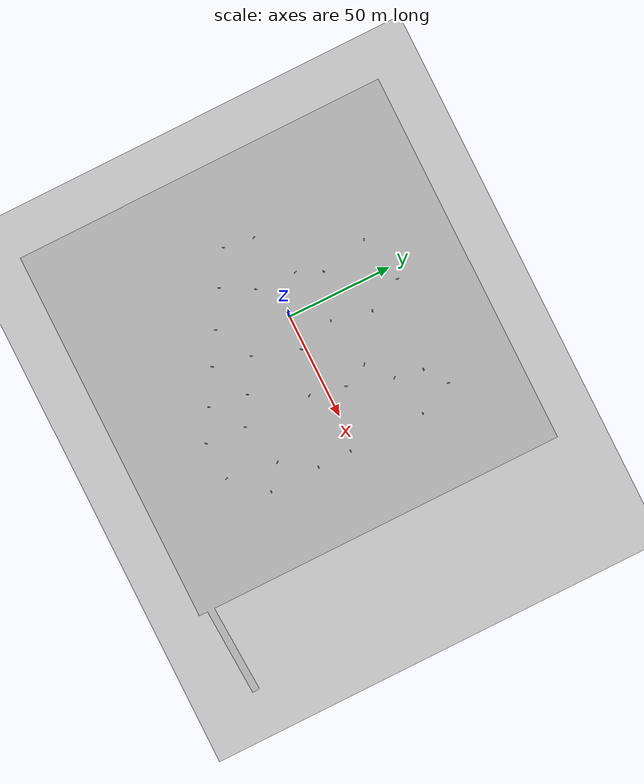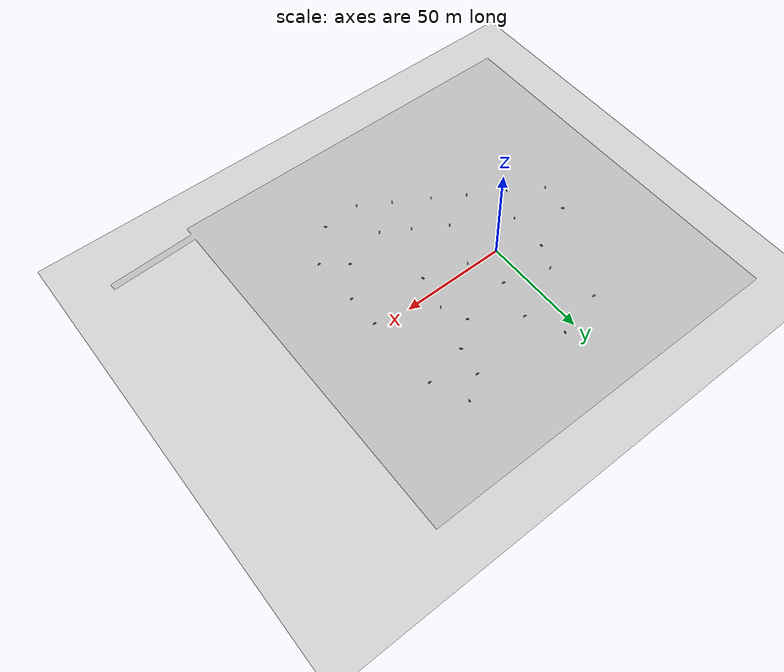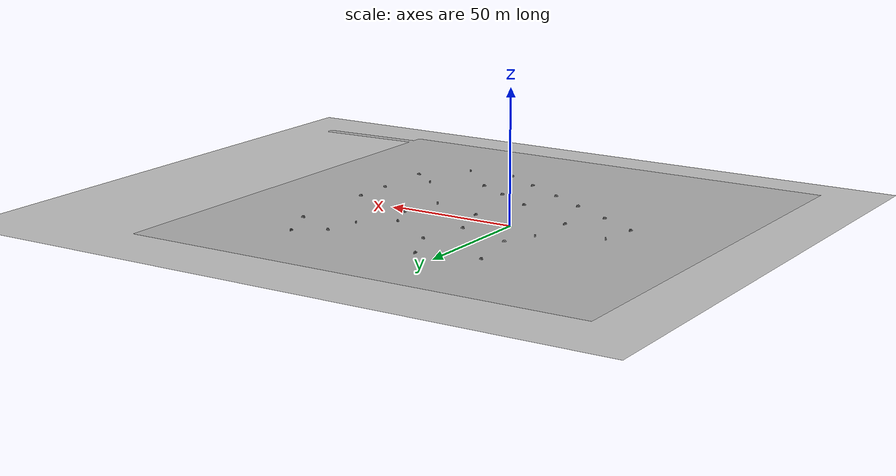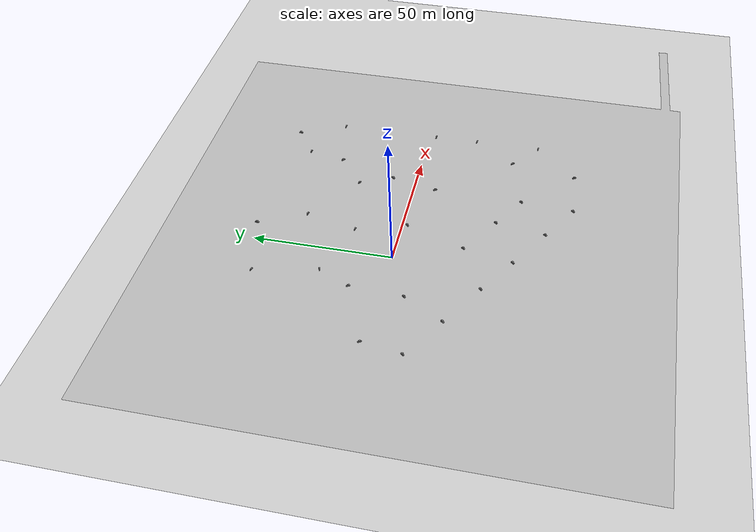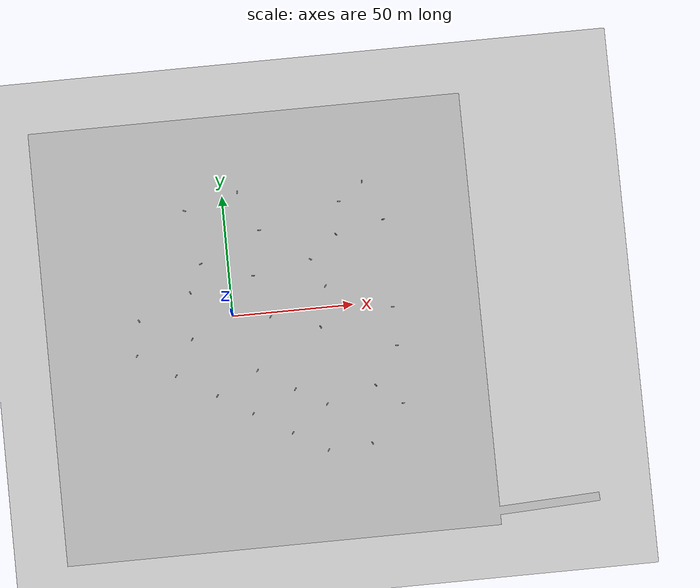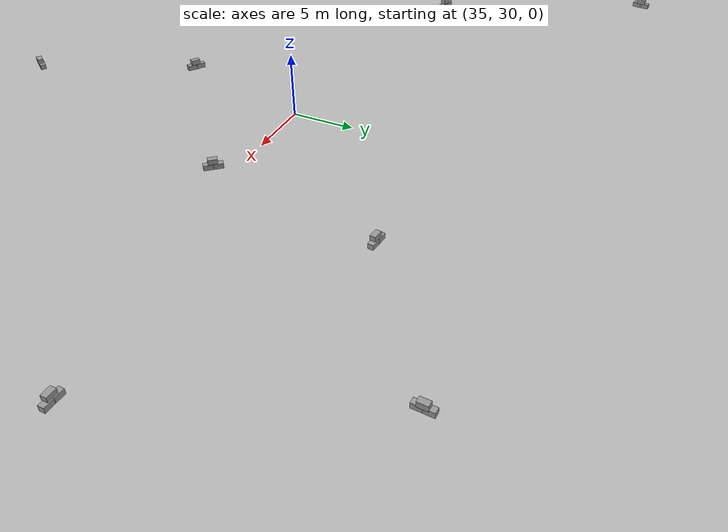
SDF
<sdf version="1.7">
 <world name="default">
  <light name="sun" type="directional">
   <pose>0 0 10 0 -0 0</pose>
   <diffuse>0.8 0.8 0.8 1</diffuse>
   <specular>0.2 0.2 0.2 1</specular>
   <attenuation>
    <range>1000</range>
    <constant>0.9</constant>
    <linear>0.01</linear>
    <quadratic>0.001</quadratic>
   </attenuation>
   <direction>-0.5 0.1 -0.9</direction>
   <spot><inner_angle>0</inner_angle><outer_angle>0</outer_angle><falloff>0</falloff></spot>
  </light>
  <model name="ground_plane">
   <static>1</static>
   <link name="link">
    <collision name="collision">
     <geometry><plane><normal>0 0 1</normal><size>100 100</size></plane></geometry>
     <surface>
      <contact><collide_bitmask>65535</collide_bitmask></contact>
      <friction><ode><mu>100</mu><mu2>50</mu2></ode></friction>
     </surface>
    </collision>
    <visual name="visual">
     <cast_shadows>0</cast_shadows>
     <geometry><plane><normal>0 0 1</normal><size>100 100</size></plane></geometry>
     <material>
      <script><uri>file://media/materials/scripts/gazebo.material</uri><name>Gazebo/Grey</name></script>
     </material>
    </visual>
   </link>
  </model>
  <gravity>0 0 -9.8</gravity>
  <magnetic_field>6e-06 2.3e-05 -4.2e-05</magnetic_field>
  <atmosphere type="adiabatic"/>
  <physics type="ode">
   <max_step_size>0.001</max_step_size>
   <real_time_factor>1</real_time_factor>
   <real_time_update_rate>1000</real_time_update_rate>
  </physics>
  <scene><ambient>0.4 0.4 0.4 1</ambient><background>0.7 0.7 0.7 1</background><shadows>1</shadows></scene>
  <spherical_coordinates>
   <surface_model>EARTH_WGS84</surface_model>
   <latitude_deg>0</latitude_deg>
   <longitude_deg>0</longitude_deg>
   <elevation>0</elevation>
   <heading_deg>0</heading_deg>
  </spherical_coordinates>
  <model name="raceway">
   <static>1</static>
   <link name="link">
    <collision name="collision">
     <pose>0 0 0 1.5707 -0 0</pose>
     <geometry><mesh><uri>model://raceway/meshes/raceway.obj</uri></mesh></geometry>
    </collision>
    <visual name="visual">
     <pose>0 0 0 1.5707 -0 0</pose>
     <geometry><mesh><uri>model://raceway/meshes/raceway.obj</uri></mesh></geometry>
    </visual>
    <scale>3</scale>
   </link>
   <pose>12.1426 -6.58602 1.42468 9.6e-05 -0 0</pose>
  </model>
  <model name="Add_Box">
   <link name="link">
    <inertial>
     <mass>1</mass>
     <inertia>
      <ixx>0.166667</ixx>
      <ixy>0</ixy>
      <ixz>0</ixz>
      <iyy>0.166667</iyy>
      <iyz>0</iyz>
      <izz>0.166667</izz>
     </inertia>
    </inertial>
    <kinematic>1</kinematic>
    <gravity>0</gravity>
    <visual name="visual">
     <geometry><box><size>0.686 0.406 0.381</size></box></geometry>
     <material>
      <script><name>Gazebo/Grey</name><uri>file://media/materials/scripts/gazebo.material</uri></script>
      <shader type="pixel"><normal_map>__default__</normal_map></shader>
      <ambient>0.3 0.3 0.3 1</ambient>
      <diffuse>0.7 0.7 0.7 1</diffuse>
      <specular>0.01 0.01 0.01 1</specular>
      <emissive>0 0 0 1</emissive>
     </material>
    </visual>
    <collision name="collision">
     <geometry><box><size>1 1 1</size></box></geometry>
     <surface>
      <friction>
       <ode><mu>1</mu><mu2>1</mu2><fdir1>0 0 0</fdir1><slip1>0</slip1><slip2>0</slip2></ode>
       <torsional>
        <coefficient>1</coefficient>
        <patch_radius>0</patch_radius>
        <surface_radius>0</surface_radius>
        <use_patch_radius>1</use_patch_radius>
        <ode><slip>0</slip></ode>
       </torsional>
      </friction>
      <bounce><restitution_coefficient>0</restitution_coefficient><threshold>1e+06</threshold></bounce>
      <contact>
       <collide_without_contact>0</collide_without_contact>
       <collide_without_contact_bitmask>1</collide_without_contact_bitmask>
       <collide_bitmask>1</collide_bitmask>
       <ode>
        <soft_cfm>0</soft_cfm>
        <soft_erp>0.2</soft_erp>
        <kp>1e+13</kp>
        <kd>1</kd>
        <max_vel>0.01</max_vel>
        <min_depth>0</min_depth>
       </ode>
       <bullet>
        <split_impulse>1</split_impulse>
        <split_impulse_penetration_threshold>-0.01</split_impulse_penetration_threshold>
        <soft_cfm>0</soft_cfm>
        <soft_erp>0.2</soft_erp>
        <kp>1e+13</kp>
        <kd>1</kd>
       </bullet>
      </contact>
     </surface>
    </collision>
   </link>
   <link name="link_clone">
    <inertial>
     <mass>1</mass>
     <inertia>
      <ixx>0.166667</ixx>
      <ixy>0</ixy>
      <ixz>0</ixz>
      <iyy>0.166667</iyy>
      <iyz>0</iyz>
      <izz>0.166667</izz>
     </inertia>
    </inertial>
    <pose>-0.343354 -0.063316 0.354303 1e-05 -0 0</pose>
    <gravity>0</gravity>
    <visual name="visual">
     <geometry><box><size>0.686 0.406 0.381</size></box></geometry>
     <material>
      <script><name>Gazebo/Grey</name><uri>file://media/materials/scripts/gazebo.material</uri></script>
      <shader type="pixel"><normal_map>__default__</normal_map></shader>
      <ambient>0.3 0.3 0.3 1</ambient>
      <diffuse>0.7 0.7 0.7 1</diffuse>
      <specular>0.01 0.01 0.01 1</specular>
      <emissive>0 0 0 1</emissive>
     </material>
    </visual>
    <collision name="collision">
     <geometry><box><size>1 1 1</size></box></geometry>
     <surface>
      <friction>
       <ode><mu>1</mu><mu2>1</mu2><fdir1>0 0 0</fdir1><slip1>0</slip1><slip2>0</slip2></ode>
       <torsional>
        <coefficient>1</coefficient>
        <patch_radius>0</patch_radius>
        <surface_radius>0</surface_radius>
        <use_patch_radius>1</use_patch_radius>
        <ode><slip>0</slip></ode>
       </torsional>
      </friction>
      <bounce><restitution_coefficient>0</restitution_coefficient><threshold>1e+06</threshold></bounce>
      <contact>
       <collide_without_contact>0</collide_without_contact>
       <collide_without_contact_bitmask>1</collide_without_contact_bitmask>
       <collide_bitmask>1</collide_bitmask>
       <ode>
        <soft_cfm>0</soft_cfm>
        <soft_erp>0.2</soft_erp>
        <kp>1e+13</kp>
        <kd>1</kd>
        <max_vel>0.01</max_vel>
        <min_depth>0</min_depth>
       </ode>
       <bullet>
        <split_impulse>1</split_impulse>
        <split_impulse_penetration_threshold>-0.01</split_impulse_penetration_threshold>
        <soft_cfm>0</soft_cfm>
        <soft_erp>0.2</soft_erp>
        <kp>1e+13</kp>
        <kd>1</kd>
       </bullet>
      </contact>
     </surface>
    </collision>
   </link>
   <link name="link_clone_clone">
    <inertial>
     <mass>1</mass>
     <inertia>
      <ixx>0.166667</ixx>
      <ixy>0</ixy>
      <ixz>0</ixz>
      <iyy>0.166667</iyy>
      <iyz>0</iyz>
      <izz>0.166667</izz>
     </inertia>
    </inertial>
    <pose>-0.690786 -0.000183 -1e-05 2e-05 -0 0</pose>
    <gravity>0</gravity>
    <visual name="visual">
     <geometry><box><size>0.686 0.406 0.381</size></box></geometry>
     <material>
      <script><name>Gazebo/Grey</name><uri>file://media/materials/scripts/gazebo.material</uri></script>
      <shader type="pixel"><normal_map>__default__</normal_map></shader>
      <ambient>0.3 0.3 0.3 1</ambient>
      <diffuse>0.7 0.7 0.7 1</diffuse>
      <specular>0.01 0.01 0.01 1</specular>
      <emissive>0 0 0 1</emissive>
     </material>
    </visual>
    <collision name="collision">
     <geometry><box><size>1 1 1</size></box></geometry>
     <surface>
      <friction>
       <ode><mu>1</mu><mu2>1</mu2><fdir1>0 0 0</fdir1><slip1>0</slip1><slip2>0</slip2></ode>
       <torsional>
        <coefficient>1</coefficient>
        <patch_radius>0</patch_radius>
        <surface_radius>0</surface_radius>
        <use_patch_radius>1</use_patch_radius>
        <ode><slip>0</slip></ode>
       </torsional>
      </friction>
      <bounce><restitution_coefficient>0</restitution_coefficient><threshold>1e+06</threshold></bounce>
      <contact>
       <collide_without_contact>0</collide_without_contact>
       <collide_without_contact_bitmask>1</collide_without_contact_bitmask>
       <collide_bitmask>1</collide_bitmask>
       <ode>
        <soft_cfm>0</soft_cfm>
        <soft_erp>0.2</soft_erp>
        <kp>1e+13</kp>
        <kd>1</kd>
        <max_vel>0.01</max_vel>
        <min_depth>0</min_depth>
       </ode>
       <bullet>
        <split_impulse>1</split_impulse>
        <split_impulse_penetration_threshold>-0.01</split_impulse_penetration_threshold>
        <soft_cfm>0</soft_cfm>
        <soft_erp>0.2</soft_erp>
        <kp>1e+13</kp>
        <kd>1</kd>
       </bullet>
      </contact>
     </surface>
    </collision>
   </link>
   <static>0</static>
   <pose>8.10311 -23.2047 1.61518 0 1e-06 1.03198</pose>
  </model>
  <model name="Add_Box_clone_clone">
   <link name="link">
    <inertial>
     <mass>1</mass>
     <inertia>
      <ixx>0.166667</ixx>
      <ixy>0</ixy>
      <ixz>0</ixz>
      <iyy>0.166667</iyy>
      <iyz>0</iyz>
      <izz>0.166667</izz>
     </inertia>
    </inertial>
    <kinematic>1</kinematic>
    <gravity>0</gravity>
    <visual name="visual">
     <geometry><box><size>0.686 0.406 0.381</size></box></geometry>
     <material>
      <script><name>Gazebo/Grey</name><uri>file://media/materials/scripts/gazebo.material</uri></script>
      <shader type="pixel"><normal_map>__default__</normal_map></shader>
      <ambient>0.3 0.3 0.3 1</ambient>
      <diffuse>0.7 0.7 0.7 1</diffuse>
      <specular>0.01 0.01 0.01 1</specular>
      <emissive>0 0 0 1</emissive>
     </material>
    </visual>
    <collision name="collision">
     <geometry><box><size>1 1 1</size></box></geometry>
     <surface>
      <friction>
       <ode><mu>1</mu><mu2>1</mu2><fdir1>0 0 0</fdir1><slip1>0</slip1><slip2>0</slip2></ode>
       <torsional>
        <coefficient>1</coefficient>
        <patch_radius>0</patch_radius>
        <surface_radius>0</surface_radius>
        <use_patch_radius>1</use_patch_radius>
        <ode><slip>0</slip></ode>
       </torsional>
      </friction>
      <bounce><restitution_coefficient>0</restitution_coefficient><threshold>1e+06</threshold></bounce>
      <contact>
       <collide_without_contact>0</collide_without_contact>
       <collide_without_contact_bitmask>1</collide_without_contact_bitmask>
       <collide_bitmask>1</collide_bitmask>
       <ode>
        <soft_cfm>0</soft_cfm>
        <soft_erp>0.2</soft_erp>
        <kp>1e+13</kp>
        <kd>1</kd>
        <max_vel>0.01</max_vel>
        <min_depth>0</min_depth>
       </ode>
       <bullet>
        <split_impulse>1</split_impulse>
        <split_impulse_penetration_threshold>-0.01</split_impulse_penetration_threshold>
        <soft_cfm>0</soft_cfm>
        <soft_erp>0.2</soft_erp>
        <kp>1e+13</kp>
        <kd>1</kd>
       </bullet>
      </contact>
     </surface>
    </collision>
   </link>
   <link name="link_clone">
    <inertial>
     <mass>1</mass>
     <inertia>
      <ixx>0.166667</ixx>
      <ixy>0</ixy>
      <ixz>0</ixz>
      <iyy>0.166667</iyy>
      <iyz>0</iyz>
      <izz>0.166667</izz>
     </inertia>
    </inertial>
    <pose>-0.343354 -0.063316 0.354303 1e-05 -0 0</pose>
    <gravity>0</gravity>
    <visual name="visual">
     <geometry><box><size>0.686 0.406 0.381</size></box></geometry>
     <material>
      <script><name>Gazebo/Grey</name><uri>file://media/materials/scripts/gazebo.material</uri></script>
      <shader type="pixel"><normal_map>__default__</normal_map></shader>
      <ambient>0.3 0.3 0.3 1</ambient>
      <diffuse>0.7 0.7 0.7 1</diffuse>
      <specular>0.01 0.01 0.01 1</specular>
      <emissive>0 0 0 1</emissive>
     </material>
    </visual>
    <collision name="collision">
     <geometry><box><size>1 1 1</size></box></geometry>
     <surface>
      <friction>
       <ode><mu>1</mu><mu2>1</mu2><fdir1>0 0 0</fdir1><slip1>0</slip1><slip2>0</slip2></ode>
       <torsional>
        <coefficient>1</coefficient>
        <patch_radius>0</patch_radius>
        <surface_radius>0</surface_radius>
        <use_patch_radius>1</use_patch_radius>
        <ode><slip>0</slip></ode>
       </torsional>
      </friction>
      <bounce><restitution_coefficient>0</restitution_coefficient><threshold>1e+06</threshold></bounce>
      <contact>
       <collide_without_contact>0</collide_without_contact>
       <collide_without_contact_bitmask>1</collide_without_contact_bitmask>
       <collide_bitmask>1</collide_bitmask>
       <ode>
        <soft_cfm>0</soft_cfm>
        <soft_erp>0.2</soft_erp>
        <kp>1e+13</kp>
        <kd>1</kd>
        <max_vel>0.01</max_vel>
        <min_depth>0</min_depth>
       </ode>
       <bullet>
        <split_impulse>1</split_impulse>
        <split_impulse_penetration_threshold>-0.01</split_impulse_penetration_threshold>
        <soft_cfm>0</soft_cfm>
        <soft_erp>0.2</soft_erp>
        <kp>1e+13</kp>
        <kd>1</kd>
       </bullet>
      </contact>
     </surface>
    </collision>
   </link>
   <link name="link_clone_clone">
    <inertial>
     <mass>1</mass>
     <inertia>
      <ixx>0.166667</ixx>
      <ixy>0</ixy>
      <ixz>0</ixz>
      <iyy>0.166667</iyy>
      <iyz>0</iyz>
      <izz>0.166667</izz>
     </inertia>
    </inertial>
    <pose>-0.690786 -0.000183 -1e-05 2e-05 -0 0</pose>
    <gravity>0</gravity>
    <visual name="visual">
     <geometry><box><size>0.686 0.406 0.381</size></box></geometry>
     <material>
      <script><name>Gazebo/Grey</name><uri>file://media/materials/scripts/gazebo.material</uri></script>
      <shader type="pixel"><normal_map>__default__</normal_map></shader>
      <ambient>0.3 0.3 0.3 1</ambient>
      <diffuse>0.7 0.7 0.7 1</diffuse>
      <specular>0.01 0.01 0.01 1</specular>
      <emissive>0 0 0 1</emissive>
     </material>
    </visual>
    <collision name="collision">
     <geometry><box><size>1 1 1</size></box></geometry>
     <surface>
      <friction>
       <ode><mu>1</mu><mu2>1</mu2><fdir1>0 0 0</fdir1><slip1>0</slip1><slip2>0</slip2></ode>
       <torsional>
        <coefficient>1</coefficient>
        <patch_radius>0</patch_radius>
        <surface_radius>0</surface_radius>
        <use_patch_radius>1</use_patch_radius>
        <ode><slip>0</slip></ode>
       </torsional>
      </friction>
      <bounce><restitution_coefficient>0</restitution_coefficient><threshold>1e+06</threshold></bounce>
      <contact>
       <collide_without_contact>0</collide_without_contact>
       <collide_without_contact_bitmask>1</collide_without_contact_bitmask>
       <collide_bitmask>1</collide_bitmask>
       <ode>
        <soft_cfm>0</soft_cfm>
        <soft_erp>0.2</soft_erp>
        <kp>1e+13</kp>
        <kd>1</kd>
        <max_vel>0.01</max_vel>
        <min_depth>0</min_depth>
       </ode>
       <bullet>
        <split_impulse>1</split_impulse>
        <split_impulse_penetration_threshold>-0.01</split_impulse_penetration_threshold>
        <soft_cfm>0</soft_cfm>
        <soft_erp>0.2</soft_erp>
        <kp>1e+13</kp>
        <kd>1</kd>
       </bullet>
      </contact>
     </surface>
    </collision>
   </link>
   <static>0</static>
   <pose>22.9483 -32.3937 1.61518 0 -0 0.950497</pose>
  </model>
  <model name="Add_Box_clone_clone_1">
   <link name="link">
    <inertial>
     <mass>1</mass>
     <inertia>
      <ixx>0.166667</ixx>
      <ixy>0</ixy>
      <ixz>0</ixz>
      <iyy>0.166667</iyy>
      <iyz>0</iyz>
      <izz>0.166667</izz>
     </inertia>
    </inertial>
    <kinematic>1</kinematic>
    <gravity>0</gravity>
    <visual name="visual">
     <geometry><box><size>0.686 0.406 0.381</size></box></geometry>
     <material>
      <script><name>Gazebo/Grey</name><uri>file://media/materials/scripts/gazebo.material</uri></script>
      <shader type="pixel"><normal_map>__default__</normal_map></shader>
      <ambient>0.3 0.3 0.3 1</ambient>
      <diffuse>0.7 0.7 0.7 1</diffuse>
      <specular>0.01 0.01 0.01 1</specular>
      <emissive>0 0 0 1</emissive>
     </material>
    </visual>
    <collision name="collision">
     <geometry><box><size>1 1 1</size></box></geometry>
     <surface>
      <friction>
       <ode><mu>1</mu><mu2>1</mu2><fdir1>0 0 0</fdir1><slip1>0</slip1><slip2>0</slip2></ode>
       <torsional>
        <coefficient>1</coefficient>
        <patch_radius>0</patch_radius>
        <surface_radius>0</surface_radius>
        <use_patch_radius>1</use_patch_radius>
        <ode><slip>0</slip></ode>
       </torsional>
      </friction>
      <bounce><restitution_coefficient>0</restitution_coefficient><threshold>1e+06</threshold></bounce>
      <contact>
       <collide_without_contact>0</collide_without_contact>
       <collide_without_contact_bitmask>1</collide_without_contact_bitmask>
       <collide_bitmask>1</collide_bitmask>
       <ode>
        <soft_cfm>0</soft_cfm>
        <soft_erp>0.2</soft_erp>
        <kp>1e+13</kp>
        <kd>1</kd>
        <max_vel>0.01</max_vel>
        <min_depth>0</min_depth>
       </ode>
       <bullet>
        <split_impulse>1</split_impulse>
        <split_impulse_penetration_threshold>-0.01</split_impulse_penetration_threshold>
        <soft_cfm>0</soft_cfm>
        <soft_erp>0.2</soft_erp>
        <kp>1e+13</kp>
        <kd>1</kd>
       </bullet>
      </contact>
     </surface>
    </collision>
   </link>
   <link name="link_clone">
    <inertial>
     <mass>1</mass>
     <inertia>
      <ixx>0.166667</ixx>
      <ixy>0</ixy>
      <ixz>0</ixz>
      <iyy>0.166667</iyy>
      <iyz>0</iyz>
      <izz>0.166667</izz>
     </inertia>
    </inertial>
    <pose>-0.343354 -0.063316 0.354303 1e-05 -0 0</pose>
    <gravity>0</gravity>
    <visual name="visual">
     <geometry><box><size>0.686 0.406 0.381</size></box></geometry>
     <material>
      <script><name>Gazebo/Grey</name><uri>file://media/materials/scripts/gazebo.material</uri></script>
      <shader type="pixel"><normal_map>__default__</normal_map></shader>
      <ambient>0.3 0.3 0.3 1</ambient>
      <diffuse>0.7 0.7 0.7 1</diffuse>
      <specular>0.01 0.01 0.01 1</specular>
      <emissive>0 0 0 1</emissive>
     </material>
    </visual>
    <collision name="collision">
     <geometry><box><size>1 1 1</size></box></geometry>
     <surface>
      <friction>
       <ode><mu>1</mu><mu2>1</mu2><fdir1>0 0 0</fdir1><slip1>0</slip1><slip2>0</slip2></ode>
       <torsional>
        <coefficient>1</coefficient>
        <patch_radius>0</patch_radius>
        <surface_radius>0</surface_radius>
        <use_patch_radius>1</use_patch_radius>
        <ode><slip>0</slip></ode>
       </torsional>
      </friction>
      <bounce><restitution_coefficient>0</restitution_coefficient><threshold>1e+06</threshold></bounce>
      <contact>
       <collide_without_contact>0</collide_without_contact>
       <collide_without_contact_bitmask>1</collide_without_contact_bitmask>
       <collide_bitmask>1</collide_bitmask>
       <ode>
        <soft_cfm>0</soft_cfm>
        <soft_erp>0.2</soft_erp>
        <kp>1e+13</kp>
        <kd>1</kd>
        <max_vel>0.01</max_vel>
        <min_depth>0</min_depth>
       </ode>
       <bullet>
        <split_impulse>1</split_impulse>
        <split_impulse_penetration_threshold>-0.01</split_impulse_penetration_threshold>
        <soft_cfm>0</soft_cfm>
        <soft_erp>0.2</soft_erp>
        <kp>1e+13</kp>
        <kd>1</kd>
       </bullet>
      </contact>
     </surface>
    </collision>
   </link>
   <link name="link_clone_clone">
    <inertial>
     <mass>1</mass>
     <inertia>
      <ixx>0.166667</ixx>
      <ixy>0</ixy>
      <ixz>0</ixz>
      <iyy>0.166667</iyy>
      <iyz>0</iyz>
      <izz>0.166667</izz>
     </inertia>
    </inertial>
    <pose>-0.690786 -0.000183 -1e-05 2e-05 -0 0</pose>
    <gravity>0</gravity>
    <visual name="visual">
     <geometry><box><size>0.686 0.406 0.381</size></box></geometry>
     <material>
      <script><name>Gazebo/Grey</name><uri>file://media/materials/scripts/gazebo.material</uri></script>
      <shader type="pixel"><normal_map>__default__</normal_map></shader>
      <ambient>0.3 0.3 0.3 1</ambient>
      <diffuse>0.7 0.7 0.7 1</diffuse>
      <specular>0.01 0.01 0.01 1</specular>
      <emissive>0 0 0 1</emissive>
     </material>
    </visual>
    <collision name="collision">
     <geometry><box><size>1 1 1</size></box></geometry>
     <surface>
      <friction>
       <ode><mu>1</mu><mu2>1</mu2><fdir1>0 0 0</fdir1><slip1>0</slip1><slip2>0</slip2></ode>
       <torsional>
        <coefficient>1</coefficient>
        <patch_radius>0</patch_radius>
        <surface_radius>0</surface_radius>
        <use_patch_radius>1</use_patch_radius>
        <ode><slip>0</slip></ode>
       </torsional>
      </friction>
      <bounce><restitution_coefficient>0</restitution_coefficient><threshold>1e+06</threshold></bounce>
      <contact>
       <collide_without_contact>0</collide_without_contact>
       <collide_without_contact_bitmask>1</collide_without_contact_bitmask>
       <collide_bitmask>1</collide_bitmask>
       <ode>
        <soft_cfm>0</soft_cfm>
        <soft_erp>0.2</soft_erp>
        <kp>1e+13</kp>
        <kd>1</kd>
        <max_vel>0.01</max_vel>
        <min_depth>0</min_depth>
       </ode>
       <bullet>
        <split_impulse>1</split_impulse>
        <split_impulse_penetration_threshold>-0.01</split_impulse_penetration_threshold>
        <soft_cfm>0</soft_cfm>
        <soft_erp>0.2</soft_erp>
        <kp>1e+13</kp>
        <kd>1</kd>
       </bullet>
      </contact>
     </surface>
    </collision>
   </link>
   <static>0</static>
   <pose>35.4762 -39.8725 1.61518 0 -0 0.950497</pose>
  </model>
  <model name="Add_Box_clone_clone_3">
   <link name="link">
    <inertial>
     <mass>1</mass>
     <inertia>
      <ixx>0.166667</ixx>
      <ixy>0</ixy>
      <ixz>0</ixz>
      <iyy>0.166667</iyy>
      <iyz>0</iyz>
      <izz>0.166667</izz>
     </inertia>
    </inertial>
    <kinematic>1</kinematic>
    <gravity>0</gravity>
    <visual name="visual">
     <geometry><box><size>0.686 0.406 0.381</size></box></geometry>
     <material>
      <script><name>Gazebo/Grey</name><uri>file://media/materials/scripts/gazebo.material</uri></script>
      <shader type="pixel"><normal_map>__default__</normal_map></shader>
      <ambient>0.3 0.3 0.3 1</ambient>
      <diffuse>0.7 0.7 0.7 1</diffuse>
      <specular>0.01 0.01 0.01 1</specular>
      <emissive>0 0 0 1</emissive>
     </material>
    </visual>
    <collision name="collision">
     <geometry><box><size>1 1 1</size></box></geometry>
     <surface>
      <friction>
       <ode><mu>1</mu><mu2>1</mu2><fdir1>0 0 0</fdir1><slip1>0</slip1><slip2>0</slip2></ode>
       <torsional>
        <coefficient>1</coefficient>
        <patch_radius>0</patch_radius>
        <surface_radius>0</surface_radius>
        <use_patch_radius>1</use_patch_radius>
        <ode><slip>0</slip></ode>
       </torsional>
      </friction>
      <bounce><restitution_coefficient>0</restitution_coefficient><threshold>1e+06</threshold></bounce>
      <contact>
       <collide_without_contact>0</collide_without_contact>
       <collide_without_contact_bitmask>1</collide_without_contact_bitmask>
       <collide_bitmask>1</collide_bitmask>
       <ode>
        <soft_cfm>0</soft_cfm>
        <soft_erp>0.2</soft_erp>
        <kp>1e+13</kp>
        <kd>1</kd>
        <max_vel>0.01</max_vel>
        <min_depth>0</min_depth>
       </ode>
       <bullet>
        <split_impulse>1</split_impulse>
        <split_impulse_penetration_threshold>-0.01</split_impulse_penetration_threshold>
        <soft_cfm>0</soft_cfm>
        <soft_erp>0.2</soft_erp>
        <kp>1e+13</kp>
        <kd>1</kd>
       </bullet>
      </contact>
     </surface>
    </collision>
   </link>
   <link name="link_clone">
    <inertial>
     <mass>1</mass>
     <inertia>
      <ixx>0.166667</ixx>
      <ixy>0</ixy>
      <ixz>0</ixz>
      <iyy>0.166667</iyy>
      <iyz>0</iyz>
      <izz>0.166667</izz>
     </inertia>
    </inertial>
    <pose>-0.343354 -0.063316 0.354303 1e-05 -0 0</pose>
    <gravity>0</gravity>
    <visual name="visual">
     <geometry><box><size>0.686 0.406 0.381</size></box></geometry>
     <material>
      <script><name>Gazebo/Grey</name><uri>file://media/materials/scripts/gazebo.material</uri></script>
      <shader type="pixel"><normal_map>__default__</normal_map></shader>
      <ambient>0.3 0.3 0.3 1</ambient>
      <diffuse>0.7 0.7 0.7 1</diffuse>
      <specular>0.01 0.01 0.01 1</specular>
      <emissive>0 0 0 1</emissive>
     </material>
    </visual>
    <collision name="collision">
     <geometry><box><size>1 1 1</size></box></geometry>
     <surface>
      <friction>
       <ode><mu>1</mu><mu2>1</mu2><fdir1>0 0 0</fdir1><slip1>0</slip1><slip2>0</slip2></ode>
       <torsional>
        <coefficient>1</coefficient>
        <patch_radius>0</patch_radius>
        <surface_radius>0</surface_radius>
        <use_patch_radius>1</use_patch_radius>
        <ode><slip>0</slip></ode>
       </torsional>
      </friction>
      <bounce><restitution_coefficient>0</restitution_coefficient><threshold>1e+06</threshold></bounce>
      <contact>
       <collide_without_contact>0</collide_without_contact>
       <collide_without_contact_bitmask>1</collide_without_contact_bitmask>
       <collide_bitmask>1</collide_bitmask>
       <ode>
        <soft_cfm>0</soft_cfm>
        <soft_erp>0.2</soft_erp>
        <kp>1e+13</kp>
        <kd>1</kd>
        <max_vel>0.01</max_vel>
        <min_depth>0</min_depth>
       </ode>
       <bullet>
        <split_impulse>1</split_impulse>
        <split_impulse_penetration_threshold>-0.01</split_impulse_penetration_threshold>
        <soft_cfm>0</soft_cfm>
        <soft_erp>0.2</soft_erp>
        <kp>1e+13</kp>
        <kd>1</kd>
       </bullet>
      </contact>
     </surface>
    </collision>
   </link>
   <link name="link_clone_clone">
    <inertial>
     <mass>1</mass>
     <inertia>
      <ixx>0.166667</ixx>
      <ixy>0</ixy>
      <ixz>0</ixz>
      <iyy>0.166667</iyy>
      <iyz>0</iyz>
      <izz>0.166667</izz>
     </inertia>
    </inertial>
    <pose>-0.690786 -0.000183 -1e-05 2e-05 -0 0</pose>
    <gravity>0</gravity>
    <visual name="visual">
     <geometry><box><size>0.686 0.406 0.381</size></box></geometry>
     <material>
      <script><name>Gazebo/Grey</name><uri>file://media/materials/scripts/gazebo.material</uri></script>
      <shader type="pixel"><normal_map>__default__</normal_map></shader>
      <ambient>0.3 0.3 0.3 1</ambient>
      <diffuse>0.7 0.7 0.7 1</diffuse>
      <specular>0.01 0.01 0.01 1</specular>
      <emissive>0 0 0 1</emissive>
     </material>
    </visual>
    <collision name="collision">
     <geometry><box><size>1 1 1</size></box></geometry>
     <surface>
      <friction>
       <ode><mu>1</mu><mu2>1</mu2><fdir1>0 0 0</fdir1><slip1>0</slip1><slip2>0</slip2></ode>
       <torsional>
        <coefficient>1</coefficient>
        <patch_radius>0</patch_radius>
        <surface_radius>0</surface_radius>
        <use_patch_radius>1</use_patch_radius>
        <ode><slip>0</slip></ode>
       </torsional>
      </friction>
      <bounce><restitution_coefficient>0</restitution_coefficient><threshold>1e+06</threshold></bounce>
      <contact>
       <collide_without_contact>0</collide_without_contact>
       <collide_without_contact_bitmask>1</collide_without_contact_bitmask>
       <collide_bitmask>1</collide_bitmask>
       <ode>
        <soft_cfm>0</soft_cfm>
        <soft_erp>0.2</soft_erp>
        <kp>1e+13</kp>
        <kd>1</kd>
        <max_vel>0.01</max_vel>
        <min_depth>0</min_depth>
       </ode>
       <bullet>
        <split_impulse>1</split_impulse>
        <split_impulse_penetration_threshold>-0.01</split_impulse_penetration_threshold>
        <soft_cfm>0</soft_cfm>
        <soft_erp>0.2</soft_erp>
        <kp>1e+13</kp>
        <kd>1</kd>
       </bullet>
      </contact>
     </surface>
    </collision>
   </link>
   <static>0</static>
   <pose>-17.6299 -7.80134 1.61518 0 -0 0.950497</pose>
  </model>
  <model name="Add_Box_clone_clone_3_clone">
   <link name="link">
    <inertial>
     <mass>1</mass>
     <inertia>
      <ixx>0.166667</ixx>
      <ixy>0</ixy>
      <ixz>0</ixz>
      <iyy>0.166667</iyy>
      <iyz>0</iyz>
      <izz>0.166667</izz>
     </inertia>
    </inertial>
    <kinematic>1</kinematic>
    <gravity>0</gravity>
    <visual name="visual">
     <geometry><box><size>0.686 0.406 0.381</size></box></geometry>
     <material>
      <script><name>Gazebo/Grey</name><uri>file://media/materials/scripts/gazebo.material</uri></script>
      <shader type="pixel"><normal_map>__default__</normal_map></shader>
      <ambient>0.3 0.3 0.3 1</ambient>
      <diffuse>0.7 0.7 0.7 1</diffuse>
      <specular>0.01 0.01 0.01 1</specular>
      <emissive>0 0 0 1</emissive>
     </material>
    </visual>
    <collision name="collision">
     <geometry><box><size>1 1 1</size></box></geometry>
     <surface>
      <friction>
       <ode><mu>1</mu><mu2>1</mu2><fdir1>0 0 0</fdir1><slip1>0</slip1><slip2>0</slip2></ode>
       <torsional>
        <coefficient>1</coefficient>
        <patch_radius>0</patch_radius>
        <surface_radius>0</surface_radius>
        <use_patch_radius>1</use_patch_radius>
        <ode><slip>0</slip></ode>
       </torsional>
      </friction>
      <bounce><restitution_coefficient>0</restitution_coefficient><threshold>1e+06</threshold></bounce>
      <contact>
       <collide_without_contact>0</collide_without_contact>
       <collide_without_contact_bitmask>1</collide_without_contact_bitmask>
       <collide_bitmask>1</collide_bitmask>
       <ode>
        <soft_cfm>0</soft_cfm>
        <soft_erp>0.2</soft_erp>
        <kp>1e+13</kp>
        <kd>1</kd>
        <max_vel>0.01</max_vel>
        <min_depth>0</min_depth>
       </ode>
       <bullet>
        <split_impulse>1</split_impulse>
        <split_impulse_penetration_threshold>-0.01</split_impulse_penetration_threshold>
        <soft_cfm>0</soft_cfm>
        <soft_erp>0.2</soft_erp>
        <kp>1e+13</kp>
        <kd>1</kd>
       </bullet>
      </contact>
     </surface>
    </collision>
   </link>
   <link name="link_clone">
    <inertial>
     <mass>1</mass>
     <inertia>
      <ixx>0.166667</ixx>
      <ixy>0</ixy>
      <ixz>0</ixz>
      <iyy>0.166667</iyy>
      <iyz>0</iyz>
      <izz>0.166667</izz>
     </inertia>
    </inertial>
    <pose>-0.343354 -0.063316 0.354303 1e-05 -0 0</pose>
    <gravity>0</gravity>
    <visual name="visual">
     <geometry><box><size>0.686 0.406 0.381</size></box></geometry>
     <material>
      <script><name>Gazebo/Grey</name><uri>file://media/materials/scripts/gazebo.material</uri></script>
      <shader type="pixel"><normal_map>__default__</normal_map></shader>
      <ambient>0.3 0.3 0.3 1</ambient>
      <diffuse>0.7 0.7 0.7 1</diffuse>
      <specular>0.01 0.01 0.01 1</specular>
      <emissive>0 0 0 1</emissive>
     </material>
    </visual>
    <collision name="collision">
     <geometry><box><size>1 1 1</size></box></geometry>
     <surface>
      <friction>
       <ode><mu>1</mu><mu2>1</mu2><fdir1>0 0 0</fdir1><slip1>0</slip1><slip2>0</slip2></ode>
       <torsional>
        <coefficient>1</coefficient>
        <patch_radius>0</patch_radius>
        <surface_radius>0</surface_radius>
        <use_patch_radius>1</use_patch_radius>
        <ode><slip>0</slip></ode>
       </torsional>
      </friction>
      <bounce><restitution_coefficient>0</restitution_coefficient><threshold>1e+06</threshold></bounce>
      <contact>
       <collide_without_contact>0</collide_without_contact>
       <collide_without_contact_bitmask>1</collide_without_contact_bitmask>
       <collide_bitmask>1</collide_bitmask>
       <ode>
        <soft_cfm>0</soft_cfm>
        <soft_erp>0.2</soft_erp>
        <kp>1e+13</kp>
        <kd>1</kd>
        <max_vel>0.01</max_vel>
        <min_depth>0</min_depth>
       </ode>
       <bullet>
        <split_impulse>1</split_impulse>
        <split_impulse_penetration_threshold>-0.01</split_impulse_penetration_threshold>
        <soft_cfm>0</soft_cfm>
        <soft_erp>0.2</soft_erp>
        <kp>1e+13</kp>
        <kd>1</kd>
       </bullet>
      </contact>
     </surface>
    </collision>
   </link>
   <link name="link_clone_clone">
    <inertial>
     <mass>1</mass>
     <inertia>
      <ixx>0.166667</ixx>
      <ixy>0</ixy>
      <ixz>0</ixz>
      <iyy>0.166667</iyy>
      <iyz>0</iyz>
      <izz>0.166667</izz>
     </inertia>
    </inertial>
    <pose>-0.690786 -0.000183 -1e-05 2e-05 -0 0</pose>
    <gravity>0</gravity>
    <visual name="visual">
     <geometry><box><size>0.686 0.406 0.381</size></box></geometry>
     <material>
      <script><name>Gazebo/Grey</name><uri>file://media/materials/scripts/gazebo.material</uri></script>
      <shader type="pixel"><normal_map>__default__</normal_map></shader>
      <ambient>0.3 0.3 0.3 1</ambient>
      <diffuse>0.7 0.7 0.7 1</diffuse>
      <specular>0.01 0.01 0.01 1</specular>
      <emissive>0 0 0 1</emissive>
     </material>
    </visual>
    <collision name="collision">
     <geometry><box><size>1 1 1</size></box></geometry>
     <surface>
      <friction>
       <ode><mu>1</mu><mu2>1</mu2><fdir1>0 0 0</fdir1><slip1>0</slip1><slip2>0</slip2></ode>
       <torsional>
        <coefficient>1</coefficient>
        <patch_radius>0</patch_radius>
        <surface_radius>0</surface_radius>
        <use_patch_radius>1</use_patch_radius>
        <ode><slip>0</slip></ode>
       </torsional>
      </friction>
      <bounce><restitution_coefficient>0</restitution_coefficient><threshold>1e+06</threshold></bounce>
      <contact>
       <collide_without_contact>0</collide_without_contact>
       <collide_without_contact_bitmask>1</collide_without_contact_bitmask>
       <collide_bitmask>1</collide_bitmask>
       <ode>
        <soft_cfm>0</soft_cfm>
        <soft_erp>0.2</soft_erp>
        <kp>1e+13</kp>
        <kd>1</kd>
        <max_vel>0.01</max_vel>
        <min_depth>0</min_depth>
       </ode>
       <bullet>
        <split_impulse>1</split_impulse>
        <split_impulse_penetration_threshold>-0.01</split_impulse_penetration_threshold>
        <soft_cfm>0</soft_cfm>
        <soft_erp>0.2</soft_erp>
        <kp>1e+13</kp>
        <kd>1</kd>
       </bullet>
      </contact>
     </surface>
    </collision>
   </link>
   <static>0</static>
   <pose>-16.9502 11.4681 1.61518 0 -0 1.97663</pose>
  </model>
  <model name="Add_Box_clone_clone_3_clone_0">
   <link name="link">
    <inertial>
     <mass>1</mass>
     <inertia>
      <ixx>0.166667</ixx>
      <ixy>0</ixy>
      <ixz>0</ixz>
      <iyy>0.166667</iyy>
      <iyz>0</iyz>
      <izz>0.166667</izz>
     </inertia>
    </inertial>
    <kinematic>1</kinematic>
    <gravity>0</gravity>
    <visual name="visual">
     <geometry><box><size>0.686 0.406 0.381</size></box></geometry>
     <material>
      <script><name>Gazebo/Grey</name><uri>file://media/materials/scripts/gazebo.material</uri></script>
      <shader type="pixel"><normal_map>__default__</normal_map></shader>
      <ambient>0.3 0.3 0.3 1</ambient>
      <diffuse>0.7 0.7 0.7 1</diffuse>
      <specular>0.01 0.01 0.01 1</specular>
      <emissive>0 0 0 1</emissive>
     </material>
    </visual>
    <collision name="collision">
     <geometry><box><size>1 1 1</size></box></geometry>
     <surface>
      <friction>
       <ode><mu>1</mu><mu2>1</mu2><fdir1>0 0 0</fdir1><slip1>0</slip1><slip2>0</slip2></ode>
       <torsional>
        <coefficient>1</coefficient>
        <patch_radius>0</patch_radius>
        <surface_radius>0</surface_radius>
        <use_patch_radius>1</use_patch_radius>
        <ode><slip>0</slip></ode>
       </torsional>
      </friction>
      <bounce><restitution_coefficient>0</restitution_coefficient><threshold>1e+06</threshold></bounce>
      <contact>
       <collide_without_contact>0</collide_without_contact>
       <collide_without_contact_bitmask>1</collide_without_contact_bitmask>
       <collide_bitmask>1</collide_bitmask>
       <ode>
        <soft_cfm>0</soft_cfm>
        <soft_erp>0.2</soft_erp>
        <kp>1e+13</kp>
        <kd>1</kd>
        <max_vel>0.01</max_vel>
        <min_depth>0</min_depth>
       </ode>
       <bullet>
        <split_impulse>1</split_impulse>
        <split_impulse_penetration_threshold>-0.01</split_impulse_penetration_threshold>
        <soft_cfm>0</soft_cfm>
        <soft_erp>0.2</soft_erp>
        <kp>1e+13</kp>
        <kd>1</kd>
       </bullet>
      </contact>
     </surface>
    </collision>
   </link>
   <link name="link_clone">
    <inertial>
     <mass>1</mass>
     <inertia>
      <ixx>0.166667</ixx>
      <ixy>0</ixy>
      <ixz>0</ixz>
      <iyy>0.166667</iyy>
      <iyz>0</iyz>
      <izz>0.166667</izz>
     </inertia>
    </inertial>
    <pose>-0.343354 -0.063316 0.354303 1e-05 -0 0</pose>
    <gravity>0</gravity>
    <visual name="visual">
     <geometry><box><size>0.686 0.406 0.381</size></box></geometry>
     <material>
      <script><name>Gazebo/Grey</name><uri>file://media/materials/scripts/gazebo.material</uri></script>
      <shader type="pixel"><normal_map>__default__</normal_map></shader>
      <ambient>0.3 0.3 0.3 1</ambient>
      <diffuse>0.7 0.7 0.7 1</diffuse>
      <specular>0.01 0.01 0.01 1</specular>
      <emissive>0 0 0 1</emissive>
     </material>
    </visual>
    <collision name="collision">
     <geometry><box><size>1 1 1</size></box></geometry>
     <surface>
      <friction>
       <ode><mu>1</mu><mu2>1</mu2><fdir1>0 0 0</fdir1><slip1>0</slip1><slip2>0</slip2></ode>
       <torsional>
        <coefficient>1</coefficient>
        <patch_radius>0</patch_radius>
        <surface_radius>0</surface_radius>
        <use_patch_radius>1</use_patch_radius>
        <ode><slip>0</slip></ode>
       </torsional>
      </friction>
      <bounce><restitution_coefficient>0</restitution_coefficient><threshold>1e+06</threshold></bounce>
      <contact>
       <collide_without_contact>0</collide_without_contact>
       <collide_without_contact_bitmask>1</collide_without_contact_bitmask>
       <collide_bitmask>1</collide_bitmask>
       <ode>
        <soft_cfm>0</soft_cfm>
        <soft_erp>0.2</soft_erp>
        <kp>1e+13</kp>
        <kd>1</kd>
        <max_vel>0.01</max_vel>
        <min_depth>0</min_depth>
       </ode>
       <bullet>
        <split_impulse>1</split_impulse>
        <split_impulse_penetration_threshold>-0.01</split_impulse_penetration_threshold>
        <soft_cfm>0</soft_cfm>
        <soft_erp>0.2</soft_erp>
        <kp>1e+13</kp>
        <kd>1</kd>
       </bullet>
      </contact>
     </surface>
    </collision>
   </link>
   <link name="link_clone_clone">
    <inertial>
     <mass>1</mass>
     <inertia>
      <ixx>0.166667</ixx>
      <ixy>0</ixy>
      <ixz>0</ixz>
      <iyy>0.166667</iyy>
      <iyz>0</iyz>
      <izz>0.166667</izz>
     </inertia>
    </inertial>
    <pose>-0.690786 -0.000183 -1e-05 2e-05 -0 0</pose>
    <gravity>0</gravity>
    <visual name="visual">
     <geometry><box><size>0.686 0.406 0.381</size></box></geometry>
     <material>
      <script><name>Gazebo/Grey</name><uri>file://media/materials/scripts/gazebo.material</uri></script>
      <shader type="pixel"><normal_map>__default__</normal_map></shader>
      <ambient>0.3 0.3 0.3 1</ambient>
      <diffuse>0.7 0.7 0.7 1</diffuse>
      <specular>0.01 0.01 0.01 1</specular>
      <emissive>0 0 0 1</emissive>
     </material>
    </visual>
    <collision name="collision">
     <geometry><box><size>1 1 1</size></box></geometry>
     <surface>
      <friction>
       <ode><mu>1</mu><mu2>1</mu2><fdir1>0 0 0</fdir1><slip1>0</slip1><slip2>0</slip2></ode>
       <torsional>
        <coefficient>1</coefficient>
        <patch_radius>0</patch_radius>
        <surface_radius>0</surface_radius>
        <use_patch_radius>1</use_patch_radius>
        <ode><slip>0</slip></ode>
       </torsional>
      </friction>
      <bounce><restitution_coefficient>0</restitution_coefficient><threshold>1e+06</threshold></bounce>
      <contact>
       <collide_without_contact>0</collide_without_contact>
       <collide_without_contact_bitmask>1</collide_without_contact_bitmask>
       <collide_bitmask>1</collide_bitmask>
       <ode>
        <soft_cfm>0</soft_cfm>
        <soft_erp>0.2</soft_erp>
        <kp>1e+13</kp>
        <kd>1</kd>
        <max_vel>0.01</max_vel>
        <min_depth>0</min_depth>
       </ode>
       <bullet>
        <split_impulse>1</split_impulse>
        <split_impulse_penetration_threshold>-0.01</split_impulse_penetration_threshold>
        <soft_cfm>0</soft_cfm>
        <soft_erp>0.2</soft_erp>
        <kp>1e+13</kp>
        <kd>1</kd>
       </bullet>
      </contact>
     </surface>
    </collision>
   </link>
   <static>0</static>
   <pose>-11.0385 22.8981 1.61518 0 -0 0.438114</pose>
  </model>
  <model name="Add_Box_clone_clone_3_clone_1">
   <link name="link">
    <inertial>
     <mass>1</mass>
     <inertia>
      <ixx>0.166667</ixx>
      <ixy>0</ixy>
      <ixz>0</ixz>
      <iyy>0.166667</iyy>
      <iyz>0</iyz>
      <izz>0.166667</izz>
     </inertia>
    </inertial>
    <kinematic>1</kinematic>
    <gravity>0</gravity>
    <visual name="visual">
     <geometry><box><size>0.686 0.406 0.381</size></box></geometry>
     <material>
      <script><name>Gazebo/Grey</name><uri>file://media/materials/scripts/gazebo.material</uri></script>
      <shader type="pixel"><normal_map>__default__</normal_map></shader>
      <ambient>0.3 0.3 0.3 1</ambient>
      <diffuse>0.7 0.7 0.7 1</diffuse>
      <specular>0.01 0.01 0.01 1</specular>
      <emissive>0 0 0 1</emissive>
     </material>
    </visual>
    <collision name="collision">
     <geometry><box><size>1 1 1</size></box></geometry>
     <surface>
      <friction>
       <ode><mu>1</mu><mu2>1</mu2><fdir1>0 0 0</fdir1><slip1>0</slip1><slip2>0</slip2></ode>
       <torsional>
        <coefficient>1</coefficient>
        <patch_radius>0</patch_radius>
        <surface_radius>0</surface_radius>
        <use_patch_radius>1</use_patch_radius>
        <ode><slip>0</slip></ode>
       </torsional>
      </friction>
      <bounce><restitution_coefficient>0</restitution_coefficient><threshold>1e+06</threshold></bounce>
      <contact>
       <collide_without_contact>0</collide_without_contact>
       <collide_without_contact_bitmask>1</collide_without_contact_bitmask>
       <collide_bitmask>1</collide_bitmask>
       <ode>
        <soft_cfm>0</soft_cfm>
        <soft_erp>0.2</soft_erp>
        <kp>1e+13</kp>
        <kd>1</kd>
        <max_vel>0.01</max_vel>
        <min_depth>0</min_depth>
       </ode>
       <bullet>
        <split_impulse>1</split_impulse>
        <split_impulse_penetration_threshold>-0.01</split_impulse_penetration_threshold>
        <soft_cfm>0</soft_cfm>
        <soft_erp>0.2</soft_erp>
        <kp>1e+13</kp>
        <kd>1</kd>
       </bullet>
      </contact>
     </surface>
    </collision>
   </link>
   <link name="link_clone">
    <inertial>
     <mass>1</mass>
     <inertia>
      <ixx>0.166667</ixx>
      <ixy>0</ixy>
      <ixz>0</ixz>
      <iyy>0.166667</iyy>
      <iyz>0</iyz>
      <izz>0.166667</izz>
     </inertia>
    </inertial>
    <pose>-0.343354 -0.063316 0.354303 1e-05 -0 0</pose>
    <gravity>0</gravity>
    <visual name="visual">
     <geometry><box><size>0.686 0.406 0.381</size></box></geometry>
     <material>
      <script><name>Gazebo/Grey</name><uri>file://media/materials/scripts/gazebo.material</uri></script>
      <shader type="pixel"><normal_map>__default__</normal_map></shader>
      <ambient>0.3 0.3 0.3 1</ambient>
      <diffuse>0.7 0.7 0.7 1</diffuse>
      <specular>0.01 0.01 0.01 1</specular>
      <emissive>0 0 0 1</emissive>
     </material>
    </visual>
    <collision name="collision">
     <geometry><box><size>1 1 1</size></box></geometry>
     <surface>
      <friction>
       <ode><mu>1</mu><mu2>1</mu2><fdir1>0 0 0</fdir1><slip1>0</slip1><slip2>0</slip2></ode>
       <torsional>
        <coefficient>1</coefficient>
        <patch_radius>0</patch_radius>
        <surface_radius>0</surface_radius>
        <use_patch_radius>1</use_patch_radius>
        <ode><slip>0</slip></ode>
       </torsional>
      </friction>
      <bounce><restitution_coefficient>0</restitution_coefficient><threshold>1e+06</threshold></bounce>
      <contact>
       <collide_without_contact>0</collide_without_contact>
       <collide_without_contact_bitmask>1</collide_without_contact_bitmask>
       <collide_bitmask>1</collide_bitmask>
       <ode>
        <soft_cfm>0</soft_cfm>
        <soft_erp>0.2</soft_erp>
        <kp>1e+13</kp>
        <kd>1</kd>
        <max_vel>0.01</max_vel>
        <min_depth>0</min_depth>
       </ode>
       <bullet>
        <split_impulse>1</split_impulse>
        <split_impulse_penetration_threshold>-0.01</split_impulse_penetration_threshold>
        <soft_cfm>0</soft_cfm>
        <soft_erp>0.2</soft_erp>
        <kp>1e+13</kp>
        <kd>1</kd>
       </bullet>
      </contact>
     </surface>
    </collision>
   </link>
   <link name="link_clone_clone">
    <inertial>
     <mass>1</mass>
     <inertia>
      <ixx>0.166667</ixx>
      <ixy>0</ixy>
      <ixz>0</ixz>
      <iyy>0.166667</iyy>
      <iyz>0</iyz>
      <izz>0.166667</izz>
     </inertia>
    </inertial>
    <pose>-0.690786 -0.000183 -1e-05 2e-05 -0 0</pose>
    <gravity>0</gravity>
    <visual name="visual">
     <geometry><box><size>0.686 0.406 0.381</size></box></geometry>
     <material>
      <script><name>Gazebo/Grey</name><uri>file://media/materials/scripts/gazebo.material</uri></script>
      <shader type="pixel"><normal_map>__default__</normal_map></shader>
      <ambient>0.3 0.3 0.3 1</ambient>
      <diffuse>0.7 0.7 0.7 1</diffuse>
      <specular>0.01 0.01 0.01 1</specular>
      <emissive>0 0 0 1</emissive>
     </material>
    </visual>
    <collision name="collision">
     <geometry><box><size>1 1 1</size></box></geometry>
     <surface>
      <friction>
       <ode><mu>1</mu><mu2>1</mu2><fdir1>0 0 0</fdir1><slip1>0</slip1><slip2>0</slip2></ode>
       <torsional>
        <coefficient>1</coefficient>
        <patch_radius>0</patch_radius>
        <surface_radius>0</surface_radius>
        <use_patch_radius>1</use_patch_radius>
        <ode><slip>0</slip></ode>
       </torsional>
      </friction>
      <bounce><restitution_coefficient>0</restitution_coefficient><threshold>1e+06</threshold></bounce>
      <contact>
       <collide_without_contact>0</collide_without_contact>
       <collide_without_contact_bitmask>1</collide_without_contact_bitmask>
       <collide_bitmask>1</collide_bitmask>
       <ode>
        <soft_cfm>0</soft_cfm>
        <soft_erp>0.2</soft_erp>
        <kp>1e+13</kp>
        <kd>1</kd>
        <max_vel>0.01</max_vel>
        <min_depth>0</min_depth>
       </ode>
       <bullet>
        <split_impulse>1</split_impulse>
        <split_impulse_penetration_threshold>-0.01</split_impulse_penetration_threshold>
        <soft_cfm>0</soft_cfm>
        <soft_erp>0.2</soft_erp>
        <kp>1e+13</kp>
        <kd>1</kd>
       </bullet>
      </contact>
     </surface>
    </collision>
   </link>
   <static>0</static>
   <pose>-15.6972 45.2289 1.61518 0 0 -0.383222</pose>
  </model>
  <model name="Add_Box_clone_clone_3_clone_2">
   <link name="link">
    <inertial>
     <mass>1</mass>
     <inertia>
      <ixx>0.166667</ixx>
      <ixy>0</ixy>
      <ixz>0</ixz>
      <iyy>0.166667</iyy>
      <iyz>0</iyz>
      <izz>0.166667</izz>
     </inertia>
    </inertial>
    <kinematic>1</kinematic>
    <gravity>0</gravity>
    <visual name="visual">
     <geometry><box><size>0.686 0.406 0.381</size></box></geometry>
     <material>
      <script><name>Gazebo/Grey</name><uri>file://media/materials/scripts/gazebo.material</uri></script>
      <shader type="pixel"><normal_map>__default__</normal_map></shader>
      <ambient>0.3 0.3 0.3 1</ambient>
      <diffuse>0.7 0.7 0.7 1</diffuse>
      <specular>0.01 0.01 0.01 1</specular>
      <emissive>0 0 0 1</emissive>
     </material>
    </visual>
    <collision name="collision">
     <geometry><box><size>1 1 1</size></box></geometry>
     <surface>
      <friction>
       <ode><mu>1</mu><mu2>1</mu2><fdir1>0 0 0</fdir1><slip1>0</slip1><slip2>0</slip2></ode>
       <torsional>
        <coefficient>1</coefficient>
        <patch_radius>0</patch_radius>
        <surface_radius>0</surface_radius>
        <use_patch_radius>1</use_patch_radius>
        <ode><slip>0</slip></ode>
       </torsional>
      </friction>
      <bounce><restitution_coefficient>0</restitution_coefficient><threshold>1e+06</threshold></bounce>
      <contact>
       <collide_without_contact>0</collide_without_contact>
       <collide_without_contact_bitmask>1</collide_without_contact_bitmask>
       <collide_bitmask>1</collide_bitmask>
       <ode>
        <soft_cfm>0</soft_cfm>
        <soft_erp>0.2</soft_erp>
        <kp>1e+13</kp>
        <kd>1</kd>
        <max_vel>0.01</max_vel>
        <min_depth>0</min_depth>
       </ode>
       <bullet>
        <split_impulse>1</split_impulse>
        <split_impulse_penetration_threshold>-0.01</split_impulse_penetration_threshold>
        <soft_cfm>0</soft_cfm>
        <soft_erp>0.2</soft_erp>
        <kp>1e+13</kp>
        <kd>1</kd>
       </bullet>
      </contact>
     </surface>
    </collision>
   </link>
   <link name="link_clone">
    <inertial>
     <mass>1</mass>
     <inertia>
      <ixx>0.166667</ixx>
      <ixy>0</ixy>
      <ixz>0</ixz>
      <iyy>0.166667</iyy>
      <iyz>0</iyz>
      <izz>0.166667</izz>
     </inertia>
    </inertial>
    <pose>-0.343354 -0.063316 0.354303 1e-05 -0 0</pose>
    <gravity>0</gravity>
    <visual name="visual">
     <geometry><box><size>0.686 0.406 0.381</size></box></geometry>
     <material>
      <script><name>Gazebo/Grey</name><uri>file://media/materials/scripts/gazebo.material</uri></script>
      <shader type="pixel"><normal_map>__default__</normal_map></shader>
      <ambient>0.3 0.3 0.3 1</ambient>
      <diffuse>0.7 0.7 0.7 1</diffuse>
      <specular>0.01 0.01 0.01 1</specular>
      <emissive>0 0 0 1</emissive>
     </material>
    </visual>
    <collision name="collision">
     <geometry><box><size>1 1 1</size></box></geometry>
     <surface>
      <friction>
       <ode><mu>1</mu><mu2>1</mu2><fdir1>0 0 0</fdir1><slip1>0</slip1><slip2>0</slip2></ode>
       <torsional>
        <coefficient>1</coefficient>
        <patch_radius>0</patch_radius>
        <surface_radius>0</surface_radius>
        <use_patch_radius>1</use_patch_radius>
        <ode><slip>0</slip></ode>
       </torsional>
      </friction>
      <bounce><restitution_coefficient>0</restitution_coefficient><threshold>1e+06</threshold></bounce>
      <contact>
       <collide_without_contact>0</collide_without_contact>
       <collide_without_contact_bitmask>1</collide_without_contact_bitmask>
       <collide_bitmask>1</collide_bitmask>
       <ode>
        <soft_cfm>0</soft_cfm>
        <soft_erp>0.2</soft_erp>
        <kp>1e+13</kp>
        <kd>1</kd>
        <max_vel>0.01</max_vel>
        <min_depth>0</min_depth>
       </ode>
       <bullet>
        <split_impulse>1</split_impulse>
        <split_impulse_penetration_threshold>-0.01</split_impulse_penetration_threshold>
        <soft_cfm>0</soft_cfm>
        <soft_erp>0.2</soft_erp>
        <kp>1e+13</kp>
        <kd>1</kd>
       </bullet>
      </contact>
     </surface>
    </collision>
   </link>
   <link name="link_clone_clone">
    <inertial>
     <mass>1</mass>
     <inertia>
      <ixx>0.166667</ixx>
      <ixy>0</ixy>
      <ixz>0</ixz>
      <iyy>0.166667</iyy>
      <iyz>0</iyz>
      <izz>0.166667</izz>
     </inertia>
    </inertial>
    <pose>-0.690786 -0.000183 -1e-05 2e-05 -0 0</pose>
    <gravity>0</gravity>
    <visual name="visual">
     <geometry><box><size>0.686 0.406 0.381</size></box></geometry>
     <material>
      <script><name>Gazebo/Grey</name><uri>file://media/materials/scripts/gazebo.material</uri></script>
      <shader type="pixel"><normal_map>__default__</normal_map></shader>
      <ambient>0.3 0.3 0.3 1</ambient>
      <diffuse>0.7 0.7 0.7 1</diffuse>
      <specular>0.01 0.01 0.01 1</specular>
      <emissive>0 0 0 1</emissive>
     </material>
    </visual>
    <collision name="collision">
     <geometry><box><size>1 1 1</size></box></geometry>
     <surface>
      <friction>
       <ode><mu>1</mu><mu2>1</mu2><fdir1>0 0 0</fdir1><slip1>0</slip1><slip2>0</slip2></ode>
       <torsional>
        <coefficient>1</coefficient>
        <patch_radius>0</patch_radius>
        <surface_radius>0</surface_radius>
        <use_patch_radius>1</use_patch_radius>
        <ode><slip>0</slip></ode>
       </torsional>
      </friction>
      <bounce><restitution_coefficient>0</restitution_coefficient><threshold>1e+06</threshold></bounce>
      <contact>
       <collide_without_contact>0</collide_without_contact>
       <collide_without_contact_bitmask>1</collide_without_contact_bitmask>
       <collide_bitmask>1</collide_bitmask>
       <ode>
        <soft_cfm>0</soft_cfm>
        <soft_erp>0.2</soft_erp>
        <kp>1e+13</kp>
        <kd>1</kd>
        <max_vel>0.01</max_vel>
        <min_depth>0</min_depth>
       </ode>
       <bullet>
        <split_impulse>1</split_impulse>
        <split_impulse_penetration_threshold>-0.01</split_impulse_penetration_threshold>
        <soft_cfm>0</soft_cfm>
        <soft_erp>0.2</soft_erp>
        <kp>1e+13</kp>
        <kd>1</kd>
       </bullet>
      </contact>
     </surface>
    </collision>
   </link>
   <static>0</static>
   <pose>6.44279 51.303 1.61518 0 -0 1.4402</pose>
  </model>
  <model name="Add_Box_clone_clone_3_clone_3">
   <link name="link">
    <inertial>
     <mass>1</mass>
     <inertia>
      <ixx>0.166667</ixx>
      <ixy>0</ixy>
      <ixz>0</ixz>
      <iyy>0.166667</iyy>
      <iyz>0</iyz>
      <izz>0.166667</izz>
     </inertia>
    </inertial>
    <kinematic>1</kinematic>
    <gravity>0</gravity>
    <visual name="visual">
     <geometry><box><size>0.686 0.406 0.381</size></box></geometry>
     <material>
      <script><name>Gazebo/Grey</name><uri>file://media/materials/scripts/gazebo.material</uri></script>
      <shader type="pixel"><normal_map>__default__</normal_map></shader>
      <ambient>0.3 0.3 0.3 1</ambient>
      <diffuse>0.7 0.7 0.7 1</diffuse>
      <specular>0.01 0.01 0.01 1</specular>
      <emissive>0 0 0 1</emissive>
     </material>
    </visual>
    <collision name="collision">
     <geometry><box><size>1 1 1</size></box></geometry>
     <surface>
      <friction>
       <ode><mu>1</mu><mu2>1</mu2><fdir1>0 0 0</fdir1><slip1>0</slip1><slip2>0</slip2></ode>
       <torsional>
        <coefficient>1</coefficient>
        <patch_radius>0</patch_radius>
        <surface_radius>0</surface_radius>
        <use_patch_radius>1</use_patch_radius>
        <ode><slip>0</slip></ode>
       </torsional>
      </friction>
      <bounce><restitution_coefficient>0</restitution_coefficient><threshold>1e+06</threshold></bounce>
      <contact>
       <collide_without_contact>0</collide_without_contact>
       <collide_without_contact_bitmask>1</collide_without_contact_bitmask>
       <collide_bitmask>1</collide_bitmask>
       <ode>
        <soft_cfm>0</soft_cfm>
        <soft_erp>0.2</soft_erp>
        <kp>1e+13</kp>
        <kd>1</kd>
        <max_vel>0.01</max_vel>
        <min_depth>0</min_depth>
       </ode>
       <bullet>
        <split_impulse>1</split_impulse>
        <split_impulse_penetration_threshold>-0.01</split_impulse_penetration_threshold>
        <soft_cfm>0</soft_cfm>
        <soft_erp>0.2</soft_erp>
        <kp>1e+13</kp>
        <kd>1</kd>
       </bullet>
      </contact>
     </surface>
    </collision>
   </link>
   <link name="link_clone">
    <inertial>
     <mass>1</mass>
     <inertia>
      <ixx>0.166667</ixx>
      <ixy>0</ixy>
      <ixz>0</ixz>
      <iyy>0.166667</iyy>
      <iyz>0</iyz>
      <izz>0.166667</izz>
     </inertia>
    </inertial>
    <pose>-0.343354 -0.063316 0.354303 1e-05 -0 0</pose>
    <gravity>0</gravity>
    <visual name="visual">
     <geometry><box><size>0.686 0.406 0.381</size></box></geometry>
     <material>
      <script><name>Gazebo/Grey</name><uri>file://media/materials/scripts/gazebo.material</uri></script>
      <shader type="pixel"><normal_map>__default__</normal_map></shader>
      <ambient>0.3 0.3 0.3 1</ambient>
      <diffuse>0.7 0.7 0.7 1</diffuse>
      <specular>0.01 0.01 0.01 1</specular>
      <emissive>0 0 0 1</emissive>
     </material>
    </visual>
    <collision name="collision">
     <geometry><box><size>1 1 1</size></box></geometry>
     <surface>
      <friction>
       <ode><mu>1</mu><mu2>1</mu2><fdir1>0 0 0</fdir1><slip1>0</slip1><slip2>0</slip2></ode>
       <torsional>
        <coefficient>1</coefficient>
        <patch_radius>0</patch_radius>
        <surface_radius>0</surface_radius>
        <use_patch_radius>1</use_patch_radius>
        <ode><slip>0</slip></ode>
       </torsional>
      </friction>
      <bounce><restitution_coefficient>0</restitution_coefficient><threshold>1e+06</threshold></bounce>
      <contact>
       <collide_without_contact>0</collide_without_contact>
       <collide_without_contact_bitmask>1</collide_without_contact_bitmask>
       <collide_bitmask>1</collide_bitmask>
       <ode>
        <soft_cfm>0</soft_cfm>
        <soft_erp>0.2</soft_erp>
        <kp>1e+13</kp>
        <kd>1</kd>
        <max_vel>0.01</max_vel>
        <min_depth>0</min_depth>
       </ode>
       <bullet>
        <split_impulse>1</split_impulse>
        <split_impulse_penetration_threshold>-0.01</split_impulse_penetration_threshold>
        <soft_cfm>0</soft_cfm>
        <soft_erp>0.2</soft_erp>
        <kp>1e+13</kp>
        <kd>1</kd>
       </bullet>
      </contact>
     </surface>
    </collision>
   </link>
   <link name="link_clone_clone">
    <inertial>
     <mass>1</mass>
     <inertia>
      <ixx>0.166667</ixx>
      <ixy>0</ixy>
      <ixz>0</ixz>
      <iyy>0.166667</iyy>
      <iyz>0</iyz>
      <izz>0.166667</izz>
     </inertia>
    </inertial>
    <pose>-0.690786 -0.000183 -1e-05 2e-05 -0 0</pose>
    <gravity>0</gravity>
    <visual name="visual">
     <geometry><box><size>0.686 0.406 0.381</size></box></geometry>
     <material>
      <script><name>Gazebo/Grey</name><uri>file://media/materials/scripts/gazebo.material</uri></script>
      <shader type="pixel"><normal_map>__default__</normal_map></shader>
      <ambient>0.3 0.3 0.3 1</ambient>
      <diffuse>0.7 0.7 0.7 1</diffuse>
      <specular>0.01 0.01 0.01 1</specular>
      <emissive>0 0 0 1</emissive>
     </material>
    </visual>
    <collision name="collision">
     <geometry><box><size>1 1 1</size></box></geometry>
     <surface>
      <friction>
       <ode><mu>1</mu><mu2>1</mu2><fdir1>0 0 0</fdir1><slip1>0</slip1><slip2>0</slip2></ode>
       <torsional>
        <coefficient>1</coefficient>
        <patch_radius>0</patch_radius>
        <surface_radius>0</surface_radius>
        <use_patch_radius>1</use_patch_radius>
        <ode><slip>0</slip></ode>
       </torsional>
      </friction>
      <bounce><restitution_coefficient>0</restitution_coefficient><threshold>1e+06</threshold></bounce>
      <contact>
       <collide_without_contact>0</collide_without_contact>
       <collide_without_contact_bitmask>1</collide_without_contact_bitmask>
       <collide_bitmask>1</collide_bitmask>
       <ode>
        <soft_cfm>0</soft_cfm>
        <soft_erp>0.2</soft_erp>
        <kp>1e+13</kp>
        <kd>1</kd>
        <max_vel>0.01</max_vel>
        <min_depth>0</min_depth>
       </ode>
       <bullet>
        <split_impulse>1</split_impulse>
        <split_impulse_penetration_threshold>-0.01</split_impulse_penetration_threshold>
        <soft_cfm>0</soft_cfm>
        <soft_erp>0.2</soft_erp>
        <kp>1e+13</kp>
        <kd>1</kd>
       </bullet>
      </contact>
     </surface>
    </collision>
   </link>
   <static>0</static>
   <pose>14.454 34.3288 1.61518 0 0 -0.218223</pose>
  </model>
  <model name="Add_Box_clone_clone_3_clone_4">
   <link name="link">
    <inertial>
     <mass>1</mass>
     <inertia>
      <ixx>0.166667</ixx>
      <ixy>0</ixy>
      <ixz>0</ixz>
      <iyy>0.166667</iyy>
      <iyz>0</iyz>
      <izz>0.166667</izz>
     </inertia>
    </inertial>
    <kinematic>1</kinematic>
    <gravity>0</gravity>
    <visual name="visual">
     <geometry><box><size>0.686 0.406 0.381</size></box></geometry>
     <material>
      <script><name>Gazebo/Grey</name><uri>file://media/materials/scripts/gazebo.material</uri></script>
      <shader type="pixel"><normal_map>__default__</normal_map></shader>
      <ambient>0.3 0.3 0.3 1</ambient>
      <diffuse>0.7 0.7 0.7 1</diffuse>
      <specular>0.01 0.01 0.01 1</specular>
      <emissive>0 0 0 1</emissive>
     </material>
    </visual>
    <collision name="collision">
     <geometry><box><size>1 1 1</size></box></geometry>
     <surface>
      <friction>
       <ode><mu>1</mu><mu2>1</mu2><fdir1>0 0 0</fdir1><slip1>0</slip1><slip2>0</slip2></ode>
       <torsional>
        <coefficient>1</coefficient>
        <patch_radius>0</patch_radius>
        <surface_radius>0</surface_radius>
        <use_patch_radius>1</use_patch_radius>
        <ode><slip>0</slip></ode>
       </torsional>
      </friction>
      <bounce><restitution_coefficient>0</restitution_coefficient><threshold>1e+06</threshold></bounce>
      <contact>
       <collide_without_contact>0</collide_without_contact>
       <collide_without_contact_bitmask>1</collide_without_contact_bitmask>
       <collide_bitmask>1</collide_bitmask>
       <ode>
        <soft_cfm>0</soft_cfm>
        <soft_erp>0.2</soft_erp>
        <kp>1e+13</kp>
        <kd>1</kd>
        <max_vel>0.01</max_vel>
        <min_depth>0</min_depth>
       </ode>
       <bullet>
        <split_impulse>1</split_impulse>
        <split_impulse_penetration_threshold>-0.01</split_impulse_penetration_threshold>
        <soft_cfm>0</soft_cfm>
        <soft_erp>0.2</soft_erp>
        <kp>1e+13</kp>
        <kd>1</kd>
       </bullet>
      </contact>
     </surface>
    </collision>
   </link>
   <link name="link_clone">
    <inertial>
     <mass>1</mass>
     <inertia>
      <ixx>0.166667</ixx>
      <ixy>0</ixy>
      <ixz>0</ixz>
      <iyy>0.166667</iyy>
      <iyz>0</iyz>
      <izz>0.166667</izz>
     </inertia>
    </inertial>
    <pose>-0.343354 -0.063316 0.354303 1e-05 -0 0</pose>
    <gravity>0</gravity>
    <visual name="visual">
     <geometry><box><size>0.686 0.406 0.381</size></box></geometry>
     <material>
      <script><name>Gazebo/Grey</name><uri>file://media/materials/scripts/gazebo.material</uri></script>
      <shader type="pixel"><normal_map>__default__</normal_map></shader>
      <ambient>0.3 0.3 0.3 1</ambient>
      <diffuse>0.7 0.7 0.7 1</diffuse>
      <specular>0.01 0.01 0.01 1</specular>
      <emissive>0 0 0 1</emissive>
     </material>
    </visual>
    <collision name="collision">
     <geometry><box><size>1 1 1</size></box></geometry>
     <surface>
      <friction>
       <ode><mu>1</mu><mu2>1</mu2><fdir1>0 0 0</fdir1><slip1>0</slip1><slip2>0</slip2></ode>
       <torsional>
        <coefficient>1</coefficient>
        <patch_radius>0</patch_radius>
        <surface_radius>0</surface_radius>
        <use_patch_radius>1</use_patch_radius>
        <ode><slip>0</slip></ode>
       </torsional>
      </friction>
      <bounce><restitution_coefficient>0</restitution_coefficient><threshold>1e+06</threshold></bounce>
      <contact>
       <collide_without_contact>0</collide_without_contact>
       <collide_without_contact_bitmask>1</collide_without_contact_bitmask>
       <collide_bitmask>1</collide_bitmask>
       <ode>
        <soft_cfm>0</soft_cfm>
        <soft_erp>0.2</soft_erp>
        <kp>1e+13</kp>
        <kd>1</kd>
        <max_vel>0.01</max_vel>
        <min_depth>0</min_depth>
       </ode>
       <bullet>
        <split_impulse>1</split_impulse>
        <split_impulse_penetration_threshold>-0.01</split_impulse_penetration_threshold>
        <soft_cfm>0</soft_cfm>
        <soft_erp>0.2</soft_erp>
        <kp>1e+13</kp>
        <kd>1</kd>
       </bullet>
      </contact>
     </surface>
    </collision>
   </link>
   <link name="link_clone_clone">
    <inertial>
     <mass>1</mass>
     <inertia>
      <ixx>0.166667</ixx>
      <ixy>0</ixy>
      <ixz>0</ixz>
      <iyy>0.166667</iyy>
      <iyz>0</iyz>
      <izz>0.166667</izz>
     </inertia>
    </inertial>
    <pose>-0.690786 -0.000183 -1e-05 2e-05 -0 0</pose>
    <gravity>0</gravity>
    <visual name="visual">
     <geometry><box><size>0.686 0.406 0.381</size></box></geometry>
     <material>
      <script><name>Gazebo/Grey</name><uri>file://media/materials/scripts/gazebo.material</uri></script>
      <shader type="pixel"><normal_map>__default__</normal_map></shader>
      <ambient>0.3 0.3 0.3 1</ambient>
      <diffuse>0.7 0.7 0.7 1</diffuse>
      <specular>0.01 0.01 0.01 1</specular>
      <emissive>0 0 0 1</emissive>
     </material>
    </visual>
    <collision name="collision">
     <geometry><box><size>1 1 1</size></box></geometry>
     <surface>
      <friction>
       <ode><mu>1</mu><mu2>1</mu2><fdir1>0 0 0</fdir1><slip1>0</slip1><slip2>0</slip2></ode>
       <torsional>
        <coefficient>1</coefficient>
        <patch_radius>0</patch_radius>
        <surface_radius>0</surface_radius>
        <use_patch_radius>1</use_patch_radius>
        <ode><slip>0</slip></ode>
       </torsional>
      </friction>
      <bounce><restitution_coefficient>0</restitution_coefficient><threshold>1e+06</threshold></bounce>
      <contact>
       <collide_without_contact>0</collide_without_contact>
       <collide_without_contact_bitmask>1</collide_without_contact_bitmask>
       <collide_bitmask>1</collide_bitmask>
       <ode>
        <soft_cfm>0</soft_cfm>
        <soft_erp>0.2</soft_erp>
        <kp>1e+13</kp>
        <kd>1</kd>
        <max_vel>0.01</max_vel>
        <min_depth>0</min_depth>
       </ode>
       <bullet>
        <split_impulse>1</split_impulse>
        <split_impulse_penetration_threshold>-0.01</split_impulse_penetration_threshold>
        <soft_cfm>0</soft_cfm>
        <soft_erp>0.2</soft_erp>
        <kp>1e+13</kp>
        <kd>1</kd>
       </bullet>
      </contact>
     </surface>
    </collision>
   </link>
   <static>0</static>
   <pose>10.1375 15.6845 1.61518 0 0 -0.159918</pose>
  </model>
  <model name="Add_Box_clone_clone_3_clone_5">
   <link name="link">
    <inertial>
     <mass>1</mass>
     <inertia>
      <ixx>0.166667</ixx>
      <ixy>0</ixy>
      <ixz>0</ixz>
      <iyy>0.166667</iyy>
      <iyz>0</iyz>
      <izz>0.166667</izz>
     </inertia>
    </inertial>
    <kinematic>1</kinematic>
    <gravity>0</gravity>
    <visual name="visual">
     <geometry><box><size>0.686 0.406 0.381</size></box></geometry>
     <material>
      <script><name>Gazebo/Grey</name><uri>file://media/materials/scripts/gazebo.material</uri></script>
      <shader type="pixel"><normal_map>__default__</normal_map></shader>
      <ambient>0.3 0.3 0.3 1</ambient>
      <diffuse>0.7 0.7 0.7 1</diffuse>
      <specular>0.01 0.01 0.01 1</specular>
      <emissive>0 0 0 1</emissive>
     </material>
    </visual>
    <collision name="collision">
     <geometry><box><size>1 1 1</size></box></geometry>
     <surface>
      <friction>
       <ode><mu>1</mu><mu2>1</mu2><fdir1>0 0 0</fdir1><slip1>0</slip1><slip2>0</slip2></ode>
       <torsional>
        <coefficient>1</coefficient>
        <patch_radius>0</patch_radius>
        <surface_radius>0</surface_radius>
        <use_patch_radius>1</use_patch_radius>
        <ode><slip>0</slip></ode>
       </torsional>
      </friction>
      <bounce><restitution_coefficient>0</restitution_coefficient><threshold>1e+06</threshold></bounce>
      <contact>
       <collide_without_contact>0</collide_without_contact>
       <collide_without_contact_bitmask>1</collide_without_contact_bitmask>
       <collide_bitmask>1</collide_bitmask>
       <ode>
        <soft_cfm>0</soft_cfm>
        <soft_erp>0.2</soft_erp>
        <kp>1e+13</kp>
        <kd>1</kd>
        <max_vel>0.01</max_vel>
        <min_depth>0</min_depth>
       </ode>
       <bullet>
        <split_impulse>1</split_impulse>
        <split_impulse_penetration_threshold>-0.01</split_impulse_penetration_threshold>
        <soft_cfm>0</soft_cfm>
        <soft_erp>0.2</soft_erp>
        <kp>1e+13</kp>
        <kd>1</kd>
       </bullet>
      </contact>
     </surface>
    </collision>
   </link>
   <link name="link_clone">
    <inertial>
     <mass>1</mass>
     <inertia>
      <ixx>0.166667</ixx>
      <ixy>0</ixy>
      <ixz>0</ixz>
      <iyy>0.166667</iyy>
      <iyz>0</iyz>
      <izz>0.166667</izz>
     </inertia>
    </inertial>
    <pose>-0.343354 -0.063316 0.354303 1e-05 -0 0</pose>
    <gravity>0</gravity>
    <visual name="visual">
     <geometry><box><size>0.686 0.406 0.381</size></box></geometry>
     <material>
      <script><name>Gazebo/Grey</name><uri>file://media/materials/scripts/gazebo.material</uri></script>
      <shader type="pixel"><normal_map>__default__</normal_map></shader>
      <ambient>0.3 0.3 0.3 1</ambient>
      <diffuse>0.7 0.7 0.7 1</diffuse>
      <specular>0.01 0.01 0.01 1</specular>
      <emissive>0 0 0 1</emissive>
     </material>
    </visual>
    <collision name="collision">
     <geometry><box><size>1 1 1</size></box></geometry>
     <surface>
      <friction>
       <ode><mu>1</mu><mu2>1</mu2><fdir1>0 0 0</fdir1><slip1>0</slip1><slip2>0</slip2></ode>
       <torsional>
        <coefficient>1</coefficient>
        <patch_radius>0</patch_radius>
        <surface_radius>0</surface_radius>
        <use_patch_radius>1</use_patch_radius>
        <ode><slip>0</slip></ode>
       </torsional>
      </friction>
      <bounce><restitution_coefficient>0</restitution_coefficient><threshold>1e+06</threshold></bounce>
      <contact>
       <collide_without_contact>0</collide_without_contact>
       <collide_without_contact_bitmask>1</collide_without_contact_bitmask>
       <collide_bitmask>1</collide_bitmask>
       <ode>
        <soft_cfm>0</soft_cfm>
        <soft_erp>0.2</soft_erp>
        <kp>1e+13</kp>
        <kd>1</kd>
        <max_vel>0.01</max_vel>
        <min_depth>0</min_depth>
       </ode>
       <bullet>
        <split_impulse>1</split_impulse>
        <split_impulse_penetration_threshold>-0.01</split_impulse_penetration_threshold>
        <soft_cfm>0</soft_cfm>
        <soft_erp>0.2</soft_erp>
        <kp>1e+13</kp>
        <kd>1</kd>
       </bullet>
      </contact>
     </surface>
    </collision>
   </link>
   <link name="link_clone_clone">
    <inertial>
     <mass>1</mass>
     <inertia>
      <ixx>0.166667</ixx>
      <ixy>0</ixy>
      <ixz>0</ixz>
      <iyy>0.166667</iyy>
      <iyz>0</iyz>
      <izz>0.166667</izz>
     </inertia>
    </inertial>
    <pose>-0.690786 -0.000183 -1e-05 2e-05 -0 0</pose>
    <gravity>0</gravity>
    <visual name="visual">
     <geometry><box><size>0.686 0.406 0.381</size></box></geometry>
     <material>
      <script><name>Gazebo/Grey</name><uri>file://media/materials/scripts/gazebo.material</uri></script>
      <shader type="pixel"><normal_map>__default__</normal_map></shader>
      <ambient>0.3 0.3 0.3 1</ambient>
      <diffuse>0.7 0.7 0.7 1</diffuse>
      <specular>0.01 0.01 0.01 1</specular>
      <emissive>0 0 0 1</emissive>
     </material>
    </visual>
    <collision name="collision">
     <geometry><box><size>1 1 1</size></box></geometry>
     <surface>
      <friction>
       <ode><mu>1</mu><mu2>1</mu2><fdir1>0 0 0</fdir1><slip1>0</slip1><slip2>0</slip2></ode>
       <torsional>
        <coefficient>1</coefficient>
        <patch_radius>0</patch_radius>
        <surface_radius>0</surface_radius>
        <use_patch_radius>1</use_patch_radius>
        <ode><slip>0</slip></ode>
       </torsional>
      </friction>
      <bounce><restitution_coefficient>0</restitution_coefficient><threshold>1e+06</threshold></bounce>
      <contact>
       <collide_without_contact>0</collide_without_contact>
       <collide_without_contact_bitmask>1</collide_without_contact_bitmask>
       <collide_bitmask>1</collide_bitmask>
       <ode>
        <soft_cfm>0</soft_cfm>
        <soft_erp>0.2</soft_erp>
        <kp>1e+13</kp>
        <kd>1</kd>
        <max_vel>0.01</max_vel>
        <min_depth>0</min_depth>
       </ode>
       <bullet>
        <split_impulse>1</split_impulse>
        <split_impulse_penetration_threshold>-0.01</split_impulse_penetration_threshold>
        <soft_cfm>0</soft_cfm>
        <soft_erp>0.2</soft_erp>
        <kp>1e+13</kp>
        <kd>1</kd>
       </bullet>
      </contact>
     </surface>
    </collision>
   </link>
   <static>0</static>
   <pose>15.5707 -1.64808 1.61518 0 -0 0.950497</pose>
  </model>
  <model name="Add_Box_clone_clone_3_clone_6">
   <link name="link">
    <inertial>
     <mass>1</mass>
     <inertia>
      <ixx>0.166667</ixx>
      <ixy>0</ixy>
      <ixz>0</ixz>
      <iyy>0.166667</iyy>
      <iyz>0</iyz>
      <izz>0.166667</izz>
     </inertia>
    </inertial>
    <kinematic>1</kinematic>
    <gravity>0</gravity>
    <visual name="visual">
     <geometry><box><size>0.686 0.406 0.381</size></box></geometry>
     <material>
      <script><name>Gazebo/Grey</name><uri>file://media/materials/scripts/gazebo.material</uri></script>
      <shader type="pixel"><normal_map>__default__</normal_map></shader>
      <ambient>0.3 0.3 0.3 1</ambient>
      <diffuse>0.7 0.7 0.7 1</diffuse>
      <specular>0.01 0.01 0.01 1</specular>
      <emissive>0 0 0 1</emissive>
     </material>
    </visual>
    <collision name="collision">
     <geometry><box><size>1 1 1</size></box></geometry>
     <surface>
      <friction>
       <ode><mu>1</mu><mu2>1</mu2><fdir1>0 0 0</fdir1><slip1>0</slip1><slip2>0</slip2></ode>
       <torsional>
        <coefficient>1</coefficient>
        <patch_radius>0</patch_radius>
        <surface_radius>0</surface_radius>
        <use_patch_radius>1</use_patch_radius>
        <ode><slip>0</slip></ode>
       </torsional>
      </friction>
      <bounce><restitution_coefficient>0</restitution_coefficient><threshold>1e+06</threshold></bounce>
      <contact>
       <collide_without_contact>0</collide_without_contact>
       <collide_without_contact_bitmask>1</collide_without_contact_bitmask>
       <collide_bitmask>1</collide_bitmask>
       <ode>
        <soft_cfm>0</soft_cfm>
        <soft_erp>0.2</soft_erp>
        <kp>1e+13</kp>
        <kd>1</kd>
        <max_vel>0.01</max_vel>
        <min_depth>0</min_depth>
       </ode>
       <bullet>
        <split_impulse>1</split_impulse>
        <split_impulse_penetration_threshold>-0.01</split_impulse_penetration_threshold>
        <soft_cfm>0</soft_cfm>
        <soft_erp>0.2</soft_erp>
        <kp>1e+13</kp>
        <kd>1</kd>
       </bullet>
      </contact>
     </surface>
    </collision>
   </link>
   <link name="link_clone">
    <inertial>
     <mass>1</mass>
     <inertia>
      <ixx>0.166667</ixx>
      <ixy>0</ixy>
      <ixz>0</ixz>
      <iyy>0.166667</iyy>
      <iyz>0</iyz>
      <izz>0.166667</izz>
     </inertia>
    </inertial>
    <pose>-0.343354 -0.063316 0.354303 1e-05 -0 0</pose>
    <gravity>0</gravity>
    <visual name="visual">
     <geometry><box><size>0.686 0.406 0.381</size></box></geometry>
     <material>
      <script><name>Gazebo/Grey</name><uri>file://media/materials/scripts/gazebo.material</uri></script>
      <shader type="pixel"><normal_map>__default__</normal_map></shader>
      <ambient>0.3 0.3 0.3 1</ambient>
      <diffuse>0.7 0.7 0.7 1</diffuse>
      <specular>0.01 0.01 0.01 1</specular>
      <emissive>0 0 0 1</emissive>
     </material>
    </visual>
    <collision name="collision">
     <geometry><box><size>1 1 1</size></box></geometry>
     <surface>
      <friction>
       <ode><mu>1</mu><mu2>1</mu2><fdir1>0 0 0</fdir1><slip1>0</slip1><slip2>0</slip2></ode>
       <torsional>
        <coefficient>1</coefficient>
        <patch_radius>0</patch_radius>
        <surface_radius>0</surface_radius>
        <use_patch_radius>1</use_patch_radius>
        <ode><slip>0</slip></ode>
       </torsional>
      </friction>
      <bounce><restitution_coefficient>0</restitution_coefficient><threshold>1e+06</threshold></bounce>
      <contact>
       <collide_without_contact>0</collide_without_contact>
       <collide_without_contact_bitmask>1</collide_without_contact_bitmask>
       <collide_bitmask>1</collide_bitmask>
       <ode>
        <soft_cfm>0</soft_cfm>
        <soft_erp>0.2</soft_erp>
        <kp>1e+13</kp>
        <kd>1</kd>
        <max_vel>0.01</max_vel>
        <min_depth>0</min_depth>
       </ode>
       <bullet>
        <split_impulse>1</split_impulse>
        <split_impulse_penetration_threshold>-0.01</split_impulse_penetration_threshold>
        <soft_cfm>0</soft_cfm>
        <soft_erp>0.2</soft_erp>
        <kp>1e+13</kp>
        <kd>1</kd>
       </bullet>
      </contact>
     </surface>
    </collision>
   </link>
   <link name="link_clone_clone">
    <inertial>
     <mass>1</mass>
     <inertia>
      <ixx>0.166667</ixx>
      <ixy>0</ixy>
      <ixz>0</ixz>
      <iyy>0.166667</iyy>
      <iyz>0</iyz>
      <izz>0.166667</izz>
     </inertia>
    </inertial>
    <pose>-0.690786 -0.000183 -1e-05 2e-05 -0 0</pose>
    <gravity>0</gravity>
    <visual name="visual">
     <geometry><box><size>0.686 0.406 0.381</size></box></geometry>
     <material>
      <script><name>Gazebo/Grey</name><uri>file://media/materials/scripts/gazebo.material</uri></script>
      <shader type="pixel"><normal_map>__default__</normal_map></shader>
      <ambient>0.3 0.3 0.3 1</ambient>
      <diffuse>0.7 0.7 0.7 1</diffuse>
      <specular>0.01 0.01 0.01 1</specular>
      <emissive>0 0 0 1</emissive>
     </material>
    </visual>
    <collision name="collision">
     <geometry><box><size>1 1 1</size></box></geometry>
     <surface>
      <friction>
       <ode><mu>1</mu><mu2>1</mu2><fdir1>0 0 0</fdir1><slip1>0</slip1><slip2>0</slip2></ode>
       <torsional>
        <coefficient>1</coefficient>
        <patch_radius>0</patch_radius>
        <surface_radius>0</surface_radius>
        <use_patch_radius>1</use_patch_radius>
        <ode><slip>0</slip></ode>
       </torsional>
      </friction>
      <bounce><restitution_coefficient>0</restitution_coefficient><threshold>1e+06</threshold></bounce>
      <contact>
       <collide_without_contact>0</collide_without_contact>
       <collide_without_contact_bitmask>1</collide_without_contact_bitmask>
       <collide_bitmask>1</collide_bitmask>
       <ode>
        <soft_cfm>0</soft_cfm>
        <soft_erp>0.2</soft_erp>
        <kp>1e+13</kp>
        <kd>1</kd>
        <max_vel>0.01</max_vel>
        <min_depth>0</min_depth>
       </ode>
       <bullet>
        <split_impulse>1</split_impulse>
        <split_impulse_penetration_threshold>-0.01</split_impulse_penetration_threshold>
        <soft_cfm>0</soft_cfm>
        <soft_erp>0.2</soft_erp>
        <kp>1e+13</kp>
        <kd>1</kd>
       </bullet>
      </contact>
     </surface>
    </collision>
   </link>
   <static>0</static>
   <pose>35.4973 -7.77901 1.61518 0 -0 2.05448</pose>
  </model>
  <model name="Add_Box_clone_clone_3_clone_7">
   <link name="link">
    <inertial>
     <mass>1</mass>
     <inertia>
      <ixx>0.166667</ixx>
      <ixy>0</ixy>
      <ixz>0</ixz>
      <iyy>0.166667</iyy>
      <iyz>0</iyz>
      <izz>0.166667</izz>
     </inertia>
    </inertial>
    <kinematic>1</kinematic>
    <gravity>0</gravity>
    <visual name="visual">
     <geometry><box><size>0.686 0.406 0.381</size></box></geometry>
     <material>
      <script><name>Gazebo/Grey</name><uri>file://media/materials/scripts/gazebo.material</uri></script>
      <shader type="pixel"><normal_map>__default__</normal_map></shader>
      <ambient>0.3 0.3 0.3 1</ambient>
      <diffuse>0.7 0.7 0.7 1</diffuse>
      <specular>0.01 0.01 0.01 1</specular>
      <emissive>0 0 0 1</emissive>
     </material>
    </visual>
    <collision name="collision">
     <geometry><box><size>1 1 1</size></box></geometry>
     <surface>
      <friction>
       <ode><mu>1</mu><mu2>1</mu2><fdir1>0 0 0</fdir1><slip1>0</slip1><slip2>0</slip2></ode>
       <torsional>
        <coefficient>1</coefficient>
        <patch_radius>0</patch_radius>
        <surface_radius>0</surface_radius>
        <use_patch_radius>1</use_patch_radius>
        <ode><slip>0</slip></ode>
       </torsional>
      </friction>
      <bounce><restitution_coefficient>0</restitution_coefficient><threshold>1e+06</threshold></bounce>
      <contact>
       <collide_without_contact>0</collide_without_contact>
       <collide_without_contact_bitmask>1</collide_without_contact_bitmask>
       <collide_bitmask>1</collide_bitmask>
       <ode>
        <soft_cfm>0</soft_cfm>
        <soft_erp>0.2</soft_erp>
        <kp>1e+13</kp>
        <kd>1</kd>
        <max_vel>0.01</max_vel>
        <min_depth>0</min_depth>
       </ode>
       <bullet>
        <split_impulse>1</split_impulse>
        <split_impulse_penetration_threshold>-0.01</split_impulse_penetration_threshold>
        <soft_cfm>0</soft_cfm>
        <soft_erp>0.2</soft_erp>
        <kp>1e+13</kp>
        <kd>1</kd>
       </bullet>
      </contact>
     </surface>
    </collision>
   </link>
   <link name="link_clone">
    <inertial>
     <mass>1</mass>
     <inertia>
      <ixx>0.166667</ixx>
      <ixy>0</ixy>
      <ixz>0</ixz>
      <iyy>0.166667</iyy>
      <iyz>0</iyz>
      <izz>0.166667</izz>
     </inertia>
    </inertial>
    <pose>-0.343354 -0.063316 0.354303 1e-05 -0 0</pose>
    <gravity>0</gravity>
    <visual name="visual">
     <geometry><box><size>0.686 0.406 0.381</size></box></geometry>
     <material>
      <script><name>Gazebo/Grey</name><uri>file://media/materials/scripts/gazebo.material</uri></script>
      <shader type="pixel"><normal_map>__default__</normal_map></shader>
      <ambient>0.3 0.3 0.3 1</ambient>
      <diffuse>0.7 0.7 0.7 1</diffuse>
      <specular>0.01 0.01 0.01 1</specular>
      <emissive>0 0 0 1</emissive>
     </material>
    </visual>
    <collision name="collision">
     <geometry><box><size>1 1 1</size></box></geometry>
     <surface>
      <friction>
       <ode><mu>1</mu><mu2>1</mu2><fdir1>0 0 0</fdir1><slip1>0</slip1><slip2>0</slip2></ode>
       <torsional>
        <coefficient>1</coefficient>
        <patch_radius>0</patch_radius>
        <surface_radius>0</surface_radius>
        <use_patch_radius>1</use_patch_radius>
        <ode><slip>0</slip></ode>
       </torsional>
      </friction>
      <bounce><restitution_coefficient>0</restitution_coefficient><threshold>1e+06</threshold></bounce>
      <contact>
       <collide_without_contact>0</collide_without_contact>
       <collide_without_contact_bitmask>1</collide_without_contact_bitmask>
       <collide_bitmask>1</collide_bitmask>
       <ode>
        <soft_cfm>0</soft_cfm>
        <soft_erp>0.2</soft_erp>
        <kp>1e+13</kp>
        <kd>1</kd>
        <max_vel>0.01</max_vel>
        <min_depth>0</min_depth>
       </ode>
       <bullet>
        <split_impulse>1</split_impulse>
        <split_impulse_penetration_threshold>-0.01</split_impulse_penetration_threshold>
        <soft_cfm>0</soft_cfm>
        <soft_erp>0.2</soft_erp>
        <kp>1e+13</kp>
        <kd>1</kd>
       </bullet>
      </contact>
     </surface>
    </collision>
   </link>
   <link name="link_clone_clone">
    <inertial>
     <mass>1</mass>
     <inertia>
      <ixx>0.166667</ixx>
      <ixy>0</ixy>
      <ixz>0</ixz>
      <iyy>0.166667</iyy>
      <iyz>0</iyz>
      <izz>0.166667</izz>
     </inertia>
    </inertial>
    <pose>-0.690786 -0.000183 -1e-05 2e-05 -0 0</pose>
    <gravity>0</gravity>
    <visual name="visual">
     <geometry><box><size>0.686 0.406 0.381</size></box></geometry>
     <material>
      <script><name>Gazebo/Grey</name><uri>file://media/materials/scripts/gazebo.material</uri></script>
      <shader type="pixel"><normal_map>__default__</normal_map></shader>
      <ambient>0.3 0.3 0.3 1</ambient>
      <diffuse>0.7 0.7 0.7 1</diffuse>
      <specular>0.01 0.01 0.01 1</specular>
      <emissive>0 0 0 1</emissive>
     </material>
    </visual>
    <collision name="collision">
     <geometry><box><size>1 1 1</size></box></geometry>
     <surface>
      <friction>
       <ode><mu>1</mu><mu2>1</mu2><fdir1>0 0 0</fdir1><slip1>0</slip1><slip2>0</slip2></ode>
       <torsional>
        <coefficient>1</coefficient>
        <patch_radius>0</patch_radius>
        <surface_radius>0</surface_radius>
        <use_patch_radius>1</use_patch_radius>
        <ode><slip>0</slip></ode>
       </torsional>
      </friction>
      <bounce><restitution_coefficient>0</restitution_coefficient><threshold>1e+06</threshold></bounce>
      <contact>
       <collide_without_contact>0</collide_without_contact>
       <collide_without_contact_bitmask>1</collide_without_contact_bitmask>
       <collide_bitmask>1</collide_bitmask>
       <ode>
        <soft_cfm>0</soft_cfm>
        <soft_erp>0.2</soft_erp>
        <kp>1e+13</kp>
        <kd>1</kd>
        <max_vel>0.01</max_vel>
        <min_depth>0</min_depth>
       </ode>
       <bullet>
        <split_impulse>1</split_impulse>
        <split_impulse_penetration_threshold>-0.01</split_impulse_penetration_threshold>
        <soft_cfm>0</soft_cfm>
        <soft_erp>0.2</soft_erp>
        <kp>1e+13</kp>
        <kd>1</kd>
       </bullet>
      </contact>
     </surface>
    </collision>
   </link>
   <static>0</static>
   <pose>39.4101 8.94385 1.61518 0 -0 0.950497</pose>
  </model>
  <model name="Add_Box_clone_clone_3_clone_8">
   <link name="link">
    <inertial>
     <mass>1</mass>
     <inertia>
      <ixx>0.166667</ixx>
      <ixy>0</ixy>
      <ixz>0</ixz>
      <iyy>0.166667</iyy>
      <iyz>0</iyz>
      <izz>0.166667</izz>
     </inertia>
    </inertial>
    <kinematic>1</kinematic>
    <gravity>0</gravity>
    <visual name="visual">
     <geometry><box><size>0.686 0.406 0.381</size></box></geometry>
     <material>
      <script><name>Gazebo/Grey</name><uri>file://media/materials/scripts/gazebo.material</uri></script>
      <shader type="pixel"><normal_map>__default__</normal_map></shader>
      <ambient>0.3 0.3 0.3 1</ambient>
      <diffuse>0.7 0.7 0.7 1</diffuse>
      <specular>0.01 0.01 0.01 1</specular>
      <emissive>0 0 0 1</emissive>
     </material>
    </visual>
    <collision name="collision">
     <geometry><box><size>1 1 1</size></box></geometry>
     <surface>
      <friction>
       <ode><mu>1</mu><mu2>1</mu2><fdir1>0 0 0</fdir1><slip1>0</slip1><slip2>0</slip2></ode>
       <torsional>
        <coefficient>1</coefficient>
        <patch_radius>0</patch_radius>
        <surface_radius>0</surface_radius>
        <use_patch_radius>1</use_patch_radius>
        <ode><slip>0</slip></ode>
       </torsional>
      </friction>
      <bounce><restitution_coefficient>0</restitution_coefficient><threshold>1e+06</threshold></bounce>
      <contact>
       <collide_without_contact>0</collide_without_contact>
       <collide_without_contact_bitmask>1</collide_without_contact_bitmask>
       <collide_bitmask>1</collide_bitmask>
       <ode>
        <soft_cfm>0</soft_cfm>
        <soft_erp>0.2</soft_erp>
        <kp>1e+13</kp>
        <kd>1</kd>
        <max_vel>0.01</max_vel>
        <min_depth>0</min_depth>
       </ode>
       <bullet>
        <split_impulse>1</split_impulse>
        <split_impulse_penetration_threshold>-0.01</split_impulse_penetration_threshold>
        <soft_cfm>0</soft_cfm>
        <soft_erp>0.2</soft_erp>
        <kp>1e+13</kp>
        <kd>1</kd>
       </bullet>
      </contact>
     </surface>
    </collision>
   </link>
   <link name="link_clone">
    <inertial>
     <mass>1</mass>
     <inertia>
      <ixx>0.166667</ixx>
      <ixy>0</ixy>
      <ixz>0</ixz>
      <iyy>0.166667</iyy>
      <iyz>0</iyz>
      <izz>0.166667</izz>
     </inertia>
    </inertial>
    <pose>-0.343354 -0.063316 0.354303 1e-05 -0 0</pose>
    <gravity>0</gravity>
    <visual name="visual">
     <geometry><box><size>0.686 0.406 0.381</size></box></geometry>
     <material>
      <script><name>Gazebo/Grey</name><uri>file://media/materials/scripts/gazebo.material</uri></script>
      <shader type="pixel"><normal_map>__default__</normal_map></shader>
      <ambient>0.3 0.3 0.3 1</ambient>
      <diffuse>0.7 0.7 0.7 1</diffuse>
      <specular>0.01 0.01 0.01 1</specular>
      <emissive>0 0 0 1</emissive>
     </material>
    </visual>
    <collision name="collision">
     <geometry><box><size>1 1 1</size></box></geometry>
     <surface>
      <friction>
       <ode><mu>1</mu><mu2>1</mu2><fdir1>0 0 0</fdir1><slip1>0</slip1><slip2>0</slip2></ode>
       <torsional>
        <coefficient>1</coefficient>
        <patch_radius>0</patch_radius>
        <surface_radius>0</surface_radius>
        <use_patch_radius>1</use_patch_radius>
        <ode><slip>0</slip></ode>
       </torsional>
      </friction>
      <bounce><restitution_coefficient>0</restitution_coefficient><threshold>1e+06</threshold></bounce>
      <contact>
       <collide_without_contact>0</collide_without_contact>
       <collide_without_contact_bitmask>1</collide_without_contact_bitmask>
       <collide_bitmask>1</collide_bitmask>
       <ode>
        <soft_cfm>0</soft_cfm>
        <soft_erp>0.2</soft_erp>
        <kp>1e+13</kp>
        <kd>1</kd>
        <max_vel>0.01</max_vel>
        <min_depth>0</min_depth>
       </ode>
       <bullet>
        <split_impulse>1</split_impulse>
        <split_impulse_penetration_threshold>-0.01</split_impulse_penetration_threshold>
        <soft_cfm>0</soft_cfm>
        <soft_erp>0.2</soft_erp>
        <kp>1e+13</kp>
        <kd>1</kd>
       </bullet>
      </contact>
     </surface>
    </collision>
   </link>
   <link name="link_clone_clone">
    <inertial>
     <mass>1</mass>
     <inertia>
      <ixx>0.166667</ixx>
      <ixy>0</ixy>
      <ixz>0</ixz>
      <iyy>0.166667</iyy>
      <iyz>0</iyz>
      <izz>0.166667</izz>
     </inertia>
    </inertial>
    <pose>-0.690786 -0.000183 -1e-05 2e-05 -0 0</pose>
    <gravity>0</gravity>
    <visual name="visual">
     <geometry><box><size>0.686 0.406 0.381</size></box></geometry>
     <material>
      <script><name>Gazebo/Grey</name><uri>file://media/materials/scripts/gazebo.material</uri></script>
      <shader type="pixel"><normal_map>__default__</normal_map></shader>
      <ambient>0.3 0.3 0.3 1</ambient>
      <diffuse>0.7 0.7 0.7 1</diffuse>
      <specular>0.01 0.01 0.01 1</specular>
      <emissive>0 0 0 1</emissive>
     </material>
    </visual>
    <collision name="collision">
     <geometry><box><size>1 1 1</size></box></geometry>
     <surface>
      <friction>
       <ode><mu>1</mu><mu2>1</mu2><fdir1>0 0 0</fdir1><slip1>0</slip1><slip2>0</slip2></ode>
       <torsional>
        <coefficient>1</coefficient>
        <patch_radius>0</patch_radius>
        <surface_radius>0</surface_radius>
        <use_patch_radius>1</use_patch_radius>
        <ode><slip>0</slip></ode>
       </torsional>
      </friction>
      <bounce><restitution_coefficient>0</restitution_coefficient><threshold>1e+06</threshold></bounce>
      <contact>
       <collide_without_contact>0</collide_without_contact>
       <collide_without_contact_bitmask>1</collide_without_contact_bitmask>
       <collide_bitmask>1</collide_bitmask>
       <ode>
        <soft_cfm>0</soft_cfm>
        <soft_erp>0.2</soft_erp>
        <kp>1e+13</kp>
        <kd>1</kd>
        <max_vel>0.01</max_vel>
        <min_depth>0</min_depth>
       </ode>
       <bullet>
        <split_impulse>1</split_impulse>
        <split_impulse_penetration_threshold>-0.01</split_impulse_penetration_threshold>
        <soft_cfm>0</soft_cfm>
        <soft_erp>0.2</soft_erp>
        <kp>1e+13</kp>
        <kd>1</kd>
       </bullet>
      </contact>
     </surface>
    </collision>
   </link>
   <static>0</static>
   <pose>34.4144 20.1594 1.61518 0 0 -0.601541</pose>
  </model>
  <model name="Add_Box_clone_clone_3_clone_9">
   <link name="link">
    <inertial>
     <mass>1</mass>
     <inertia>
      <ixx>0.166667</ixx>
      <ixy>0</ixy>
      <ixz>0</ixz>
      <iyy>0.166667</iyy>
      <iyz>0</iyz>
      <izz>0.166667</izz>
     </inertia>
    </inertial>
    <kinematic>1</kinematic>
    <gravity>0</gravity>
    <visual name="visual">
     <geometry><box><size>0.686 0.406 0.381</size></box></geometry>
     <material>
      <script><name>Gazebo/Grey</name><uri>file://media/materials/scripts/gazebo.material</uri></script>
      <shader type="pixel"><normal_map>__default__</normal_map></shader>
      <ambient>0.3 0.3 0.3 1</ambient>
      <diffuse>0.7 0.7 0.7 1</diffuse>
      <specular>0.01 0.01 0.01 1</specular>
      <emissive>0 0 0 1</emissive>
     </material>
    </visual>
    <collision name="collision">
     <geometry><box><size>1 1 1</size></box></geometry>
     <surface>
      <friction>
       <ode><mu>1</mu><mu2>1</mu2><fdir1>0 0 0</fdir1><slip1>0</slip1><slip2>0</slip2></ode>
       <torsional>
        <coefficient>1</coefficient>
        <patch_radius>0</patch_radius>
        <surface_radius>0</surface_radius>
        <use_patch_radius>1</use_patch_radius>
        <ode><slip>0</slip></ode>
       </torsional>
      </friction>
      <bounce><restitution_coefficient>0</restitution_coefficient><threshold>1e+06</threshold></bounce>
      <contact>
       <collide_without_contact>0</collide_without_contact>
       <collide_without_contact_bitmask>1</collide_without_contact_bitmask>
       <collide_bitmask>1</collide_bitmask>
       <ode>
        <soft_cfm>0</soft_cfm>
        <soft_erp>0.2</soft_erp>
        <kp>1e+13</kp>
        <kd>1</kd>
        <max_vel>0.01</max_vel>
        <min_depth>0</min_depth>
       </ode>
       <bullet>
        <split_impulse>1</split_impulse>
        <split_impulse_penetration_threshold>-0.01</split_impulse_penetration_threshold>
        <soft_cfm>0</soft_cfm>
        <soft_erp>0.2</soft_erp>
        <kp>1e+13</kp>
        <kd>1</kd>
       </bullet>
      </contact>
     </surface>
    </collision>
   </link>
   <link name="link_clone">
    <inertial>
     <mass>1</mass>
     <inertia>
      <ixx>0.166667</ixx>
      <ixy>0</ixy>
      <ixz>0</ixz>
      <iyy>0.166667</iyy>
      <iyz>0</iyz>
      <izz>0.166667</izz>
     </inertia>
    </inertial>
    <pose>-0.343354 -0.063316 0.354303 1e-05 -0 0</pose>
    <gravity>0</gravity>
    <visual name="visual">
     <geometry><box><size>0.686 0.406 0.381</size></box></geometry>
     <material>
      <script><name>Gazebo/Grey</name><uri>file://media/materials/scripts/gazebo.material</uri></script>
      <shader type="pixel"><normal_map>__default__</normal_map></shader>
      <ambient>0.3 0.3 0.3 1</ambient>
      <diffuse>0.7 0.7 0.7 1</diffuse>
      <specular>0.01 0.01 0.01 1</specular>
      <emissive>0 0 0 1</emissive>
     </material>
    </visual>
    <collision name="collision">
     <geometry><box><size>1 1 1</size></box></geometry>
     <surface>
      <friction>
       <ode><mu>1</mu><mu2>1</mu2><fdir1>0 0 0</fdir1><slip1>0</slip1><slip2>0</slip2></ode>
       <torsional>
        <coefficient>1</coefficient>
        <patch_radius>0</patch_radius>
        <surface_radius>0</surface_radius>
        <use_patch_radius>1</use_patch_radius>
        <ode><slip>0</slip></ode>
       </torsional>
      </friction>
      <bounce><restitution_coefficient>0</restitution_coefficient><threshold>1e+06</threshold></bounce>
      <contact>
       <collide_without_contact>0</collide_without_contact>
       <collide_without_contact_bitmask>1</collide_without_contact_bitmask>
       <collide_bitmask>1</collide_bitmask>
       <ode>
        <soft_cfm>0</soft_cfm>
        <soft_erp>0.2</soft_erp>
        <kp>1e+13</kp>
        <kd>1</kd>
        <max_vel>0.01</max_vel>
        <min_depth>0</min_depth>
       </ode>
       <bullet>
        <split_impulse>1</split_impulse>
        <split_impulse_penetration_threshold>-0.01</split_impulse_penetration_threshold>
        <soft_cfm>0</soft_cfm>
        <soft_erp>0.2</soft_erp>
        <kp>1e+13</kp>
        <kd>1</kd>
       </bullet>
      </contact>
     </surface>
    </collision>
   </link>
   <link name="link_clone_clone">
    <inertial>
     <mass>1</mass>
     <inertia>
      <ixx>0.166667</ixx>
      <ixy>0</ixy>
      <ixz>0</ixz>
      <iyy>0.166667</iyy>
      <iyz>0</iyz>
      <izz>0.166667</izz>
     </inertia>
    </inertial>
    <pose>-0.690786 -0.000183 -1e-05 2e-05 -0 0</pose>
    <gravity>0</gravity>
    <visual name="visual">
     <geometry><box><size>0.686 0.406 0.381</size></box></geometry>
     <material>
      <script><name>Gazebo/Grey</name><uri>file://media/materials/scripts/gazebo.material</uri></script>
      <shader type="pixel"><normal_map>__default__</normal_map></shader>
      <ambient>0.3 0.3 0.3 1</ambient>
      <diffuse>0.7 0.7 0.7 1</diffuse>
      <specular>0.01 0.01 0.01 1</specular>
      <emissive>0 0 0 1</emissive>
     </material>
    </visual>
    <collision name="collision">
     <geometry><box><size>1 1 1</size></box></geometry>
     <surface>
      <friction>
       <ode><mu>1</mu><mu2>1</mu2><fdir1>0 0 0</fdir1><slip1>0</slip1><slip2>0</slip2></ode>
       <torsional>
        <coefficient>1</coefficient>
        <patch_radius>0</patch_radius>
        <surface_radius>0</surface_radius>
        <use_patch_radius>1</use_patch_radius>
        <ode><slip>0</slip></ode>
       </torsional>
      </friction>
      <bounce><restitution_coefficient>0</restitution_coefficient><threshold>1e+06</threshold></bounce>
      <contact>
       <collide_without_contact>0</collide_without_contact>
       <collide_without_contact_bitmask>1</collide_without_contact_bitmask>
       <collide_bitmask>1</collide_bitmask>
       <ode>
        <soft_cfm>0</soft_cfm>
        <soft_erp>0.2</soft_erp>
        <kp>1e+13</kp>
        <kd>1</kd>
        <max_vel>0.01</max_vel>
        <min_depth>0</min_depth>
       </ode>
       <bullet>
        <split_impulse>1</split_impulse>
        <split_impulse_penetration_threshold>-0.01</split_impulse_penetration_threshold>
        <soft_cfm>0</soft_cfm>
        <soft_erp>0.2</soft_erp>
        <kp>1e+13</kp>
        <kd>1</kd>
       </bullet>
      </contact>
     </surface>
    </collision>
   </link>
   <static>0</static>
   <pose>45.8252 29.5085 1.61518 0 0 -0.858208</pose>
  </model>
  <model name="Add_Box_clone_clone_3_clone_10">
   <link name="link">
    <inertial>
     <mass>1</mass>
     <inertia>
      <ixx>0.166667</ixx>
      <ixy>0</ixy>
      <ixz>0</ixz>
      <iyy>0.166667</iyy>
      <iyz>0</iyz>
      <izz>0.166667</izz>
     </inertia>
    </inertial>
    <kinematic>1</kinematic>
    <gravity>0</gravity>
    <visual name="visual">
     <geometry><box><size>0.686 0.406 0.381</size></box></geometry>
     <material>
      <script><name>Gazebo/Grey</name><uri>file://media/materials/scripts/gazebo.material</uri></script>
      <shader type="pixel"><normal_map>__default__</normal_map></shader>
      <ambient>0.3 0.3 0.3 1</ambient>
      <diffuse>0.7 0.7 0.7 1</diffuse>
      <specular>0.01 0.01 0.01 1</specular>
      <emissive>0 0 0 1</emissive>
     </material>
    </visual>
    <collision name="collision">
     <geometry><box><size>1 1 1</size></box></geometry>
     <surface>
      <friction>
       <ode><mu>1</mu><mu2>1</mu2><fdir1>0 0 0</fdir1><slip1>0</slip1><slip2>0</slip2></ode>
       <torsional>
        <coefficient>1</coefficient>
        <patch_radius>0</patch_radius>
        <surface_radius>0</surface_radius>
        <use_patch_radius>1</use_patch_radius>
        <ode><slip>0</slip></ode>
       </torsional>
      </friction>
      <bounce><restitution_coefficient>0</restitution_coefficient><threshold>1e+06</threshold></bounce>
      <contact>
       <collide_without_contact>0</collide_without_contact>
       <collide_without_contact_bitmask>1</collide_without_contact_bitmask>
       <collide_bitmask>1</collide_bitmask>
       <ode>
        <soft_cfm>0</soft_cfm>
        <soft_erp>0.2</soft_erp>
        <kp>1e+13</kp>
        <kd>1</kd>
        <max_vel>0.01</max_vel>
        <min_depth>0</min_depth>
       </ode>
       <bullet>
        <split_impulse>1</split_impulse>
        <split_impulse_penetration_threshold>-0.01</split_impulse_penetration_threshold>
        <soft_cfm>0</soft_cfm>
        <soft_erp>0.2</soft_erp>
        <kp>1e+13</kp>
        <kd>1</kd>
       </bullet>
      </contact>
     </surface>
    </collision>
   </link>
   <link name="link_clone">
    <inertial>
     <mass>1</mass>
     <inertia>
      <ixx>0.166667</ixx>
      <ixy>0</ixy>
      <ixz>0</ixz>
      <iyy>0.166667</iyy>
      <iyz>0</iyz>
      <izz>0.166667</izz>
     </inertia>
    </inertial>
    <pose>-0.343354 -0.063316 0.354303 1e-05 -0 0</pose>
    <gravity>0</gravity>
    <visual name="visual">
     <geometry><box><size>0.686 0.406 0.381</size></box></geometry>
     <material>
      <script><name>Gazebo/Grey</name><uri>file://media/materials/scripts/gazebo.material</uri></script>
      <shader type="pixel"><normal_map>__default__</normal_map></shader>
      <ambient>0.3 0.3 0.3 1</ambient>
      <diffuse>0.7 0.7 0.7 1</diffuse>
      <specular>0.01 0.01 0.01 1</specular>
      <emissive>0 0 0 1</emissive>
     </material>
    </visual>
    <collision name="collision">
     <geometry><box><size>1 1 1</size></box></geometry>
     <surface>
      <friction>
       <ode><mu>1</mu><mu2>1</mu2><fdir1>0 0 0</fdir1><slip1>0</slip1><slip2>0</slip2></ode>
       <torsional>
        <coefficient>1</coefficient>
        <patch_radius>0</patch_radius>
        <surface_radius>0</surface_radius>
        <use_patch_radius>1</use_patch_radius>
        <ode><slip>0</slip></ode>
       </torsional>
      </friction>
      <bounce><restitution_coefficient>0</restitution_coefficient><threshold>1e+06</threshold></bounce>
      <contact>
       <collide_without_contact>0</collide_without_contact>
       <collide_without_contact_bitmask>1</collide_without_contact_bitmask>
       <collide_bitmask>1</collide_bitmask>
       <ode>
        <soft_cfm>0</soft_cfm>
        <soft_erp>0.2</soft_erp>
        <kp>1e+13</kp>
        <kd>1</kd>
        <max_vel>0.01</max_vel>
        <min_depth>0</min_depth>
       </ode>
       <bullet>
        <split_impulse>1</split_impulse>
        <split_impulse_penetration_threshold>-0.01</split_impulse_penetration_threshold>
        <soft_cfm>0</soft_cfm>
        <soft_erp>0.2</soft_erp>
        <kp>1e+13</kp>
        <kd>1</kd>
       </bullet>
      </contact>
     </surface>
    </collision>
   </link>
   <link name="link_clone_clone">
    <inertial>
     <mass>1</mass>
     <inertia>
      <ixx>0.166667</ixx>
      <ixy>0</ixy>
      <ixz>0</ixz>
      <iyy>0.166667</iyy>
      <iyz>0</iyz>
      <izz>0.166667</izz>
     </inertia>
    </inertial>
    <pose>-0.690786 -0.000183 -1e-05 2e-05 -0 0</pose>
    <gravity>0</gravity>
    <visual name="visual">
     <geometry><box><size>0.686 0.406 0.381</size></box></geometry>
     <material>
      <script><name>Gazebo/Grey</name><uri>file://media/materials/scripts/gazebo.material</uri></script>
      <shader type="pixel"><normal_map>__default__</normal_map></shader>
      <ambient>0.3 0.3 0.3 1</ambient>
      <diffuse>0.7 0.7 0.7 1</diffuse>
      <specular>0.01 0.01 0.01 1</specular>
      <emissive>0 0 0 1</emissive>
     </material>
    </visual>
    <collision name="collision">
     <geometry><box><size>1 1 1</size></box></geometry>
     <surface>
      <friction>
       <ode><mu>1</mu><mu2>1</mu2><fdir1>0 0 0</fdir1><slip1>0</slip1><slip2>0</slip2></ode>
       <torsional>
        <coefficient>1</coefficient>
        <patch_radius>0</patch_radius>
        <surface_radius>0</surface_radius>
        <use_patch_radius>1</use_patch_radius>
        <ode><slip>0</slip></ode>
       </torsional>
      </friction>
      <bounce><restitution_coefficient>0</restitution_coefficient><threshold>1e+06</threshold></bounce>
      <contact>
       <collide_without_contact>0</collide_without_contact>
       <collide_without_contact_bitmask>1</collide_without_contact_bitmask>
       <collide_bitmask>1</collide_bitmask>
       <ode>
        <soft_cfm>0</soft_cfm>
        <soft_erp>0.2</soft_erp>
        <kp>1e+13</kp>
        <kd>1</kd>
        <max_vel>0.01</max_vel>
        <min_depth>0</min_depth>
       </ode>
       <bullet>
        <split_impulse>1</split_impulse>
        <split_impulse_penetration_threshold>-0.01</split_impulse_penetration_threshold>
        <soft_cfm>0</soft_cfm>
        <soft_erp>0.2</soft_erp>
        <kp>1e+13</kp>
        <kd>1</kd>
       </bullet>
      </contact>
     </surface>
    </collision>
   </link>
   <static>0</static>
   <pose>48.4488 43.1139 1.61518 0 0 -0.11791</pose>
  </model>
  <model name="Add_Box_clone_clone_3_clone_11">
   <link name="link">
    <inertial>
     <mass>1</mass>
     <inertia>
      <ixx>0.166667</ixx>
      <ixy>0</ixy>
      <ixz>0</ixz>
      <iyy>0.166667</iyy>
      <iyz>0</iyz>
      <izz>0.166667</izz>
     </inertia>
    </inertial>
    <kinematic>1</kinematic>
    <gravity>0</gravity>
    <visual name="visual">
     <geometry><box><size>0.686 0.406 0.381</size></box></geometry>
     <material>
      <script><name>Gazebo/Grey</name><uri>file://media/materials/scripts/gazebo.material</uri></script>
      <shader type="pixel"><normal_map>__default__</normal_map></shader>
      <ambient>0.3 0.3 0.3 1</ambient>
      <diffuse>0.7 0.7 0.7 1</diffuse>
      <specular>0.01 0.01 0.01 1</specular>
      <emissive>0 0 0 1</emissive>
     </material>
    </visual>
    <collision name="collision">
     <geometry><box><size>1 1 1</size></box></geometry>
     <surface>
      <friction>
       <ode><mu>1</mu><mu2>1</mu2><fdir1>0 0 0</fdir1><slip1>0</slip1><slip2>0</slip2></ode>
       <torsional>
        <coefficient>1</coefficient>
        <patch_radius>0</patch_radius>
        <surface_radius>0</surface_radius>
        <use_patch_radius>1</use_patch_radius>
        <ode><slip>0</slip></ode>
       </torsional>
      </friction>
      <bounce><restitution_coefficient>0</restitution_coefficient><threshold>1e+06</threshold></bounce>
      <contact>
       <collide_without_contact>0</collide_without_contact>
       <collide_without_contact_bitmask>1</collide_without_contact_bitmask>
       <collide_bitmask>1</collide_bitmask>
       <ode>
        <soft_cfm>0</soft_cfm>
        <soft_erp>0.2</soft_erp>
        <kp>1e+13</kp>
        <kd>1</kd>
        <max_vel>0.01</max_vel>
        <min_depth>0</min_depth>
       </ode>
       <bullet>
        <split_impulse>1</split_impulse>
        <split_impulse_penetration_threshold>-0.01</split_impulse_penetration_threshold>
        <soft_cfm>0</soft_cfm>
        <soft_erp>0.2</soft_erp>
        <kp>1e+13</kp>
        <kd>1</kd>
       </bullet>
      </contact>
     </surface>
    </collision>
   </link>
   <link name="link_clone">
    <inertial>
     <mass>1</mass>
     <inertia>
      <ixx>0.166667</ixx>
      <ixy>0</ixy>
      <ixz>0</ixz>
      <iyy>0.166667</iyy>
      <iyz>0</iyz>
      <izz>0.166667</izz>
     </inertia>
    </inertial>
    <pose>-0.343354 -0.063316 0.354303 1e-05 -0 0</pose>
    <gravity>0</gravity>
    <visual name="visual">
     <geometry><box><size>0.686 0.406 0.381</size></box></geometry>
     <material>
      <script><name>Gazebo/Grey</name><uri>file://media/materials/scripts/gazebo.material</uri></script>
      <shader type="pixel"><normal_map>__default__</normal_map></shader>
      <ambient>0.3 0.3 0.3 1</ambient>
      <diffuse>0.7 0.7 0.7 1</diffuse>
      <specular>0.01 0.01 0.01 1</specular>
      <emissive>0 0 0 1</emissive>
     </material>
    </visual>
    <collision name="collision">
     <geometry><box><size>1 1 1</size></box></geometry>
     <surface>
      <friction>
       <ode><mu>1</mu><mu2>1</mu2><fdir1>0 0 0</fdir1><slip1>0</slip1><slip2>0</slip2></ode>
       <torsional>
        <coefficient>1</coefficient>
        <patch_radius>0</patch_radius>
        <surface_radius>0</surface_radius>
        <use_patch_radius>1</use_patch_radius>
        <ode><slip>0</slip></ode>
       </torsional>
      </friction>
      <bounce><restitution_coefficient>0</restitution_coefficient><threshold>1e+06</threshold></bounce>
      <contact>
       <collide_without_contact>0</collide_without_contact>
       <collide_without_contact_bitmask>1</collide_without_contact_bitmask>
       <collide_bitmask>1</collide_bitmask>
       <ode>
        <soft_cfm>0</soft_cfm>
        <soft_erp>0.2</soft_erp>
        <kp>1e+13</kp>
        <kd>1</kd>
        <max_vel>0.01</max_vel>
        <min_depth>0</min_depth>
       </ode>
       <bullet>
        <split_impulse>1</split_impulse>
        <split_impulse_penetration_threshold>-0.01</split_impulse_penetration_threshold>
        <soft_cfm>0</soft_cfm>
        <soft_erp>0.2</soft_erp>
        <kp>1e+13</kp>
        <kd>1</kd>
       </bullet>
      </contact>
     </surface>
    </collision>
   </link>
   <link name="link_clone_clone">
    <inertial>
     <mass>1</mass>
     <inertia>
      <ixx>0.166667</ixx>
      <ixy>0</ixy>
      <ixz>0</ixz>
      <iyy>0.166667</iyy>
      <iyz>0</iyz>
      <izz>0.166667</izz>
     </inertia>
    </inertial>
    <pose>-0.690786 -0.000183 -1e-05 2e-05 -0 0</pose>
    <gravity>0</gravity>
    <visual name="visual">
     <geometry><box><size>0.686 0.406 0.381</size></box></geometry>
     <material>
      <script><name>Gazebo/Grey</name><uri>file://media/materials/scripts/gazebo.material</uri></script>
      <shader type="pixel"><normal_map>__default__</normal_map></shader>
      <ambient>0.3 0.3 0.3 1</ambient>
      <diffuse>0.7 0.7 0.7 1</diffuse>
      <specular>0.01 0.01 0.01 1</specular>
      <emissive>0 0 0 1</emissive>
     </material>
    </visual>
    <collision name="collision">
     <geometry><box><size>1 1 1</size></box></geometry>
     <surface>
      <friction>
       <ode><mu>1</mu><mu2>1</mu2><fdir1>0 0 0</fdir1><slip1>0</slip1><slip2>0</slip2></ode>
       <torsional>
        <coefficient>1</coefficient>
        <patch_radius>0</patch_radius>
        <surface_radius>0</surface_radius>
        <use_patch_radius>1</use_patch_radius>
        <ode><slip>0</slip></ode>
       </torsional>
      </friction>
      <bounce><restitution_coefficient>0</restitution_coefficient><threshold>1e+06</threshold></bounce>
      <contact>
       <collide_without_contact>0</collide_without_contact>
       <collide_without_contact_bitmask>1</collide_without_contact_bitmask>
       <collide_bitmask>1</collide_bitmask>
       <ode>
        <soft_cfm>0</soft_cfm>
        <soft_erp>0.2</soft_erp>
        <kp>1e+13</kp>
        <kd>1</kd>
        <max_vel>0.01</max_vel>
        <min_depth>0</min_depth>
       </ode>
       <bullet>
        <split_impulse>1</split_impulse>
        <split_impulse_penetration_threshold>-0.01</split_impulse_penetration_threshold>
        <soft_cfm>0</soft_cfm>
        <soft_erp>0.2</soft_erp>
        <kp>1e+13</kp>
        <kd>1</kd>
       </bullet>
      </contact>
     </surface>
    </collision>
   </link>
   <static>0</static>
   <pose>58.4839 50.8657 1.61518 0 -0 1.51074</pose>
  </model>
  <model name="Add_Box_clone_clone_3_clone_12">
   <link name="link">
    <inertial>
     <mass>1</mass>
     <inertia>
      <ixx>0.166667</ixx>
      <ixy>0</ixy>
      <ixz>0</ixz>
      <iyy>0.166667</iyy>
      <iyz>0</iyz>
      <izz>0.166667</izz>
     </inertia>
    </inertial>
    <kinematic>1</kinematic>
    <gravity>0</gravity>
    <visual name="visual">
     <geometry><box><size>0.686 0.406 0.381</size></box></geometry>
     <material>
      <script><name>Gazebo/Grey</name><uri>file://media/materials/scripts/gazebo.material</uri></script>
      <shader type="pixel"><normal_map>__default__</normal_map></shader>
      <ambient>0.3 0.3 0.3 1</ambient>
      <diffuse>0.7 0.7 0.7 1</diffuse>
      <specular>0.01 0.01 0.01 1</specular>
      <emissive>0 0 0 1</emissive>
     </material>
    </visual>
    <collision name="collision">
     <geometry><box><size>1 1 1</size></box></geometry>
     <surface>
      <friction>
       <ode><mu>1</mu><mu2>1</mu2><fdir1>0 0 0</fdir1><slip1>0</slip1><slip2>0</slip2></ode>
       <torsional>
        <coefficient>1</coefficient>
        <patch_radius>0</patch_radius>
        <surface_radius>0</surface_radius>
        <use_patch_radius>1</use_patch_radius>
        <ode><slip>0</slip></ode>
       </torsional>
      </friction>
      <bounce><restitution_coefficient>0</restitution_coefficient><threshold>1e+06</threshold></bounce>
      <contact>
       <collide_without_contact>0</collide_without_contact>
       <collide_without_contact_bitmask>1</collide_without_contact_bitmask>
       <collide_bitmask>1</collide_bitmask>
       <ode>
        <soft_cfm>0</soft_cfm>
        <soft_erp>0.2</soft_erp>
        <kp>1e+13</kp>
        <kd>1</kd>
        <max_vel>0.01</max_vel>
        <min_depth>0</min_depth>
       </ode>
       <bullet>
        <split_impulse>1</split_impulse>
        <split_impulse_penetration_threshold>-0.01</split_impulse_penetration_threshold>
        <soft_cfm>0</soft_cfm>
        <soft_erp>0.2</soft_erp>
        <kp>1e+13</kp>
        <kd>1</kd>
       </bullet>
      </contact>
     </surface>
    </collision>
   </link>
   <link name="link_clone">
    <inertial>
     <mass>1</mass>
     <inertia>
      <ixx>0.166667</ixx>
      <ixy>0</ixy>
      <ixz>0</ixz>
      <iyy>0.166667</iyy>
      <iyz>0</iyz>
      <izz>0.166667</izz>
     </inertia>
    </inertial>
    <pose>-0.343354 -0.063316 0.354303 1e-05 -0 0</pose>
    <gravity>0</gravity>
    <visual name="visual">
     <geometry><box><size>0.686 0.406 0.381</size></box></geometry>
     <material>
      <script><name>Gazebo/Grey</name><uri>file://media/materials/scripts/gazebo.material</uri></script>
      <shader type="pixel"><normal_map>__default__</normal_map></shader>
      <ambient>0.3 0.3 0.3 1</ambient>
      <diffuse>0.7 0.7 0.7 1</diffuse>
      <specular>0.01 0.01 0.01 1</specular>
      <emissive>0 0 0 1</emissive>
     </material>
    </visual>
    <collision name="collision">
     <geometry><box><size>1 1 1</size></box></geometry>
     <surface>
      <friction>
       <ode><mu>1</mu><mu2>1</mu2><fdir1>0 0 0</fdir1><slip1>0</slip1><slip2>0</slip2></ode>
       <torsional>
        <coefficient>1</coefficient>
        <patch_radius>0</patch_radius>
        <surface_radius>0</surface_radius>
        <use_patch_radius>1</use_patch_radius>
        <ode><slip>0</slip></ode>
       </torsional>
      </friction>
      <bounce><restitution_coefficient>0</restitution_coefficient><threshold>1e+06</threshold></bounce>
      <contact>
       <collide_without_contact>0</collide_without_contact>
       <collide_without_contact_bitmask>1</collide_without_contact_bitmask>
       <collide_bitmask>1</collide_bitmask>
       <ode>
        <soft_cfm>0</soft_cfm>
        <soft_erp>0.2</soft_erp>
        <kp>1e+13</kp>
        <kd>1</kd>
        <max_vel>0.01</max_vel>
        <min_depth>0</min_depth>
       </ode>
       <bullet>
        <split_impulse>1</split_impulse>
        <split_impulse_penetration_threshold>-0.01</split_impulse_penetration_threshold>
        <soft_cfm>0</soft_cfm>
        <soft_erp>0.2</soft_erp>
        <kp>1e+13</kp>
        <kd>1</kd>
       </bullet>
      </contact>
     </surface>
    </collision>
   </link>
   <link name="link_clone_clone">
    <inertial>
     <mass>1</mass>
     <inertia>
      <ixx>0.166667</ixx>
      <ixy>0</ixy>
      <ixz>0</ixz>
      <iyy>0.166667</iyy>
      <iyz>0</iyz>
      <izz>0.166667</izz>
     </inertia>
    </inertial>
    <pose>-0.690786 -0.000183 -1e-05 2e-05 -0 0</pose>
    <gravity>0</gravity>
    <visual name="visual">
     <geometry><box><size>0.686 0.406 0.381</size></box></geometry>
     <material>
      <script><name>Gazebo/Grey</name><uri>file://media/materials/scripts/gazebo.material</uri></script>
      <shader type="pixel"><normal_map>__default__</normal_map></shader>
      <ambient>0.3 0.3 0.3 1</ambient>
      <diffuse>0.7 0.7 0.7 1</diffuse>
      <specular>0.01 0.01 0.01 1</specular>
      <emissive>0 0 0 1</emissive>
     </material>
    </visual>
    <collision name="collision">
     <geometry><box><size>1 1 1</size></box></geometry>
     <surface>
      <friction>
       <ode><mu>1</mu><mu2>1</mu2><fdir1>0 0 0</fdir1><slip1>0</slip1><slip2>0</slip2></ode>
       <torsional>
        <coefficient>1</coefficient>
        <patch_radius>0</patch_radius>
        <surface_radius>0</surface_radius>
        <use_patch_radius>1</use_patch_radius>
        <ode><slip>0</slip></ode>
       </torsional>
      </friction>
      <bounce><restitution_coefficient>0</restitution_coefficient><threshold>1e+06</threshold></bounce>
      <contact>
       <collide_without_contact>0</collide_without_contact>
       <collide_without_contact_bitmask>1</collide_without_contact_bitmask>
       <collide_bitmask>1</collide_bitmask>
       <ode>
        <soft_cfm>0</soft_cfm>
        <soft_erp>0.2</soft_erp>
        <kp>1e+13</kp>
        <kd>1</kd>
        <max_vel>0.01</max_vel>
        <min_depth>0</min_depth>
       </ode>
       <bullet>
        <split_impulse>1</split_impulse>
        <split_impulse_penetration_threshold>-0.01</split_impulse_penetration_threshold>
        <soft_cfm>0</soft_cfm>
        <soft_erp>0.2</soft_erp>
        <kp>1e+13</kp>
        <kd>1</kd>
       </bullet>
      </contact>
     </surface>
    </collision>
   </link>
   <static>0</static>
   <pose>66 34 1.61518 0 0 -0.026352</pose>
  </model>
  <model name="Add_Box_clone_clone_3_clone_13">
   <link name="link">
    <inertial>
     <mass>1</mass>
     <inertia>
      <ixx>0.166667</ixx>
      <ixy>0</ixy>
      <ixz>0</ixz>
      <iyy>0.166667</iyy>
      <iyz>0</iyz>
      <izz>0.166667</izz>
     </inertia>
    </inertial>
    <kinematic>1</kinematic>
    <gravity>0</gravity>
    <visual name="visual">
     <geometry><box><size>0.686 0.406 0.381</size></box></geometry>
     <material>
      <script><name>Gazebo/Grey</name><uri>file://media/materials/scripts/gazebo.material</uri></script>
      <shader type="pixel"><normal_map>__default__</normal_map></shader>
      <ambient>0.3 0.3 0.3 1</ambient>
      <diffuse>0.7 0.7 0.7 1</diffuse>
      <specular>0.01 0.01 0.01 1</specular>
      <emissive>0 0 0 1</emissive>
     </material>
    </visual>
    <collision name="collision">
     <geometry><box><size>1 1 1</size></box></geometry>
     <surface>
      <friction>
       <ode><mu>1</mu><mu2>1</mu2><fdir1>0 0 0</fdir1><slip1>0</slip1><slip2>0</slip2></ode>
       <torsional>
        <coefficient>1</coefficient>
        <patch_radius>0</patch_radius>
        <surface_radius>0</surface_radius>
        <use_patch_radius>1</use_patch_radius>
        <ode><slip>0</slip></ode>
       </torsional>
      </friction>
      <bounce><restitution_coefficient>0</restitution_coefficient><threshold>1e+06</threshold></bounce>
      <contact>
       <collide_without_contact>0</collide_without_contact>
       <collide_without_contact_bitmask>1</collide_without_contact_bitmask>
       <collide_bitmask>1</collide_bitmask>
       <ode>
        <soft_cfm>0</soft_cfm>
        <soft_erp>0.2</soft_erp>
        <kp>1e+13</kp>
        <kd>1</kd>
        <max_vel>0.01</max_vel>
        <min_depth>0</min_depth>
       </ode>
       <bullet>
        <split_impulse>1</split_impulse>
        <split_impulse_penetration_threshold>-0.01</split_impulse_penetration_threshold>
        <soft_cfm>0</soft_cfm>
        <soft_erp>0.2</soft_erp>
        <kp>1e+13</kp>
        <kd>1</kd>
       </bullet>
      </contact>
     </surface>
    </collision>
   </link>
   <link name="link_clone">
    <inertial>
     <mass>1</mass>
     <inertia>
      <ixx>0.166667</ixx>
      <ixy>0</ixy>
      <ixz>0</ixz>
      <iyy>0.166667</iyy>
      <iyz>0</iyz>
      <izz>0.166667</izz>
     </inertia>
    </inertial>
    <pose>-0.343354 -0.063316 0.354303 1e-05 -0 0</pose>
    <gravity>0</gravity>
    <visual name="visual">
     <geometry><box><size>0.686 0.406 0.381</size></box></geometry>
     <material>
      <script><name>Gazebo/Grey</name><uri>file://media/materials/scripts/gazebo.material</uri></script>
      <shader type="pixel"><normal_map>__default__</normal_map></shader>
      <ambient>0.3 0.3 0.3 1</ambient>
      <diffuse>0.7 0.7 0.7 1</diffuse>
      <specular>0.01 0.01 0.01 1</specular>
      <emissive>0 0 0 1</emissive>
     </material>
    </visual>
    <collision name="collision">
     <geometry><box><size>1 1 1</size></box></geometry>
     <surface>
      <friction>
       <ode><mu>1</mu><mu2>1</mu2><fdir1>0 0 0</fdir1><slip1>0</slip1><slip2>0</slip2></ode>
       <torsional>
        <coefficient>1</coefficient>
        <patch_radius>0</patch_radius>
        <surface_radius>0</surface_radius>
        <use_patch_radius>1</use_patch_radius>
        <ode><slip>0</slip></ode>
       </torsional>
      </friction>
      <bounce><restitution_coefficient>0</restitution_coefficient><threshold>1e+06</threshold></bounce>
      <contact>
       <collide_without_contact>0</collide_without_contact>
       <collide_without_contact_bitmask>1</collide_without_contact_bitmask>
       <collide_bitmask>1</collide_bitmask>
       <ode>
        <soft_cfm>0</soft_cfm>
        <soft_erp>0.2</soft_erp>
        <kp>1e+13</kp>
        <kd>1</kd>
        <max_vel>0.01</max_vel>
        <min_depth>0</min_depth>
       </ode>
       <bullet>
        <split_impulse>1</split_impulse>
        <split_impulse_penetration_threshold>-0.01</split_impulse_penetration_threshold>
        <soft_cfm>0</soft_cfm>
        <soft_erp>0.2</soft_erp>
        <kp>1e+13</kp>
        <kd>1</kd>
       </bullet>
      </contact>
     </surface>
    </collision>
   </link>
   <link name="link_clone_clone">
    <inertial>
     <mass>1</mass>
     <inertia>
      <ixx>0.166667</ixx>
      <ixy>0</ixy>
      <ixz>0</ixz>
      <iyy>0.166667</iyy>
      <iyz>0</iyz>
      <izz>0.166667</izz>
     </inertia>
    </inertial>
    <pose>-0.690786 -0.000183 -1e-05 2e-05 -0 0</pose>
    <gravity>0</gravity>
    <visual name="visual">
     <geometry><box><size>0.686 0.406 0.381</size></box></geometry>
     <material>
      <script><name>Gazebo/Grey</name><uri>file://media/materials/scripts/gazebo.material</uri></script>
      <shader type="pixel"><normal_map>__default__</normal_map></shader>
      <ambient>0.3 0.3 0.3 1</ambient>
      <diffuse>0.7 0.7 0.7 1</diffuse>
      <specular>0.01 0.01 0.01 1</specular>
      <emissive>0 0 0 1</emissive>
     </material>
    </visual>
    <collision name="collision">
     <geometry><box><size>1 1 1</size></box></geometry>
     <surface>
      <friction>
       <ode><mu>1</mu><mu2>1</mu2><fdir1>0 0 0</fdir1><slip1>0</slip1><slip2>0</slip2></ode>
       <torsional>
        <coefficient>1</coefficient>
        <patch_radius>0</patch_radius>
        <surface_radius>0</surface_radius>
        <use_patch_radius>1</use_patch_radius>
        <ode><slip>0</slip></ode>
       </torsional>
      </friction>
      <bounce><restitution_coefficient>0</restitution_coefficient><threshold>1e+06</threshold></bounce>
      <contact>
       <collide_without_contact>0</collide_without_contact>
       <collide_without_contact_bitmask>1</collide_without_contact_bitmask>
       <collide_bitmask>1</collide_bitmask>
       <ode>
        <soft_cfm>0</soft_cfm>
        <soft_erp>0.2</soft_erp>
        <kp>1e+13</kp>
        <kd>1</kd>
        <max_vel>0.01</max_vel>
        <min_depth>0</min_depth>
       </ode>
       <bullet>
        <split_impulse>1</split_impulse>
        <split_impulse_penetration_threshold>-0.01</split_impulse_penetration_threshold>
        <soft_cfm>0</soft_cfm>
        <soft_erp>0.2</soft_erp>
        <kp>1e+13</kp>
        <kd>1</kd>
       </bullet>
      </contact>
     </surface>
    </collision>
   </link>
   <static>0</static>
   <pose>66.5512 -2.58228 1.61518 0 0 -0.064917</pose>
  </model>
  <model name="Add_Box_clone_clone_3_clone_14">
   <link name="link">
    <inertial>
     <mass>1</mass>
     <inertia>
      <ixx>0.166667</ixx>
      <ixy>0</ixy>
      <ixz>0</ixz>
      <iyy>0.166667</iyy>
      <iyz>0</iyz>
      <izz>0.166667</izz>
     </inertia>
    </inertial>
    <kinematic>1</kinematic>
    <gravity>0</gravity>
    <visual name="visual">
     <geometry><box><size>0.686 0.406 0.381</size></box></geometry>
     <material>
      <script><name>Gazebo/Grey</name><uri>file://media/materials/scripts/gazebo.material</uri></script>
      <shader type="pixel"><normal_map>__default__</normal_map></shader>
      <ambient>0.3 0.3 0.3 1</ambient>
      <diffuse>0.7 0.7 0.7 1</diffuse>
      <specular>0.01 0.01 0.01 1</specular>
      <emissive>0 0 0 1</emissive>
     </material>
    </visual>
    <collision name="collision">
     <geometry><box><size>1 1 1</size></box></geometry>
     <surface>
      <friction>
       <ode><mu>1</mu><mu2>1</mu2><fdir1>0 0 0</fdir1><slip1>0</slip1><slip2>0</slip2></ode>
       <torsional>
        <coefficient>1</coefficient>
        <patch_radius>0</patch_radius>
        <surface_radius>0</surface_radius>
        <use_patch_radius>1</use_patch_radius>
        <ode><slip>0</slip></ode>
       </torsional>
      </friction>
      <bounce><restitution_coefficient>0</restitution_coefficient><threshold>1e+06</threshold></bounce>
      <contact>
       <collide_without_contact>0</collide_without_contact>
       <collide_without_contact_bitmask>1</collide_without_contact_bitmask>
       <collide_bitmask>1</collide_bitmask>
       <ode>
        <soft_cfm>0</soft_cfm>
        <soft_erp>0.2</soft_erp>
        <kp>1e+13</kp>
        <kd>1</kd>
        <max_vel>0.01</max_vel>
        <min_depth>0</min_depth>
       </ode>
       <bullet>
        <split_impulse>1</split_impulse>
        <split_impulse_penetration_threshold>-0.01</split_impulse_penetration_threshold>
        <soft_cfm>0</soft_cfm>
        <soft_erp>0.2</soft_erp>
        <kp>1e+13</kp>
        <kd>1</kd>
       </bullet>
      </contact>
     </surface>
    </collision>
   </link>
   <link name="link_clone">
    <inertial>
     <mass>1</mass>
     <inertia>
      <ixx>0.166667</ixx>
      <ixy>0</ixy>
      <ixz>0</ixz>
      <iyy>0.166667</iyy>
      <iyz>0</iyz>
      <izz>0.166667</izz>
     </inertia>
    </inertial>
    <pose>-0.343354 -0.063316 0.354303 1e-05 -0 0</pose>
    <gravity>0</gravity>
    <visual name="visual">
     <geometry><box><size>0.686 0.406 0.381</size></box></geometry>
     <material>
      <script><name>Gazebo/Grey</name><uri>file://media/materials/scripts/gazebo.material</uri></script>
      <shader type="pixel"><normal_map>__default__</normal_map></shader>
      <ambient>0.3 0.3 0.3 1</ambient>
      <diffuse>0.7 0.7 0.7 1</diffuse>
      <specular>0.01 0.01 0.01 1</specular>
      <emissive>0 0 0 1</emissive>
     </material>
    </visual>
    <collision name="collision">
     <geometry><box><size>1 1 1</size></box></geometry>
     <surface>
      <friction>
       <ode><mu>1</mu><mu2>1</mu2><fdir1>0 0 0</fdir1><slip1>0</slip1><slip2>0</slip2></ode>
       <torsional>
        <coefficient>1</coefficient>
        <patch_radius>0</patch_radius>
        <surface_radius>0</surface_radius>
        <use_patch_radius>1</use_patch_radius>
        <ode><slip>0</slip></ode>
       </torsional>
      </friction>
      <bounce><restitution_coefficient>0</restitution_coefficient><threshold>1e+06</threshold></bounce>
      <contact>
       <collide_without_contact>0</collide_without_contact>
       <collide_without_contact_bitmask>1</collide_without_contact_bitmask>
       <collide_bitmask>1</collide_bitmask>
       <ode>
        <soft_cfm>0</soft_cfm>
        <soft_erp>0.2</soft_erp>
        <kp>1e+13</kp>
        <kd>1</kd>
        <max_vel>0.01</max_vel>
        <min_depth>0</min_depth>
       </ode>
       <bullet>
        <split_impulse>1</split_impulse>
        <split_impulse_penetration_threshold>-0.01</split_impulse_penetration_threshold>
        <soft_cfm>0</soft_cfm>
        <soft_erp>0.2</soft_erp>
        <kp>1e+13</kp>
        <kd>1</kd>
       </bullet>
      </contact>
     </surface>
    </collision>
   </link>
   <link name="link_clone_clone">
    <inertial>
     <mass>1</mass>
     <inertia>
      <ixx>0.166667</ixx>
      <ixy>0</ixy>
      <ixz>0</ixz>
      <iyy>0.166667</iyy>
      <iyz>0</iyz>
      <izz>0.166667</izz>
     </inertia>
    </inertial>
    <pose>-0.690786 -0.000183 -1e-05 2e-05 -0 0</pose>
    <gravity>0</gravity>
    <visual name="visual">
     <geometry><box><size>0.686 0.406 0.381</size></box></geometry>
     <material>
      <script><name>Gazebo/Grey</name><uri>file://media/materials/scripts/gazebo.material</uri></script>
      <shader type="pixel"><normal_map>__default__</normal_map></shader>
      <ambient>0.3 0.3 0.3 1</ambient>
      <diffuse>0.7 0.7 0.7 1</diffuse>
      <specular>0.01 0.01 0.01 1</specular>
      <emissive>0 0 0 1</emissive>
     </material>
    </visual>
    <collision name="collision">
     <geometry><box><size>1 1 1</size></box></geometry>
     <surface>
      <friction>
       <ode><mu>1</mu><mu2>1</mu2><fdir1>0 0 0</fdir1><slip1>0</slip1><slip2>0</slip2></ode>
       <torsional>
        <coefficient>1</coefficient>
        <patch_radius>0</patch_radius>
        <surface_radius>0</surface_radius>
        <use_patch_radius>1</use_patch_radius>
        <ode><slip>0</slip></ode>
       </torsional>
      </friction>
      <bounce><restitution_coefficient>0</restitution_coefficient><threshold>1e+06</threshold></bounce>
      <contact>
       <collide_without_contact>0</collide_without_contact>
       <collide_without_contact_bitmask>1</collide_without_contact_bitmask>
       <collide_bitmask>1</collide_bitmask>
       <ode>
        <soft_cfm>0</soft_cfm>
        <soft_erp>0.2</soft_erp>
        <kp>1e+13</kp>
        <kd>1</kd>
        <max_vel>0.01</max_vel>
        <min_depth>0</min_depth>
       </ode>
       <bullet>
        <split_impulse>1</split_impulse>
        <split_impulse_penetration_threshold>-0.01</split_impulse_penetration_threshold>
        <soft_cfm>0</soft_cfm>
        <soft_erp>0.2</soft_erp>
        <kp>1e+13</kp>
        <kd>1</kd>
       </bullet>
      </contact>
     </surface>
    </collision>
   </link>
   <static>0</static>
   <pose>56.2574 -34.4576 1.61518 0 0 -0.882233</pose>
  </model>
  <model name="Add_Box_clone_clone_3_clone_15">
   <link name="link">
    <inertial>
     <mass>1</mass>
     <inertia>
      <ixx>0.166667</ixx>
      <ixy>0</ixy>
      <ixz>0</ixz>
      <iyy>0.166667</iyy>
      <iyz>0</iyz>
      <izz>0.166667</izz>
     </inertia>
    </inertial>
    <kinematic>1</kinematic>
    <gravity>0</gravity>
    <visual name="visual">
     <geometry><box><size>0.686 0.406 0.381</size></box></geometry>
     <material>
      <script><name>Gazebo/Grey</name><uri>file://media/materials/scripts/gazebo.material</uri></script>
      <shader type="pixel"><normal_map>__default__</normal_map></shader>
      <ambient>0.3 0.3 0.3 1</ambient>
      <diffuse>0.7 0.7 0.7 1</diffuse>
      <specular>0.01 0.01 0.01 1</specular>
      <emissive>0 0 0 1</emissive>
     </material>
    </visual>
    <collision name="collision">
     <geometry><box><size>1 1 1</size></box></geometry>
     <surface>
      <friction>
       <ode><mu>1</mu><mu2>1</mu2><fdir1>0 0 0</fdir1><slip1>0</slip1><slip2>0</slip2></ode>
       <torsional>
        <coefficient>1</coefficient>
        <patch_radius>0</patch_radius>
        <surface_radius>0</surface_radius>
        <use_patch_radius>1</use_patch_radius>
        <ode><slip>0</slip></ode>
       </torsional>
      </friction>
      <bounce><restitution_coefficient>0</restitution_coefficient><threshold>1e+06</threshold></bounce>
      <contact>
       <collide_without_contact>0</collide_without_contact>
       <collide_without_contact_bitmask>1</collide_without_contact_bitmask>
       <collide_bitmask>1</collide_bitmask>
       <ode>
        <soft_cfm>0</soft_cfm>
        <soft_erp>0.2</soft_erp>
        <kp>1e+13</kp>
        <kd>1</kd>
        <max_vel>0.01</max_vel>
        <min_depth>0</min_depth>
       </ode>
       <bullet>
        <split_impulse>1</split_impulse>
        <split_impulse_penetration_threshold>-0.01</split_impulse_penetration_threshold>
        <soft_cfm>0</soft_cfm>
        <soft_erp>0.2</soft_erp>
        <kp>1e+13</kp>
        <kd>1</kd>
       </bullet>
      </contact>
     </surface>
    </collision>
   </link>
   <link name="link_clone">
    <inertial>
     <mass>1</mass>
     <inertia>
      <ixx>0.166667</ixx>
      <ixy>0</ixy>
      <ixz>0</ixz>
      <iyy>0.166667</iyy>
      <iyz>0</iyz>
      <izz>0.166667</izz>
     </inertia>
    </inertial>
    <pose>-0.343354 -0.063316 0.354303 1e-05 -0 0</pose>
    <gravity>0</gravity>
    <visual name="visual">
     <geometry><box><size>0.686 0.406 0.381</size></box></geometry>
     <material>
      <script><name>Gazebo/Grey</name><uri>file://media/materials/scripts/gazebo.material</uri></script>
      <shader type="pixel"><normal_map>__default__</normal_map></shader>
      <ambient>0.3 0.3 0.3 1</ambient>
      <diffuse>0.7 0.7 0.7 1</diffuse>
      <specular>0.01 0.01 0.01 1</specular>
      <emissive>0 0 0 1</emissive>
     </material>
    </visual>
    <collision name="collision">
     <geometry><box><size>1 1 1</size></box></geometry>
     <surface>
      <friction>
       <ode><mu>1</mu><mu2>1</mu2><fdir1>0 0 0</fdir1><slip1>0</slip1><slip2>0</slip2></ode>
       <torsional>
        <coefficient>1</coefficient>
        <patch_radius>0</patch_radius>
        <surface_radius>0</surface_radius>
        <use_patch_radius>1</use_patch_radius>
        <ode><slip>0</slip></ode>
       </torsional>
      </friction>
      <bounce><restitution_coefficient>0</restitution_coefficient><threshold>1e+06</threshold></bounce>
      <contact>
       <collide_without_contact>0</collide_without_contact>
       <collide_without_contact_bitmask>1</collide_without_contact_bitmask>
       <collide_bitmask>1</collide_bitmask>
       <ode>
        <soft_cfm>0</soft_cfm>
        <soft_erp>0.2</soft_erp>
        <kp>1e+13</kp>
        <kd>1</kd>
        <max_vel>0.01</max_vel>
        <min_depth>0</min_depth>
       </ode>
       <bullet>
        <split_impulse>1</split_impulse>
        <split_impulse_penetration_threshold>-0.01</split_impulse_penetration_threshold>
        <soft_cfm>0</soft_cfm>
        <soft_erp>0.2</soft_erp>
        <kp>1e+13</kp>
        <kd>1</kd>
       </bullet>
      </contact>
     </surface>
    </collision>
   </link>
   <link name="link_clone_clone">
    <inertial>
     <mass>1</mass>
     <inertia>
      <ixx>0.166667</ixx>
      <ixy>0</ixy>
      <ixz>0</ixz>
      <iyy>0.166667</iyy>
      <iyz>0</iyz>
      <izz>0.166667</izz>
     </inertia>
    </inertial>
    <pose>-0.690786 -0.000183 -1e-05 2e-05 -0 0</pose>
    <gravity>0</gravity>
    <visual name="visual">
     <geometry><box><size>0.686 0.406 0.381</size></box></geometry>
     <material>
      <script><name>Gazebo/Grey</name><uri>file://media/materials/scripts/gazebo.material</uri></script>
      <shader type="pixel"><normal_map>__default__</normal_map></shader>
      <ambient>0.3 0.3 0.3 1</ambient>
      <diffuse>0.7 0.7 0.7 1</diffuse>
      <specular>0.01 0.01 0.01 1</specular>
      <emissive>0 0 0 1</emissive>
     </material>
    </visual>
    <collision name="collision">
     <geometry><box><size>1 1 1</size></box></geometry>
     <surface>
      <friction>
       <ode><mu>1</mu><mu2>1</mu2><fdir1>0 0 0</fdir1><slip1>0</slip1><slip2>0</slip2></ode>
       <torsional>
        <coefficient>1</coefficient>
        <patch_radius>0</patch_radius>
        <surface_radius>0</surface_radius>
        <use_patch_radius>1</use_patch_radius>
        <ode><slip>0</slip></ode>
       </torsional>
      </friction>
      <bounce><restitution_coefficient>0</restitution_coefficient><threshold>1e+06</threshold></bounce>
      <contact>
       <collide_without_contact>0</collide_without_contact>
       <collide_without_contact_bitmask>1</collide_without_contact_bitmask>
       <collide_bitmask>1</collide_bitmask>
       <ode>
        <soft_cfm>0</soft_cfm>
        <soft_erp>0.2</soft_erp>
        <kp>1e+13</kp>
        <kd>1</kd>
        <max_vel>0.01</max_vel>
        <min_depth>0</min_depth>
       </ode>
       <bullet>
        <split_impulse>1</split_impulse>
        <split_impulse_penetration_threshold>-0.01</split_impulse_penetration_threshold>
        <soft_cfm>0</soft_cfm>
        <soft_erp>0.2</soft_erp>
        <kp>1e+13</kp>
        <kd>1</kd>
       </bullet>
      </contact>
     </surface>
    </collision>
   </link>
   <static>0</static>
   <pose>66.6743 -18.7252 1.61518 0 0 -0.028231</pose>
  </model>
  <model name="Add_Box_clone_clone_3_clone_16">
   <link name="link">
    <inertial>
     <mass>1</mass>
     <inertia>
      <ixx>0.166667</ixx>
      <ixy>0</ixy>
      <ixz>0</ixz>
      <iyy>0.166667</iyy>
      <iyz>0</iyz>
      <izz>0.166667</izz>
     </inertia>
    </inertial>
    <kinematic>1</kinematic>
    <gravity>0</gravity>
    <visual name="visual">
     <geometry><box><size>0.686 0.406 0.381</size></box></geometry>
     <material>
      <script><name>Gazebo/Grey</name><uri>file://media/materials/scripts/gazebo.material</uri></script>
      <shader type="pixel"><normal_map>__default__</normal_map></shader>
      <ambient>0.3 0.3 0.3 1</ambient>
      <diffuse>0.7 0.7 0.7 1</diffuse>
      <specular>0.01 0.01 0.01 1</specular>
      <emissive>0 0 0 1</emissive>
     </material>
    </visual>
    <collision name="collision">
     <geometry><box><size>1 1 1</size></box></geometry>
     <surface>
      <friction>
       <ode><mu>1</mu><mu2>1</mu2><fdir1>0 0 0</fdir1><slip1>0</slip1><slip2>0</slip2></ode>
       <torsional>
        <coefficient>1</coefficient>
        <patch_radius>0</patch_radius>
        <surface_radius>0</surface_radius>
        <use_patch_radius>1</use_patch_radius>
        <ode><slip>0</slip></ode>
       </torsional>
      </friction>
      <bounce><restitution_coefficient>0</restitution_coefficient><threshold>1e+06</threshold></bounce>
      <contact>
       <collide_without_contact>0</collide_without_contact>
       <collide_without_contact_bitmask>1</collide_without_contact_bitmask>
       <collide_bitmask>1</collide_bitmask>
       <ode>
        <soft_cfm>0</soft_cfm>
        <soft_erp>0.2</soft_erp>
        <kp>1e+13</kp>
        <kd>1</kd>
        <max_vel>0.01</max_vel>
        <min_depth>0</min_depth>
       </ode>
       <bullet>
        <split_impulse>1</split_impulse>
        <split_impulse_penetration_threshold>-0.01</split_impulse_penetration_threshold>
        <soft_cfm>0</soft_cfm>
        <soft_erp>0.2</soft_erp>
        <kp>1e+13</kp>
        <kd>1</kd>
       </bullet>
      </contact>
     </surface>
    </collision>
   </link>
   <link name="link_clone">
    <inertial>
     <mass>1</mass>
     <inertia>
      <ixx>0.166667</ixx>
      <ixy>0</ixy>
      <ixz>0</ixz>
      <iyy>0.166667</iyy>
      <iyz>0</iyz>
      <izz>0.166667</izz>
     </inertia>
    </inertial>
    <pose>-0.343354 -0.063316 0.354303 1e-05 -0 0</pose>
    <gravity>0</gravity>
    <visual name="visual">
     <geometry><box><size>0.686 0.406 0.381</size></box></geometry>
     <material>
      <script><name>Gazebo/Grey</name><uri>file://media/materials/scripts/gazebo.material</uri></script>
      <shader type="pixel"><normal_map>__default__</normal_map></shader>
      <ambient>0.3 0.3 0.3 1</ambient>
      <diffuse>0.7 0.7 0.7 1</diffuse>
      <specular>0.01 0.01 0.01 1</specular>
      <emissive>0 0 0 1</emissive>
     </material>
    </visual>
    <collision name="collision">
     <geometry><box><size>1 1 1</size></box></geometry>
     <surface>
      <friction>
       <ode><mu>1</mu><mu2>1</mu2><fdir1>0 0 0</fdir1><slip1>0</slip1><slip2>0</slip2></ode>
       <torsional>
        <coefficient>1</coefficient>
        <patch_radius>0</patch_radius>
        <surface_radius>0</surface_radius>
        <use_patch_radius>1</use_patch_radius>
        <ode><slip>0</slip></ode>
       </torsional>
      </friction>
      <bounce><restitution_coefficient>0</restitution_coefficient><threshold>1e+06</threshold></bounce>
      <contact>
       <collide_without_contact>0</collide_without_contact>
       <collide_without_contact_bitmask>1</collide_without_contact_bitmask>
       <collide_bitmask>1</collide_bitmask>
       <ode>
        <soft_cfm>0</soft_cfm>
        <soft_erp>0.2</soft_erp>
        <kp>1e+13</kp>
        <kd>1</kd>
        <max_vel>0.01</max_vel>
        <min_depth>0</min_depth>
       </ode>
       <bullet>
        <split_impulse>1</split_impulse>
        <split_impulse_penetration_threshold>-0.01</split_impulse_penetration_threshold>
        <soft_cfm>0</soft_cfm>
        <soft_erp>0.2</soft_erp>
        <kp>1e+13</kp>
        <kd>1</kd>
       </bullet>
      </contact>
     </surface>
    </collision>
   </link>
   <link name="link_clone_clone">
    <inertial>
     <mass>1</mass>
     <inertia>
      <ixx>0.166667</ixx>
      <ixy>0</ixy>
      <ixz>0</ixz>
      <iyy>0.166667</iyy>
      <iyz>0</iyz>
      <izz>0.166667</izz>
     </inertia>
    </inertial>
    <pose>-0.690786 -0.000183 -1e-05 2e-05 -0 0</pose>
    <gravity>0</gravity>
    <visual name="visual">
     <geometry><box><size>0.686 0.406 0.381</size></box></geometry>
     <material>
      <script><name>Gazebo/Grey</name><uri>file://media/materials/scripts/gazebo.material</uri></script>
      <shader type="pixel"><normal_map>__default__</normal_map></shader>
      <ambient>0.3 0.3 0.3 1</ambient>
      <diffuse>0.7 0.7 0.7 1</diffuse>
      <specular>0.01 0.01 0.01 1</specular>
      <emissive>0 0 0 1</emissive>
     </material>
    </visual>
    <collision name="collision">
     <geometry><box><size>1 1 1</size></box></geometry>
     <surface>
      <friction>
       <ode><mu>1</mu><mu2>1</mu2><fdir1>0 0 0</fdir1><slip1>0</slip1><slip2>0</slip2></ode>
       <torsional>
        <coefficient>1</coefficient>
        <patch_radius>0</patch_radius>
        <surface_radius>0</surface_radius>
        <use_patch_radius>1</use_patch_radius>
        <ode><slip>0</slip></ode>
       </torsional>
      </friction>
      <bounce><restitution_coefficient>0</restitution_coefficient><threshold>1e+06</threshold></bounce>
      <contact>
       <collide_without_contact>0</collide_without_contact>
       <collide_without_contact_bitmask>1</collide_without_contact_bitmask>
       <collide_bitmask>1</collide_bitmask>
       <ode>
        <soft_cfm>0</soft_cfm>
        <soft_erp>0.2</soft_erp>
        <kp>1e+13</kp>
        <kd>1</kd>
        <max_vel>0.01</max_vel>
        <min_depth>0</min_depth>
       </ode>
       <bullet>
        <split_impulse>1</split_impulse>
        <split_impulse_penetration_threshold>-0.01</split_impulse_penetration_threshold>
        <soft_cfm>0</soft_cfm>
        <soft_erp>0.2</soft_erp>
        <kp>1e+13</kp>
        <kd>1</kd>
       </bullet>
      </contact>
     </surface>
    </collision>
   </link>
   <static>0</static>
   <pose>67.0539 -42.6773 1.61518 0 0 -0.079756</pose>
  </model>
  <model name="Add_Box_clone_clone_3_clone_17">
   <link name="link">
    <inertial>
     <mass>1</mass>
     <inertia>
      <ixx>0.166667</ixx>
      <ixy>0</ixy>
      <ixz>0</ixz>
      <iyy>0.166667</iyy>
      <iyz>0</iyz>
      <izz>0.166667</izz>
     </inertia>
    </inertial>
    <kinematic>1</kinematic>
    <gravity>0</gravity>
    <visual name="visual">
     <geometry><box><size>0.686 0.406 0.381</size></box></geometry>
     <material>
      <script><name>Gazebo/Grey</name><uri>file://media/materials/scripts/gazebo.material</uri></script>
      <shader type="pixel"><normal_map>__default__</normal_map></shader>
      <ambient>0.3 0.3 0.3 1</ambient>
      <diffuse>0.7 0.7 0.7 1</diffuse>
      <specular>0.01 0.01 0.01 1</specular>
      <emissive>0 0 0 1</emissive>
     </material>
    </visual>
    <collision name="collision">
     <geometry><box><size>1 1 1</size></box></geometry>
     <surface>
      <friction>
       <ode><mu>1</mu><mu2>1</mu2><fdir1>0 0 0</fdir1><slip1>0</slip1><slip2>0</slip2></ode>
       <torsional>
        <coefficient>1</coefficient>
        <patch_radius>0</patch_radius>
        <surface_radius>0</surface_radius>
        <use_patch_radius>1</use_patch_radius>
        <ode><slip>0</slip></ode>
       </torsional>
      </friction>
      <bounce><restitution_coefficient>0</restitution_coefficient><threshold>1e+06</threshold></bounce>
      <contact>
       <collide_without_contact>0</collide_without_contact>
       <collide_without_contact_bitmask>1</collide_without_contact_bitmask>
       <collide_bitmask>1</collide_bitmask>
       <ode>
        <soft_cfm>0</soft_cfm>
        <soft_erp>0.2</soft_erp>
        <kp>1e+13</kp>
        <kd>1</kd>
        <max_vel>0.01</max_vel>
        <min_depth>0</min_depth>
       </ode>
       <bullet>
        <split_impulse>1</split_impulse>
        <split_impulse_penetration_threshold>-0.01</split_impulse_penetration_threshold>
        <soft_cfm>0</soft_cfm>
        <soft_erp>0.2</soft_erp>
        <kp>1e+13</kp>
        <kd>1</kd>
       </bullet>
      </contact>
     </surface>
    </collision>
   </link>
   <link name="link_clone">
    <inertial>
     <mass>1</mass>
     <inertia>
      <ixx>0.166667</ixx>
      <ixy>0</ixy>
      <ixz>0</ixz>
      <iyy>0.166667</iyy>
      <iyz>0</iyz>
      <izz>0.166667</izz>
     </inertia>
    </inertial>
    <pose>-0.343354 -0.063316 0.354303 1e-05 -0 0</pose>
    <gravity>0</gravity>
    <visual name="visual">
     <geometry><box><size>0.686 0.406 0.381</size></box></geometry>
     <material>
      <script><name>Gazebo/Grey</name><uri>file://media/materials/scripts/gazebo.material</uri></script>
      <shader type="pixel"><normal_map>__default__</normal_map></shader>
      <ambient>0.3 0.3 0.3 1</ambient>
      <diffuse>0.7 0.7 0.7 1</diffuse>
      <specular>0.01 0.01 0.01 1</specular>
      <emissive>0 0 0 1</emissive>
     </material>
    </visual>
    <collision name="collision">
     <geometry><box><size>1 1 1</size></box></geometry>
     <surface>
      <friction>
       <ode><mu>1</mu><mu2>1</mu2><fdir1>0 0 0</fdir1><slip1>0</slip1><slip2>0</slip2></ode>
       <torsional>
        <coefficient>1</coefficient>
        <patch_radius>0</patch_radius>
        <surface_radius>0</surface_radius>
        <use_patch_radius>1</use_patch_radius>
        <ode><slip>0</slip></ode>
       </torsional>
      </friction>
      <bounce><restitution_coefficient>0</restitution_coefficient><threshold>1e+06</threshold></bounce>
      <contact>
       <collide_without_contact>0</collide_without_contact>
       <collide_without_contact_bitmask>1</collide_without_contact_bitmask>
       <collide_bitmask>1</collide_bitmask>
       <ode>
        <soft_cfm>0</soft_cfm>
        <soft_erp>0.2</soft_erp>
        <kp>1e+13</kp>
        <kd>1</kd>
        <max_vel>0.01</max_vel>
        <min_depth>0</min_depth>
       </ode>
       <bullet>
        <split_impulse>1</split_impulse>
        <split_impulse_penetration_threshold>-0.01</split_impulse_penetration_threshold>
        <soft_cfm>0</soft_cfm>
        <soft_erp>0.2</soft_erp>
        <kp>1e+13</kp>
        <kd>1</kd>
       </bullet>
      </contact>
     </surface>
    </collision>
   </link>
   <link name="link_clone_clone">
    <inertial>
     <mass>1</mass>
     <inertia>
      <ixx>0.166667</ixx>
      <ixy>0</ixy>
      <ixz>0</ixz>
      <iyy>0.166667</iyy>
      <iyz>0</iyz>
      <izz>0.166667</izz>
     </inertia>
    </inertial>
    <pose>-0.690786 -0.000183 -1e-05 2e-05 -0 0</pose>
    <gravity>0</gravity>
    <visual name="visual">
     <geometry><box><size>0.686 0.406 0.381</size></box></geometry>
     <material>
      <script><name>Gazebo/Grey</name><uri>file://media/materials/scripts/gazebo.material</uri></script>
      <shader type="pixel"><normal_map>__default__</normal_map></shader>
      <ambient>0.3 0.3 0.3 1</ambient>
      <diffuse>0.7 0.7 0.7 1</diffuse>
      <specular>0.01 0.01 0.01 1</specular>
      <emissive>0 0 0 1</emissive>
     </material>
    </visual>
    <collision name="collision">
     <geometry><box><size>1 1 1</size></box></geometry>
     <surface>
      <friction>
       <ode><mu>1</mu><mu2>1</mu2><fdir1>0 0 0</fdir1><slip1>0</slip1><slip2>0</slip2></ode>
       <torsional>
        <coefficient>1</coefficient>
        <patch_radius>0</patch_radius>
        <surface_radius>0</surface_radius>
        <use_patch_radius>1</use_patch_radius>
        <ode><slip>0</slip></ode>
       </torsional>
      </friction>
      <bounce><restitution_coefficient>0</restitution_coefficient><threshold>1e+06</threshold></bounce>
      <contact>
       <collide_without_contact>0</collide_without_contact>
       <collide_without_contact_bitmask>1</collide_without_contact_bitmask>
       <collide_bitmask>1</collide_bitmask>
       <ode>
        <soft_cfm>0</soft_cfm>
        <soft_erp>0.2</soft_erp>
        <kp>1e+13</kp>
        <kd>1</kd>
        <max_vel>0.01</max_vel>
        <min_depth>0</min_depth>
       </ode>
       <bullet>
        <split_impulse>1</split_impulse>
        <split_impulse_penetration_threshold>-0.01</split_impulse_penetration_threshold>
        <soft_cfm>0</soft_cfm>
        <soft_erp>0.2</soft_erp>
        <kp>1e+13</kp>
        <kd>1</kd>
       </bullet>
      </contact>
     </surface>
    </collision>
   </link>
   <static>0</static>
   <pose>52.244 -57.6675 1.61518 0 -0 2.04203</pose>
  </model>
  <model name="Add_Box_clone_clone_3_clone_18">
   <link name="link">
    <inertial>
     <mass>1</mass>
     <inertia>
      <ixx>0.166667</ixx>
      <ixy>0</ixy>
      <ixz>0</ixz>
      <iyy>0.166667</iyy>
      <iyz>0</iyz>
      <izz>0.166667</izz>
     </inertia>
    </inertial>
    <kinematic>1</kinematic>
    <gravity>0</gravity>
    <visual name="visual">
     <geometry><box><size>0.686 0.406 0.381</size></box></geometry>
     <material>
      <script><name>Gazebo/Grey</name><uri>file://media/materials/scripts/gazebo.material</uri></script>
      <shader type="pixel"><normal_map>__default__</normal_map></shader>
      <ambient>0.3 0.3 0.3 1</ambient>
      <diffuse>0.7 0.7 0.7 1</diffuse>
      <specular>0.01 0.01 0.01 1</specular>
      <emissive>0 0 0 1</emissive>
     </material>
    </visual>
    <collision name="collision">
     <geometry><box><size>1 1 1</size></box></geometry>
     <surface>
      <friction>
       <ode><mu>1</mu><mu2>1</mu2><fdir1>0 0 0</fdir1><slip1>0</slip1><slip2>0</slip2></ode>
       <torsional>
        <coefficient>1</coefficient>
        <patch_radius>0</patch_radius>
        <surface_radius>0</surface_radius>
        <use_patch_radius>1</use_patch_radius>
        <ode><slip>0</slip></ode>
       </torsional>
      </friction>
      <bounce><restitution_coefficient>0</restitution_coefficient><threshold>1e+06</threshold></bounce>
      <contact>
       <collide_without_contact>0</collide_without_contact>
       <collide_without_contact_bitmask>1</collide_without_contact_bitmask>
       <collide_bitmask>1</collide_bitmask>
       <ode>
        <soft_cfm>0</soft_cfm>
        <soft_erp>0.2</soft_erp>
        <kp>1e+13</kp>
        <kd>1</kd>
        <max_vel>0.01</max_vel>
        <min_depth>0</min_depth>
       </ode>
       <bullet>
        <split_impulse>1</split_impulse>
        <split_impulse_penetration_threshold>-0.01</split_impulse_penetration_threshold>
        <soft_cfm>0</soft_cfm>
        <soft_erp>0.2</soft_erp>
        <kp>1e+13</kp>
        <kd>1</kd>
       </bullet>
      </contact>
     </surface>
    </collision>
   </link>
   <link name="link_clone">
    <inertial>
     <mass>1</mass>
     <inertia>
      <ixx>0.166667</ixx>
      <ixy>0</ixy>
      <ixz>0</ixz>
      <iyy>0.166667</iyy>
      <iyz>0</iyz>
      <izz>0.166667</izz>
     </inertia>
    </inertial>
    <pose>-0.343354 -0.063316 0.354303 1e-05 -0 0</pose>
    <gravity>0</gravity>
    <visual name="visual">
     <geometry><box><size>0.686 0.406 0.381</size></box></geometry>
     <material>
      <script><name>Gazebo/Grey</name><uri>file://media/materials/scripts/gazebo.material</uri></script>
      <shader type="pixel"><normal_map>__default__</normal_map></shader>
      <ambient>0.3 0.3 0.3 1</ambient>
      <diffuse>0.7 0.7 0.7 1</diffuse>
      <specular>0.01 0.01 0.01 1</specular>
      <emissive>0 0 0 1</emissive>
     </material>
    </visual>
    <collision name="collision">
     <geometry><box><size>1 1 1</size></box></geometry>
     <surface>
      <friction>
       <ode><mu>1</mu><mu2>1</mu2><fdir1>0 0 0</fdir1><slip1>0</slip1><slip2>0</slip2></ode>
       <torsional>
        <coefficient>1</coefficient>
        <patch_radius>0</patch_radius>
        <surface_radius>0</surface_radius>
        <use_patch_radius>1</use_patch_radius>
        <ode><slip>0</slip></ode>
       </torsional>
      </friction>
      <bounce><restitution_coefficient>0</restitution_coefficient><threshold>1e+06</threshold></bounce>
      <contact>
       <collide_without_contact>0</collide_without_contact>
       <collide_without_contact_bitmask>1</collide_without_contact_bitmask>
       <collide_bitmask>1</collide_bitmask>
       <ode>
        <soft_cfm>0</soft_cfm>
        <soft_erp>0.2</soft_erp>
        <kp>1e+13</kp>
        <kd>1</kd>
        <max_vel>0.01</max_vel>
        <min_depth>0</min_depth>
       </ode>
       <bullet>
        <split_impulse>1</split_impulse>
        <split_impulse_penetration_threshold>-0.01</split_impulse_penetration_threshold>
        <soft_cfm>0</soft_cfm>
        <soft_erp>0.2</soft_erp>
        <kp>1e+13</kp>
        <kd>1</kd>
       </bullet>
      </contact>
     </surface>
    </collision>
   </link>
   <link name="link_clone_clone">
    <inertial>
     <mass>1</mass>
     <inertia>
      <ixx>0.166667</ixx>
      <ixy>0</ixy>
      <ixz>0</ixz>
      <iyy>0.166667</iyy>
      <iyz>0</iyz>
      <izz>0.166667</izz>
     </inertia>
    </inertial>
    <pose>-0.690786 -0.000183 -1e-05 2e-05 -0 0</pose>
    <gravity>0</gravity>
    <visual name="visual">
     <geometry><box><size>0.686 0.406 0.381</size></box></geometry>
     <material>
      <script><name>Gazebo/Grey</name><uri>file://media/materials/scripts/gazebo.material</uri></script>
      <shader type="pixel"><normal_map>__default__</normal_map></shader>
      <ambient>0.3 0.3 0.3 1</ambient>
      <diffuse>0.7 0.7 0.7 1</diffuse>
      <specular>0.01 0.01 0.01 1</specular>
      <emissive>0 0 0 1</emissive>
     </material>
    </visual>
    <collision name="collision">
     <geometry><box><size>1 1 1</size></box></geometry>
     <surface>
      <friction>
       <ode><mu>1</mu><mu2>1</mu2><fdir1>0 0 0</fdir1><slip1>0</slip1><slip2>0</slip2></ode>
       <torsional>
        <coefficient>1</coefficient>
        <patch_radius>0</patch_radius>
        <surface_radius>0</surface_radius>
        <use_patch_radius>1</use_patch_radius>
        <ode><slip>0</slip></ode>
       </torsional>
      </friction>
      <bounce><restitution_coefficient>0</restitution_coefficient><threshold>1e+06</threshold></bounce>
      <contact>
       <collide_without_contact>0</collide_without_contact>
       <collide_without_contact_bitmask>1</collide_without_contact_bitmask>
       <collide_bitmask>1</collide_bitmask>
       <ode>
        <soft_cfm>0</soft_cfm>
        <soft_erp>0.2</soft_erp>
        <kp>1e+13</kp>
        <kd>1</kd>
        <max_vel>0.01</max_vel>
        <min_depth>0</min_depth>
       </ode>
       <bullet>
        <split_impulse>1</split_impulse>
        <split_impulse_penetration_threshold>-0.01</split_impulse_penetration_threshold>
        <soft_cfm>0</soft_cfm>
        <soft_erp>0.2</soft_erp>
        <kp>1e+13</kp>
        <kd>1</kd>
       </bullet>
      </contact>
     </surface>
    </collision>
   </link>
   <static>0</static>
   <pose>34.2804 -58.8314 1.61518 0 -0 0.950497</pose>
  </model>
  <model name="Add_Box_clone_clone_3_clone_19">
   <link name="link">
    <inertial>
     <mass>1</mass>
     <inertia>
      <ixx>0.166667</ixx>
      <ixy>0</ixy>
      <ixz>0</ixz>
      <iyy>0.166667</iyy>
      <iyz>0</iyz>
      <izz>0.166667</izz>
     </inertia>
    </inertial>
    <kinematic>1</kinematic>
    <gravity>0</gravity>
    <visual name="visual">
     <geometry><box><size>0.686 0.406 0.381</size></box></geometry>
     <material>
      <script><name>Gazebo/Grey</name><uri>file://media/materials/scripts/gazebo.material</uri></script>
      <shader type="pixel"><normal_map>__default__</normal_map></shader>
      <ambient>0.3 0.3 0.3 1</ambient>
      <diffuse>0.7 0.7 0.7 1</diffuse>
      <specular>0.01 0.01 0.01 1</specular>
      <emissive>0 0 0 1</emissive>
     </material>
    </visual>
    <collision name="collision">
     <geometry><box><size>1 1 1</size></box></geometry>
     <surface>
      <friction>
       <ode><mu>1</mu><mu2>1</mu2><fdir1>0 0 0</fdir1><slip1>0</slip1><slip2>0</slip2></ode>
       <torsional>
        <coefficient>1</coefficient>
        <patch_radius>0</patch_radius>
        <surface_radius>0</surface_radius>
        <use_patch_radius>1</use_patch_radius>
        <ode><slip>0</slip></ode>
       </torsional>
      </friction>
      <bounce><restitution_coefficient>0</restitution_coefficient><threshold>1e+06</threshold></bounce>
      <contact>
       <collide_without_contact>0</collide_without_contact>
       <collide_without_contact_bitmask>1</collide_without_contact_bitmask>
       <collide_bitmask>1</collide_bitmask>
       <ode>
        <soft_cfm>0</soft_cfm>
        <soft_erp>0.2</soft_erp>
        <kp>1e+13</kp>
        <kd>1</kd>
        <max_vel>0.01</max_vel>
        <min_depth>0</min_depth>
       </ode>
       <bullet>
        <split_impulse>1</split_impulse>
        <split_impulse_penetration_threshold>-0.01</split_impulse_penetration_threshold>
        <soft_cfm>0</soft_cfm>
        <soft_erp>0.2</soft_erp>
        <kp>1e+13</kp>
        <kd>1</kd>
       </bullet>
      </contact>
     </surface>
    </collision>
   </link>
   <link name="link_clone">
    <inertial>
     <mass>1</mass>
     <inertia>
      <ixx>0.166667</ixx>
      <ixy>0</ixy>
      <ixz>0</ixz>
      <iyy>0.166667</iyy>
      <iyz>0</iyz>
      <izz>0.166667</izz>
     </inertia>
    </inertial>
    <pose>-0.343354 -0.063316 0.354303 1e-05 -0 0</pose>
    <gravity>0</gravity>
    <visual name="visual">
     <geometry><box><size>0.686 0.406 0.381</size></box></geometry>
     <material>
      <script><name>Gazebo/Grey</name><uri>file://media/materials/scripts/gazebo.material</uri></script>
      <shader type="pixel"><normal_map>__default__</normal_map></shader>
      <ambient>0.3 0.3 0.3 1</ambient>
      <diffuse>0.7 0.7 0.7 1</diffuse>
      <specular>0.01 0.01 0.01 1</specular>
      <emissive>0 0 0 1</emissive>
     </material>
    </visual>
    <collision name="collision">
     <geometry><box><size>1 1 1</size></box></geometry>
     <surface>
      <friction>
       <ode><mu>1</mu><mu2>1</mu2><fdir1>0 0 0</fdir1><slip1>0</slip1><slip2>0</slip2></ode>
       <torsional>
        <coefficient>1</coefficient>
        <patch_radius>0</patch_radius>
        <surface_radius>0</surface_radius>
        <use_patch_radius>1</use_patch_radius>
        <ode><slip>0</slip></ode>
       </torsional>
      </friction>
      <bounce><restitution_coefficient>0</restitution_coefficient><threshold>1e+06</threshold></bounce>
      <contact>
       <collide_without_contact>0</collide_without_contact>
       <collide_without_contact_bitmask>1</collide_without_contact_bitmask>
       <collide_bitmask>1</collide_bitmask>
       <ode>
        <soft_cfm>0</soft_cfm>
        <soft_erp>0.2</soft_erp>
        <kp>1e+13</kp>
        <kd>1</kd>
        <max_vel>0.01</max_vel>
        <min_depth>0</min_depth>
       </ode>
       <bullet>
        <split_impulse>1</split_impulse>
        <split_impulse_penetration_threshold>-0.01</split_impulse_penetration_threshold>
        <soft_cfm>0</soft_cfm>
        <soft_erp>0.2</soft_erp>
        <kp>1e+13</kp>
        <kd>1</kd>
       </bullet>
      </contact>
     </surface>
    </collision>
   </link>
   <link name="link_clone_clone">
    <inertial>
     <mass>1</mass>
     <inertia>
      <ixx>0.166667</ixx>
      <ixy>0</ixy>
      <ixz>0</ixz>
      <iyy>0.166667</iyy>
      <iyz>0</iyz>
      <izz>0.166667</izz>
     </inertia>
    </inertial>
    <pose>-0.690786 -0.000183 -1e-05 2e-05 -0 0</pose>
    <gravity>0</gravity>
    <visual name="visual">
     <geometry><box><size>0.686 0.406 0.381</size></box></geometry>
     <material>
      <script><name>Gazebo/Grey</name><uri>file://media/materials/scripts/gazebo.material</uri></script>
      <shader type="pixel"><normal_map>__default__</normal_map></shader>
      <ambient>0.3 0.3 0.3 1</ambient>
      <diffuse>0.7 0.7 0.7 1</diffuse>
      <specular>0.01 0.01 0.01 1</specular>
      <emissive>0 0 0 1</emissive>
     </material>
    </visual>
    <collision name="collision">
     <geometry><box><size>1 1 1</size></box></geometry>
     <surface>
      <friction>
       <ode><mu>1</mu><mu2>1</mu2><fdir1>0 0 0</fdir1><slip1>0</slip1><slip2>0</slip2></ode>
       <torsional>
        <coefficient>1</coefficient>
        <patch_radius>0</patch_radius>
        <surface_radius>0</surface_radius>
        <use_patch_radius>1</use_patch_radius>
        <ode><slip>0</slip></ode>
       </torsional>
      </friction>
      <bounce><restitution_coefficient>0</restitution_coefficient><threshold>1e+06</threshold></bounce>
      <contact>
       <collide_without_contact>0</collide_without_contact>
       <collide_without_contact_bitmask>1</collide_without_contact_bitmask>
       <collide_bitmask>1</collide_bitmask>
       <ode>
        <soft_cfm>0</soft_cfm>
        <soft_erp>0.2</soft_erp>
        <kp>1e+13</kp>
        <kd>1</kd>
        <max_vel>0.01</max_vel>
        <min_depth>0</min_depth>
       </ode>
       <bullet>
        <split_impulse>1</split_impulse>
        <split_impulse_penetration_threshold>-0.01</split_impulse_penetration_threshold>
        <soft_cfm>0</soft_cfm>
        <soft_erp>0.2</soft_erp>
        <kp>1e+13</kp>
        <kd>1</kd>
       </bullet>
      </contact>
     </surface>
    </collision>
   </link>
   <static>0</static>
   <pose>20.2471 -50.3886 1.61518 0 -0 0.950497</pose>
  </model>
  <model name="Add_Box_clone_clone_3_clone_20">
   <link name="link">
    <inertial>
     <mass>1</mass>
     <inertia>
      <ixx>0.166667</ixx>
      <ixy>0</ixy>
      <ixz>0</ixz>
      <iyy>0.166667</iyy>
      <iyz>0</iyz>
      <izz>0.166667</izz>
     </inertia>
    </inertial>
    <kinematic>1</kinematic>
    <gravity>0</gravity>
    <visual name="visual">
     <geometry><box><size>0.686 0.406 0.381</size></box></geometry>
     <material>
      <script><name>Gazebo/Grey</name><uri>file://media/materials/scripts/gazebo.material</uri></script>
      <shader type="pixel"><normal_map>__default__</normal_map></shader>
      <ambient>0.3 0.3 0.3 1</ambient>
      <diffuse>0.7 0.7 0.7 1</diffuse>
      <specular>0.01 0.01 0.01 1</specular>
      <emissive>0 0 0 1</emissive>
     </material>
    </visual>
    <collision name="collision">
     <geometry><box><size>1 1 1</size></box></geometry>
     <surface>
      <friction>
       <ode><mu>1</mu><mu2>1</mu2><fdir1>0 0 0</fdir1><slip1>0</slip1><slip2>0</slip2></ode>
       <torsional>
        <coefficient>1</coefficient>
        <patch_radius>0</patch_radius>
        <surface_radius>0</surface_radius>
        <use_patch_radius>1</use_patch_radius>
        <ode><slip>0</slip></ode>
       </torsional>
      </friction>
      <bounce><restitution_coefficient>0</restitution_coefficient><threshold>1e+06</threshold></bounce>
      <contact>
       <collide_without_contact>0</collide_without_contact>
       <collide_without_contact_bitmask>1</collide_without_contact_bitmask>
       <collide_bitmask>1</collide_bitmask>
       <ode>
        <soft_cfm>0</soft_cfm>
        <soft_erp>0.2</soft_erp>
        <kp>1e+13</kp>
        <kd>1</kd>
        <max_vel>0.01</max_vel>
        <min_depth>0</min_depth>
       </ode>
       <bullet>
        <split_impulse>1</split_impulse>
        <split_impulse_penetration_threshold>-0.01</split_impulse_penetration_threshold>
        <soft_cfm>0</soft_cfm>
        <soft_erp>0.2</soft_erp>
        <kp>1e+13</kp>
        <kd>1</kd>
       </bullet>
      </contact>
     </surface>
    </collision>
   </link>
   <link name="link_clone">
    <inertial>
     <mass>1</mass>
     <inertia>
      <ixx>0.166667</ixx>
      <ixy>0</ixy>
      <ixz>0</ixz>
      <iyy>0.166667</iyy>
      <iyz>0</iyz>
      <izz>0.166667</izz>
     </inertia>
    </inertial>
    <pose>-0.343354 -0.063316 0.354303 1e-05 -0 0</pose>
    <gravity>0</gravity>
    <visual name="visual">
     <geometry><box><size>0.686 0.406 0.381</size></box></geometry>
     <material>
      <script><name>Gazebo/Grey</name><uri>file://media/materials/scripts/gazebo.material</uri></script>
      <shader type="pixel"><normal_map>__default__</normal_map></shader>
      <ambient>0.3 0.3 0.3 1</ambient>
      <diffuse>0.7 0.7 0.7 1</diffuse>
      <specular>0.01 0.01 0.01 1</specular>
      <emissive>0 0 0 1</emissive>
     </material>
    </visual>
    <collision name="collision">
     <geometry><box><size>1 1 1</size></box></geometry>
     <surface>
      <friction>
       <ode><mu>1</mu><mu2>1</mu2><fdir1>0 0 0</fdir1><slip1>0</slip1><slip2>0</slip2></ode>
       <torsional>
        <coefficient>1</coefficient>
        <patch_radius>0</patch_radius>
        <surface_radius>0</surface_radius>
        <use_patch_radius>1</use_patch_radius>
        <ode><slip>0</slip></ode>
       </torsional>
      </friction>
      <bounce><restitution_coefficient>0</restitution_coefficient><threshold>1e+06</threshold></bounce>
      <contact>
       <collide_without_contact>0</collide_without_contact>
       <collide_without_contact_bitmask>1</collide_without_contact_bitmask>
       <collide_bitmask>1</collide_bitmask>
       <ode>
        <soft_cfm>0</soft_cfm>
        <soft_erp>0.2</soft_erp>
        <kp>1e+13</kp>
        <kd>1</kd>
        <max_vel>0.01</max_vel>
        <min_depth>0</min_depth>
       </ode>
       <bullet>
        <split_impulse>1</split_impulse>
        <split_impulse_penetration_threshold>-0.01</split_impulse_penetration_threshold>
        <soft_cfm>0</soft_cfm>
        <soft_erp>0.2</soft_erp>
        <kp>1e+13</kp>
        <kd>1</kd>
       </bullet>
      </contact>
     </surface>
    </collision>
   </link>
   <link name="link_clone_clone">
    <inertial>
     <mass>1</mass>
     <inertia>
      <ixx>0.166667</ixx>
      <ixy>0</ixy>
      <ixz>0</ixz>
      <iyy>0.166667</iyy>
      <iyz>0</iyz>
      <izz>0.166667</izz>
     </inertia>
    </inertial>
    <pose>-0.690786 -0.000183 -1e-05 2e-05 -0 0</pose>
    <gravity>0</gravity>
    <visual name="visual">
     <geometry><box><size>0.686 0.406 0.381</size></box></geometry>
     <material>
      <script><name>Gazebo/Grey</name><uri>file://media/materials/scripts/gazebo.material</uri></script>
      <shader type="pixel"><normal_map>__default__</normal_map></shader>
      <ambient>0.3 0.3 0.3 1</ambient>
      <diffuse>0.7 0.7 0.7 1</diffuse>
      <specular>0.01 0.01 0.01 1</specular>
      <emissive>0 0 0 1</emissive>
     </material>
    </visual>
    <collision name="collision">
     <geometry><box><size>1 1 1</size></box></geometry>
     <surface>
      <friction>
       <ode><mu>1</mu><mu2>1</mu2><fdir1>0 0 0</fdir1><slip1>0</slip1><slip2>0</slip2></ode>
       <torsional>
        <coefficient>1</coefficient>
        <patch_radius>0</patch_radius>
        <surface_radius>0</surface_radius>
        <use_patch_radius>1</use_patch_radius>
        <ode><slip>0</slip></ode>
       </torsional>
      </friction>
      <bounce><restitution_coefficient>0</restitution_coefficient><threshold>1e+06</threshold></bounce>
      <contact>
       <collide_without_contact>0</collide_without_contact>
       <collide_without_contact_bitmask>1</collide_without_contact_bitmask>
       <collide_bitmask>1</collide_bitmask>
       <ode>
        <soft_cfm>0</soft_cfm>
        <soft_erp>0.2</soft_erp>
        <kp>1e+13</kp>
        <kd>1</kd>
        <max_vel>0.01</max_vel>
        <min_depth>0</min_depth>
       </ode>
       <bullet>
        <split_impulse>1</split_impulse>
        <split_impulse_penetration_threshold>-0.01</split_impulse_penetration_threshold>
        <soft_cfm>0</soft_cfm>
        <soft_erp>0.2</soft_erp>
        <kp>1e+13</kp>
        <kd>1</kd>
       </bullet>
      </contact>
     </surface>
    </collision>
   </link>
   <static>0</static>
   <pose>4.68385 -40.9177 1.61518 0 -0 0.950497</pose>
  </model>
  <model name="Add_Box_clone_clone_3_clone_21">
   <link name="link">
    <inertial>
     <mass>1</mass>
     <inertia>
      <ixx>0.166667</ixx>
      <ixy>0</ixy>
      <ixz>0</ixz>
      <iyy>0.166667</iyy>
      <iyz>0</iyz>
      <izz>0.166667</izz>
     </inertia>
    </inertial>
    <kinematic>1</kinematic>
    <gravity>0</gravity>
    <visual name="visual">
     <geometry><box><size>0.686 0.406 0.381</size></box></geometry>
     <material>
      <script><name>Gazebo/Grey</name><uri>file://media/materials/scripts/gazebo.material</uri></script>
      <shader type="pixel"><normal_map>__default__</normal_map></shader>
      <ambient>0.3 0.3 0.3 1</ambient>
      <diffuse>0.7 0.7 0.7 1</diffuse>
      <specular>0.01 0.01 0.01 1</specular>
      <emissive>0 0 0 1</emissive>
     </material>
    </visual>
    <collision name="collision">
     <geometry><box><size>1 1 1</size></box></geometry>
     <surface>
      <friction>
       <ode><mu>1</mu><mu2>1</mu2><fdir1>0 0 0</fdir1><slip1>0</slip1><slip2>0</slip2></ode>
       <torsional>
        <coefficient>1</coefficient>
        <patch_radius>0</patch_radius>
        <surface_radius>0</surface_radius>
        <use_patch_radius>1</use_patch_radius>
        <ode><slip>0</slip></ode>
       </torsional>
      </friction>
      <bounce><restitution_coefficient>0</restitution_coefficient><threshold>1e+06</threshold></bounce>
      <contact>
       <collide_without_contact>0</collide_without_contact>
       <collide_without_contact_bitmask>1</collide_without_contact_bitmask>
       <collide_bitmask>1</collide_bitmask>
       <ode>
        <soft_cfm>0</soft_cfm>
        <soft_erp>0.2</soft_erp>
        <kp>1e+13</kp>
        <kd>1</kd>
        <max_vel>0.01</max_vel>
        <min_depth>0</min_depth>
       </ode>
       <bullet>
        <split_impulse>1</split_impulse>
        <split_impulse_penetration_threshold>-0.01</split_impulse_penetration_threshold>
        <soft_cfm>0</soft_cfm>
        <soft_erp>0.2</soft_erp>
        <kp>1e+13</kp>
        <kd>1</kd>
       </bullet>
      </contact>
     </surface>
    </collision>
   </link>
   <link name="link_clone">
    <inertial>
     <mass>1</mass>
     <inertia>
      <ixx>0.166667</ixx>
      <ixy>0</ixy>
      <ixz>0</ixz>
      <iyy>0.166667</iyy>
      <iyz>0</iyz>
      <izz>0.166667</izz>
     </inertia>
    </inertial>
    <pose>-0.343354 -0.063316 0.354303 1e-05 -0 0</pose>
    <gravity>0</gravity>
    <visual name="visual">
     <geometry><box><size>0.686 0.406 0.381</size></box></geometry>
     <material>
      <script><name>Gazebo/Grey</name><uri>file://media/materials/scripts/gazebo.material</uri></script>
      <shader type="pixel"><normal_map>__default__</normal_map></shader>
      <ambient>0.3 0.3 0.3 1</ambient>
      <diffuse>0.7 0.7 0.7 1</diffuse>
      <specular>0.01 0.01 0.01 1</specular>
      <emissive>0 0 0 1</emissive>
     </material>
    </visual>
    <collision name="collision">
     <geometry><box><size>1 1 1</size></box></geometry>
     <surface>
      <friction>
       <ode><mu>1</mu><mu2>1</mu2><fdir1>0 0 0</fdir1><slip1>0</slip1><slip2>0</slip2></ode>
       <torsional>
        <coefficient>1</coefficient>
        <patch_radius>0</patch_radius>
        <surface_radius>0</surface_radius>
        <use_patch_radius>1</use_patch_radius>
        <ode><slip>0</slip></ode>
       </torsional>
      </friction>
      <bounce><restitution_coefficient>0</restitution_coefficient><threshold>1e+06</threshold></bounce>
      <contact>
       <collide_without_contact>0</collide_without_contact>
       <collide_without_contact_bitmask>1</collide_without_contact_bitmask>
       <collide_bitmask>1</collide_bitmask>
       <ode>
        <soft_cfm>0</soft_cfm>
        <soft_erp>0.2</soft_erp>
        <kp>1e+13</kp>
        <kd>1</kd>
        <max_vel>0.01</max_vel>
        <min_depth>0</min_depth>
       </ode>
       <bullet>
        <split_impulse>1</split_impulse>
        <split_impulse_penetration_threshold>-0.01</split_impulse_penetration_threshold>
        <soft_cfm>0</soft_cfm>
        <soft_erp>0.2</soft_erp>
        <kp>1e+13</kp>
        <kd>1</kd>
       </bullet>
      </contact>
     </surface>
    </collision>
   </link>
   <link name="link_clone_clone">
    <inertial>
     <mass>1</mass>
     <inertia>
      <ixx>0.166667</ixx>
      <ixy>0</ixy>
      <ixz>0</ixz>
      <iyy>0.166667</iyy>
      <iyz>0</iyz>
      <izz>0.166667</izz>
     </inertia>
    </inertial>
    <pose>-0.690786 -0.000183 -1e-05 2e-05 -0 0</pose>
    <gravity>0</gravity>
    <visual name="visual">
     <geometry><box><size>0.686 0.406 0.381</size></box></geometry>
     <material>
      <script><name>Gazebo/Grey</name><uri>file://media/materials/scripts/gazebo.material</uri></script>
      <shader type="pixel"><normal_map>__default__</normal_map></shader>
      <ambient>0.3 0.3 0.3 1</ambient>
      <diffuse>0.7 0.7 0.7 1</diffuse>
      <specular>0.01 0.01 0.01 1</specular>
      <emissive>0 0 0 1</emissive>
     </material>
    </visual>
    <collision name="collision">
     <geometry><box><size>1 1 1</size></box></geometry>
     <surface>
      <friction>
       <ode><mu>1</mu><mu2>1</mu2><fdir1>0 0 0</fdir1><slip1>0</slip1><slip2>0</slip2></ode>
       <torsional>
        <coefficient>1</coefficient>
        <patch_radius>0</patch_radius>
        <surface_radius>0</surface_radius>
        <use_patch_radius>1</use_patch_radius>
        <ode><slip>0</slip></ode>
       </torsional>
      </friction>
      <bounce><restitution_coefficient>0</restitution_coefficient><threshold>1e+06</threshold></bounce>
      <contact>
       <collide_without_contact>0</collide_without_contact>
       <collide_without_contact_bitmask>1</collide_without_contact_bitmask>
       <collide_bitmask>1</collide_bitmask>
       <ode>
        <soft_cfm>0</soft_cfm>
        <soft_erp>0.2</soft_erp>
        <kp>1e+13</kp>
        <kd>1</kd>
        <max_vel>0.01</max_vel>
        <min_depth>0</min_depth>
       </ode>
       <bullet>
        <split_impulse>1</split_impulse>
        <split_impulse_penetration_threshold>-0.01</split_impulse_penetration_threshold>
        <soft_cfm>0</soft_cfm>
        <soft_erp>0.2</soft_erp>
        <kp>1e+13</kp>
        <kd>1</kd>
       </bullet>
      </contact>
     </surface>
    </collision>
   </link>
   <static>0</static>
   <pose>-9.4662 -32.1276 1.61518 0 -0 0.950497</pose>
  </model>
  <model name="Add_Box_clone_clone_3_clone_22">
   <link name="link">
    <inertial>
     <mass>1</mass>
     <inertia>
      <ixx>0.166667</ixx>
      <ixy>0</ixy>
      <ixz>0</ixz>
      <iyy>0.166667</iyy>
      <iyz>0</iyz>
      <izz>0.166667</izz>
     </inertia>
    </inertial>
    <kinematic>1</kinematic>
    <gravity>0</gravity>
    <visual name="visual">
     <geometry><box><size>0.686 0.406 0.381</size></box></geometry>
     <material>
      <script><name>Gazebo/Grey</name><uri>file://media/materials/scripts/gazebo.material</uri></script>
      <shader type="pixel"><normal_map>__default__</normal_map></shader>
      <ambient>0.3 0.3 0.3 1</ambient>
      <diffuse>0.7 0.7 0.7 1</diffuse>
      <specular>0.01 0.01 0.01 1</specular>
      <emissive>0 0 0 1</emissive>
     </material>
    </visual>
    <collision name="collision">
     <geometry><box><size>1 1 1</size></box></geometry>
     <surface>
      <friction>
       <ode><mu>1</mu><mu2>1</mu2><fdir1>0 0 0</fdir1><slip1>0</slip1><slip2>0</slip2></ode>
       <torsional>
        <coefficient>1</coefficient>
        <patch_radius>0</patch_radius>
        <surface_radius>0</surface_radius>
        <use_patch_radius>1</use_patch_radius>
        <ode><slip>0</slip></ode>
       </torsional>
      </friction>
      <bounce><restitution_coefficient>0</restitution_coefficient><threshold>1e+06</threshold></bounce>
      <contact>
       <collide_without_contact>0</collide_without_contact>
       <collide_without_contact_bitmask>1</collide_without_contact_bitmask>
       <collide_bitmask>1</collide_bitmask>
       <ode>
        <soft_cfm>0</soft_cfm>
        <soft_erp>0.2</soft_erp>
        <kp>1e+13</kp>
        <kd>1</kd>
        <max_vel>0.01</max_vel>
        <min_depth>0</min_depth>
       </ode>
       <bullet>
        <split_impulse>1</split_impulse>
        <split_impulse_penetration_threshold>-0.01</split_impulse_penetration_threshold>
        <soft_cfm>0</soft_cfm>
        <soft_erp>0.2</soft_erp>
        <kp>1e+13</kp>
        <kd>1</kd>
       </bullet>
      </contact>
     </surface>
    </collision>
   </link>
   <link name="link_clone">
    <inertial>
     <mass>1</mass>
     <inertia>
      <ixx>0.166667</ixx>
      <ixy>0</ixy>
      <ixz>0</ixz>
      <iyy>0.166667</iyy>
      <iyz>0</iyz>
      <izz>0.166667</izz>
     </inertia>
    </inertial>
    <pose>-0.343354 -0.063316 0.354303 1e-05 -0 0</pose>
    <gravity>0</gravity>
    <visual name="visual">
     <geometry><box><size>0.686 0.406 0.381</size></box></geometry>
     <material>
      <script><name>Gazebo/Grey</name><uri>file://media/materials/scripts/gazebo.material</uri></script>
      <shader type="pixel"><normal_map>__default__</normal_map></shader>
      <ambient>0.3 0.3 0.3 1</ambient>
      <diffuse>0.7 0.7 0.7 1</diffuse>
      <specular>0.01 0.01 0.01 1</specular>
      <emissive>0 0 0 1</emissive>
     </material>
    </visual>
    <collision name="collision">
     <geometry><box><size>1 1 1</size></box></geometry>
     <surface>
      <friction>
       <ode><mu>1</mu><mu2>1</mu2><fdir1>0 0 0</fdir1><slip1>0</slip1><slip2>0</slip2></ode>
       <torsional>
        <coefficient>1</coefficient>
        <patch_radius>0</patch_radius>
        <surface_radius>0</surface_radius>
        <use_patch_radius>1</use_patch_radius>
        <ode><slip>0</slip></ode>
       </torsional>
      </friction>
      <bounce><restitution_coefficient>0</restitution_coefficient><threshold>1e+06</threshold></bounce>
      <contact>
       <collide_without_contact>0</collide_without_contact>
       <collide_without_contact_bitmask>1</collide_without_contact_bitmask>
       <collide_bitmask>1</collide_bitmask>
       <ode>
        <soft_cfm>0</soft_cfm>
        <soft_erp>0.2</soft_erp>
        <kp>1e+13</kp>
        <kd>1</kd>
        <max_vel>0.01</max_vel>
        <min_depth>0</min_depth>
       </ode>
       <bullet>
        <split_impulse>1</split_impulse>
        <split_impulse_penetration_threshold>-0.01</split_impulse_penetration_threshold>
        <soft_cfm>0</soft_cfm>
        <soft_erp>0.2</soft_erp>
        <kp>1e+13</kp>
        <kd>1</kd>
       </bullet>
      </contact>
     </surface>
    </collision>
   </link>
   <link name="link_clone_clone">
    <inertial>
     <mass>1</mass>
     <inertia>
      <ixx>0.166667</ixx>
      <ixy>0</ixy>
      <ixz>0</ixz>
      <iyy>0.166667</iyy>
      <iyz>0</iyz>
      <izz>0.166667</izz>
     </inertia>
    </inertial>
    <pose>-0.690786 -0.000183 -1e-05 2e-05 -0 0</pose>
    <gravity>0</gravity>
    <visual name="visual">
     <geometry><box><size>0.686 0.406 0.381</size></box></geometry>
     <material>
      <script><name>Gazebo/Grey</name><uri>file://media/materials/scripts/gazebo.material</uri></script>
      <shader type="pixel"><normal_map>__default__</normal_map></shader>
      <ambient>0.3 0.3 0.3 1</ambient>
      <diffuse>0.7 0.7 0.7 1</diffuse>
      <specular>0.01 0.01 0.01 1</specular>
      <emissive>0 0 0 1</emissive>
     </material>
    </visual>
    <collision name="collision">
     <geometry><box><size>1 1 1</size></box></geometry>
     <surface>
      <friction>
       <ode><mu>1</mu><mu2>1</mu2><fdir1>0 0 0</fdir1><slip1>0</slip1><slip2>0</slip2></ode>
       <torsional>
        <coefficient>1</coefficient>
        <patch_radius>0</patch_radius>
        <surface_radius>0</surface_radius>
        <use_patch_radius>1</use_patch_radius>
        <ode><slip>0</slip></ode>
       </torsional>
      </friction>
      <bounce><restitution_coefficient>0</restitution_coefficient><threshold>1e+06</threshold></bounce>
      <contact>
       <collide_without_contact>0</collide_without_contact>
       <collide_without_contact_bitmask>1</collide_without_contact_bitmask>
       <collide_bitmask>1</collide_bitmask>
       <ode>
        <soft_cfm>0</soft_cfm>
        <soft_erp>0.2</soft_erp>
        <kp>1e+13</kp>
        <kd>1</kd>
        <max_vel>0.01</max_vel>
        <min_depth>0</min_depth>
       </ode>
       <bullet>
        <split_impulse>1</split_impulse>
        <split_impulse_penetration_threshold>-0.01</split_impulse_penetration_threshold>
        <soft_cfm>0</soft_cfm>
        <soft_erp>0.2</soft_erp>
        <kp>1e+13</kp>
        <kd>1</kd>
       </bullet>
      </contact>
     </surface>
    </collision>
   </link>
   <static>0</static>
   <pose>-25.6489 -22.308 1.61518 0 -0 0.950497</pose>
  </model>
  <model name="Add_Box_clone_clone_3_clone_23">
   <link name="link">
    <inertial>
     <mass>1</mass>
     <inertia>
      <ixx>0.166667</ixx>
      <ixy>0</ixy>
      <ixz>0</ixz>
      <iyy>0.166667</iyy>
      <iyz>0</iyz>
      <izz>0.166667</izz>
     </inertia>
    </inertial>
    <kinematic>1</kinematic>
    <gravity>0</gravity>
    <visual name="visual">
     <geometry><box><size>0.686 0.406 0.381</size></box></geometry>
     <material>
      <script><name>Gazebo/Grey</name><uri>file://media/materials/scripts/gazebo.material</uri></script>
      <shader type="pixel"><normal_map>__default__</normal_map></shader>
      <ambient>0.3 0.3 0.3 1</ambient>
      <diffuse>0.7 0.7 0.7 1</diffuse>
      <specular>0.01 0.01 0.01 1</specular>
      <emissive>0 0 0 1</emissive>
     </material>
    </visual>
    <collision name="collision">
     <geometry><box><size>1 1 1</size></box></geometry>
     <surface>
      <friction>
       <ode><mu>1</mu><mu2>1</mu2><fdir1>0 0 0</fdir1><slip1>0</slip1><slip2>0</slip2></ode>
       <torsional>
        <coefficient>1</coefficient>
        <patch_radius>0</patch_radius>
        <surface_radius>0</surface_radius>
        <use_patch_radius>1</use_patch_radius>
        <ode><slip>0</slip></ode>
       </torsional>
      </friction>
      <bounce><restitution_coefficient>0</restitution_coefficient><threshold>1e+06</threshold></bounce>
      <contact>
       <collide_without_contact>0</collide_without_contact>
       <collide_without_contact_bitmask>1</collide_without_contact_bitmask>
       <collide_bitmask>1</collide_bitmask>
       <ode>
        <soft_cfm>0</soft_cfm>
        <soft_erp>0.2</soft_erp>
        <kp>1e+13</kp>
        <kd>1</kd>
        <max_vel>0.01</max_vel>
        <min_depth>0</min_depth>
       </ode>
       <bullet>
        <split_impulse>1</split_impulse>
        <split_impulse_penetration_threshold>-0.01</split_impulse_penetration_threshold>
        <soft_cfm>0</soft_cfm>
        <soft_erp>0.2</soft_erp>
        <kp>1e+13</kp>
        <kd>1</kd>
       </bullet>
      </contact>
     </surface>
    </collision>
   </link>
   <link name="link_clone">
    <inertial>
     <mass>1</mass>
     <inertia>
      <ixx>0.166667</ixx>
      <ixy>0</ixy>
      <ixz>0</ixz>
      <iyy>0.166667</iyy>
      <iyz>0</iyz>
      <izz>0.166667</izz>
     </inertia>
    </inertial>
    <pose>-0.343354 -0.063316 0.354303 1e-05 -0 0</pose>
    <gravity>0</gravity>
    <visual name="visual">
     <geometry><box><size>0.686 0.406 0.381</size></box></geometry>
     <material>
      <script><name>Gazebo/Grey</name><uri>file://media/materials/scripts/gazebo.material</uri></script>
      <shader type="pixel"><normal_map>__default__</normal_map></shader>
      <ambient>0.3 0.3 0.3 1</ambient>
      <diffuse>0.7 0.7 0.7 1</diffuse>
      <specular>0.01 0.01 0.01 1</specular>
      <emissive>0 0 0 1</emissive>
     </material>
    </visual>
    <collision name="collision">
     <geometry><box><size>1 1 1</size></box></geometry>
     <surface>
      <friction>
       <ode><mu>1</mu><mu2>1</mu2><fdir1>0 0 0</fdir1><slip1>0</slip1><slip2>0</slip2></ode>
       <torsional>
        <coefficient>1</coefficient>
        <patch_radius>0</patch_radius>
        <surface_radius>0</surface_radius>
        <use_patch_radius>1</use_patch_radius>
        <ode><slip>0</slip></ode>
       </torsional>
      </friction>
      <bounce><restitution_coefficient>0</restitution_coefficient><threshold>1e+06</threshold></bounce>
      <contact>
       <collide_without_contact>0</collide_without_contact>
       <collide_without_contact_bitmask>1</collide_without_contact_bitmask>
       <collide_bitmask>1</collide_bitmask>
       <ode>
        <soft_cfm>0</soft_cfm>
        <soft_erp>0.2</soft_erp>
        <kp>1e+13</kp>
        <kd>1</kd>
        <max_vel>0.01</max_vel>
        <min_depth>0</min_depth>
       </ode>
       <bullet>
        <split_impulse>1</split_impulse>
        <split_impulse_penetration_threshold>-0.01</split_impulse_penetration_threshold>
        <soft_cfm>0</soft_cfm>
        <soft_erp>0.2</soft_erp>
        <kp>1e+13</kp>
        <kd>1</kd>
       </bullet>
      </contact>
     </surface>
    </collision>
   </link>
   <link name="link_clone_clone">
    <inertial>
     <mass>1</mass>
     <inertia>
      <ixx>0.166667</ixx>
      <ixy>0</ixy>
      <ixz>0</ixz>
      <iyy>0.166667</iyy>
      <iyz>0</iyz>
      <izz>0.166667</izz>
     </inertia>
    </inertial>
    <pose>-0.690786 -0.000183 -1e-05 2e-05 -0 0</pose>
    <gravity>0</gravity>
    <visual name="visual">
     <geometry><box><size>0.686 0.406 0.381</size></box></geometry>
     <material>
      <script><name>Gazebo/Grey</name><uri>file://media/materials/scripts/gazebo.material</uri></script>
      <shader type="pixel"><normal_map>__default__</normal_map></shader>
      <ambient>0.3 0.3 0.3 1</ambient>
      <diffuse>0.7 0.7 0.7 1</diffuse>
      <specular>0.01 0.01 0.01 1</specular>
      <emissive>0 0 0 1</emissive>
     </material>
    </visual>
    <collision name="collision">
     <geometry><box><size>1 1 1</size></box></geometry>
     <surface>
      <friction>
       <ode><mu>1</mu><mu2>1</mu2><fdir1>0 0 0</fdir1><slip1>0</slip1><slip2>0</slip2></ode>
       <torsional>
        <coefficient>1</coefficient>
        <patch_radius>0</patch_radius>
        <surface_radius>0</surface_radius>
        <use_patch_radius>1</use_patch_radius>
        <ode><slip>0</slip></ode>
       </torsional>
      </friction>
      <bounce><restitution_coefficient>0</restitution_coefficient><threshold>1e+06</threshold></bounce>
      <contact>
       <collide_without_contact>0</collide_without_contact>
       <collide_without_contact_bitmask>1</collide_without_contact_bitmask>
       <collide_bitmask>1</collide_bitmask>
       <ode>
        <soft_cfm>0</soft_cfm>
        <soft_erp>0.2</soft_erp>
        <kp>1e+13</kp>
        <kd>1</kd>
        <max_vel>0.01</max_vel>
        <min_depth>0</min_depth>
       </ode>
       <bullet>
        <split_impulse>1</split_impulse>
        <split_impulse_penetration_threshold>-0.01</split_impulse_penetration_threshold>
        <soft_cfm>0</soft_cfm>
        <soft_erp>0.2</soft_erp>
        <kp>1e+13</kp>
        <kd>1</kd>
       </bullet>
      </contact>
     </surface>
    </collision>
   </link>
   <static>0</static>
   <pose>-41.0578 -12.578 1.61518 0 -0 0.950497</pose>
  </model>
  <model name="Add_Box_clone_clone_3_clone_24">
   <link name="link">
    <inertial>
     <mass>1</mass>
     <inertia>
      <ixx>0.166667</ixx>
      <ixy>0</ixy>
      <ixz>0</ixz>
      <iyy>0.166667</iyy>
      <iyz>0</iyz>
      <izz>0.166667</izz>
     </inertia>
    </inertial>
    <kinematic>1</kinematic>
    <gravity>0</gravity>
    <visual name="visual">
     <geometry><box><size>0.686 0.406 0.381</size></box></geometry>
     <material>
      <script><name>Gazebo/Grey</name><uri>file://media/materials/scripts/gazebo.material</uri></script>
      <shader type="pixel"><normal_map>__default__</normal_map></shader>
      <ambient>0.3 0.3 0.3 1</ambient>
      <diffuse>0.7 0.7 0.7 1</diffuse>
      <specular>0.01 0.01 0.01 1</specular>
      <emissive>0 0 0 1</emissive>
     </material>
    </visual>
    <collision name="collision">
     <geometry><box><size>1 1 1</size></box></geometry>
     <surface>
      <friction>
       <ode><mu>1</mu><mu2>1</mu2><fdir1>0 0 0</fdir1><slip1>0</slip1><slip2>0</slip2></ode>
       <torsional>
        <coefficient>1</coefficient>
        <patch_radius>0</patch_radius>
        <surface_radius>0</surface_radius>
        <use_patch_radius>1</use_patch_radius>
        <ode><slip>0</slip></ode>
       </torsional>
      </friction>
      <bounce><restitution_coefficient>0</restitution_coefficient><threshold>1e+06</threshold></bounce>
      <contact>
       <collide_without_contact>0</collide_without_contact>
       <collide_without_contact_bitmask>1</collide_without_contact_bitmask>
       <collide_bitmask>1</collide_bitmask>
       <ode>
        <soft_cfm>0</soft_cfm>
        <soft_erp>0.2</soft_erp>
        <kp>1e+13</kp>
        <kd>1</kd>
        <max_vel>0.01</max_vel>
        <min_depth>0</min_depth>
       </ode>
       <bullet>
        <split_impulse>1</split_impulse>
        <split_impulse_penetration_threshold>-0.01</split_impulse_penetration_threshold>
        <soft_cfm>0</soft_cfm>
        <soft_erp>0.2</soft_erp>
        <kp>1e+13</kp>
        <kd>1</kd>
       </bullet>
      </contact>
     </surface>
    </collision>
   </link>
   <link name="link_clone">
    <inertial>
     <mass>1</mass>
     <inertia>
      <ixx>0.166667</ixx>
      <ixy>0</ixy>
      <ixz>0</ixz>
      <iyy>0.166667</iyy>
      <iyz>0</iyz>
      <izz>0.166667</izz>
     </inertia>
    </inertial>
    <pose>-0.343354 -0.063316 0.354303 1e-05 -0 0</pose>
    <gravity>0</gravity>
    <visual name="visual">
     <geometry><box><size>0.686 0.406 0.381</size></box></geometry>
     <material>
      <script><name>Gazebo/Grey</name><uri>file://media/materials/scripts/gazebo.material</uri></script>
      <shader type="pixel"><normal_map>__default__</normal_map></shader>
      <ambient>0.3 0.3 0.3 1</ambient>
      <diffuse>0.7 0.7 0.7 1</diffuse>
      <specular>0.01 0.01 0.01 1</specular>
      <emissive>0 0 0 1</emissive>
     </material>
    </visual>
    <collision name="collision">
     <geometry><box><size>1 1 1</size></box></geometry>
     <surface>
      <friction>
       <ode><mu>1</mu><mu2>1</mu2><fdir1>0 0 0</fdir1><slip1>0</slip1><slip2>0</slip2></ode>
       <torsional>
        <coefficient>1</coefficient>
        <patch_radius>0</patch_radius>
        <surface_radius>0</surface_radius>
        <use_patch_radius>1</use_patch_radius>
        <ode><slip>0</slip></ode>
       </torsional>
      </friction>
      <bounce><restitution_coefficient>0</restitution_coefficient><threshold>1e+06</threshold></bounce>
      <contact>
       <collide_without_contact>0</collide_without_contact>
       <collide_without_contact_bitmask>1</collide_without_contact_bitmask>
       <collide_bitmask>1</collide_bitmask>
       <ode>
        <soft_cfm>0</soft_cfm>
        <soft_erp>0.2</soft_erp>
        <kp>1e+13</kp>
        <kd>1</kd>
        <max_vel>0.01</max_vel>
        <min_depth>0</min_depth>
       </ode>
       <bullet>
        <split_impulse>1</split_impulse>
        <split_impulse_penetration_threshold>-0.01</split_impulse_penetration_threshold>
        <soft_cfm>0</soft_cfm>
        <soft_erp>0.2</soft_erp>
        <kp>1e+13</kp>
        <kd>1</kd>
       </bullet>
      </contact>
     </surface>
    </collision>
   </link>
   <link name="link_clone_clone">
    <inertial>
     <mass>1</mass>
     <inertia>
      <ixx>0.166667</ixx>
      <ixy>0</ixy>
      <ixz>0</ixz>
      <iyy>0.166667</iyy>
      <iyz>0</iyz>
      <izz>0.166667</izz>
     </inertia>
    </inertial>
    <pose>-0.690786 -0.000183 -1e-05 2e-05 -0 0</pose>
    <gravity>0</gravity>
    <visual name="visual">
     <geometry><box><size>0.686 0.406 0.381</size></box></geometry>
     <material>
      <script><name>Gazebo/Grey</name><uri>file://media/materials/scripts/gazebo.material</uri></script>
      <shader type="pixel"><normal_map>__default__</normal_map></shader>
      <ambient>0.3 0.3 0.3 1</ambient>
      <diffuse>0.7 0.7 0.7 1</diffuse>
      <specular>0.01 0.01 0.01 1</specular>
      <emissive>0 0 0 1</emissive>
     </material>
    </visual>
    <collision name="collision">
     <geometry><box><size>1 1 1</size></box></geometry>
     <surface>
      <friction>
       <ode><mu>1</mu><mu2>1</mu2><fdir1>0 0 0</fdir1><slip1>0</slip1><slip2>0</slip2></ode>
       <torsional>
        <coefficient>1</coefficient>
        <patch_radius>0</patch_radius>
        <surface_radius>0</surface_radius>
        <use_patch_radius>1</use_patch_radius>
        <ode><slip>0</slip></ode>
       </torsional>
      </friction>
      <bounce><restitution_coefficient>0</restitution_coefficient><threshold>1e+06</threshold></bounce>
      <contact>
       <collide_without_contact>0</collide_without_contact>
       <collide_without_contact_bitmask>1</collide_without_contact_bitmask>
       <collide_bitmask>1</collide_bitmask>
       <ode>
        <soft_cfm>0</soft_cfm>
        <soft_erp>0.2</soft_erp>
        <kp>1e+13</kp>
        <kd>1</kd>
        <max_vel>0.01</max_vel>
        <min_depth>0</min_depth>
       </ode>
       <bullet>
        <split_impulse>1</split_impulse>
        <split_impulse_penetration_threshold>-0.01</split_impulse_penetration_threshold>
        <soft_cfm>0</soft_cfm>
        <soft_erp>0.2</soft_erp>
        <kp>1e+13</kp>
        <kd>1</kd>
       </bullet>
      </contact>
     </surface>
    </collision>
   </link>
   <static>0</static>
   <pose>-39.2119 1.78372 1.61518 0 -0 2.09325</pose>
  </model>
 </world>
</sdf>
